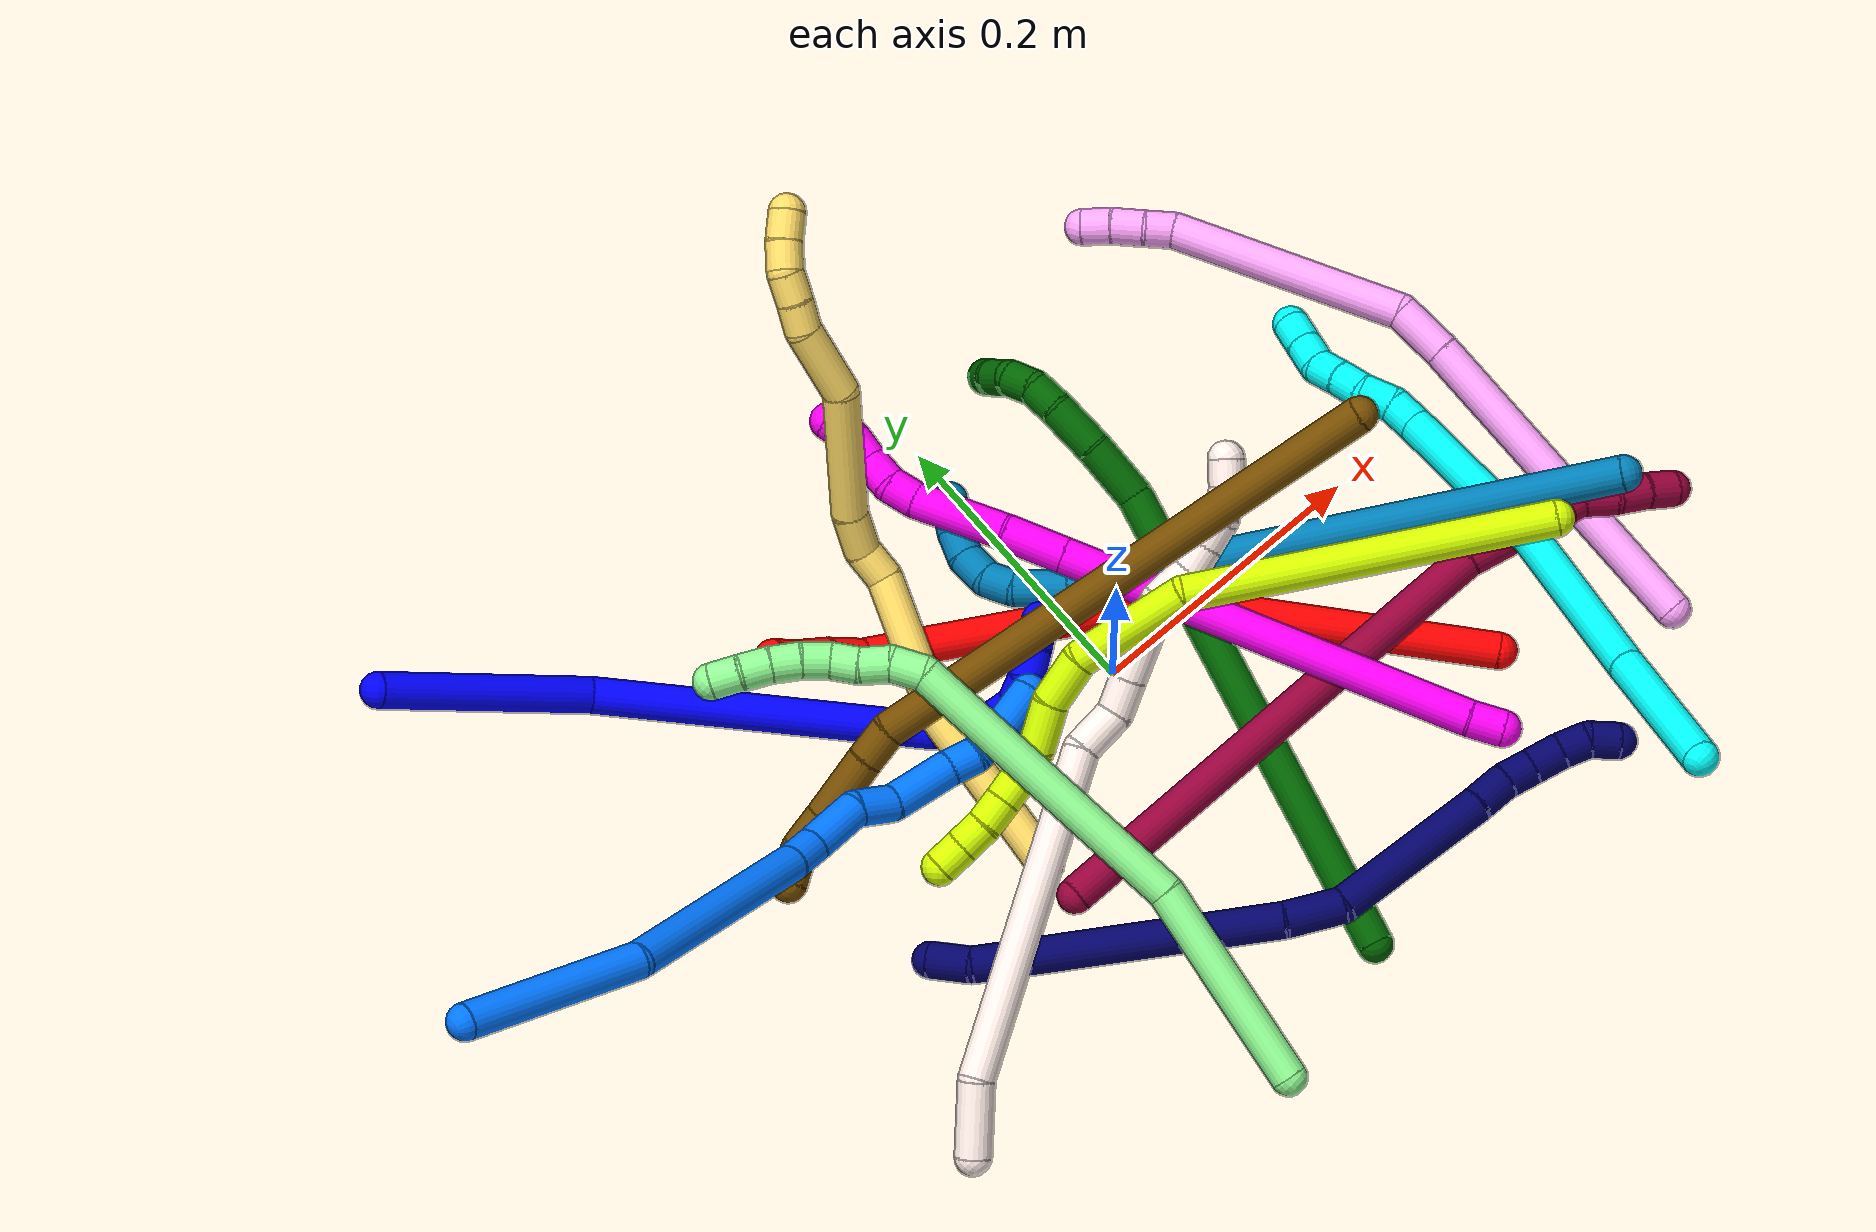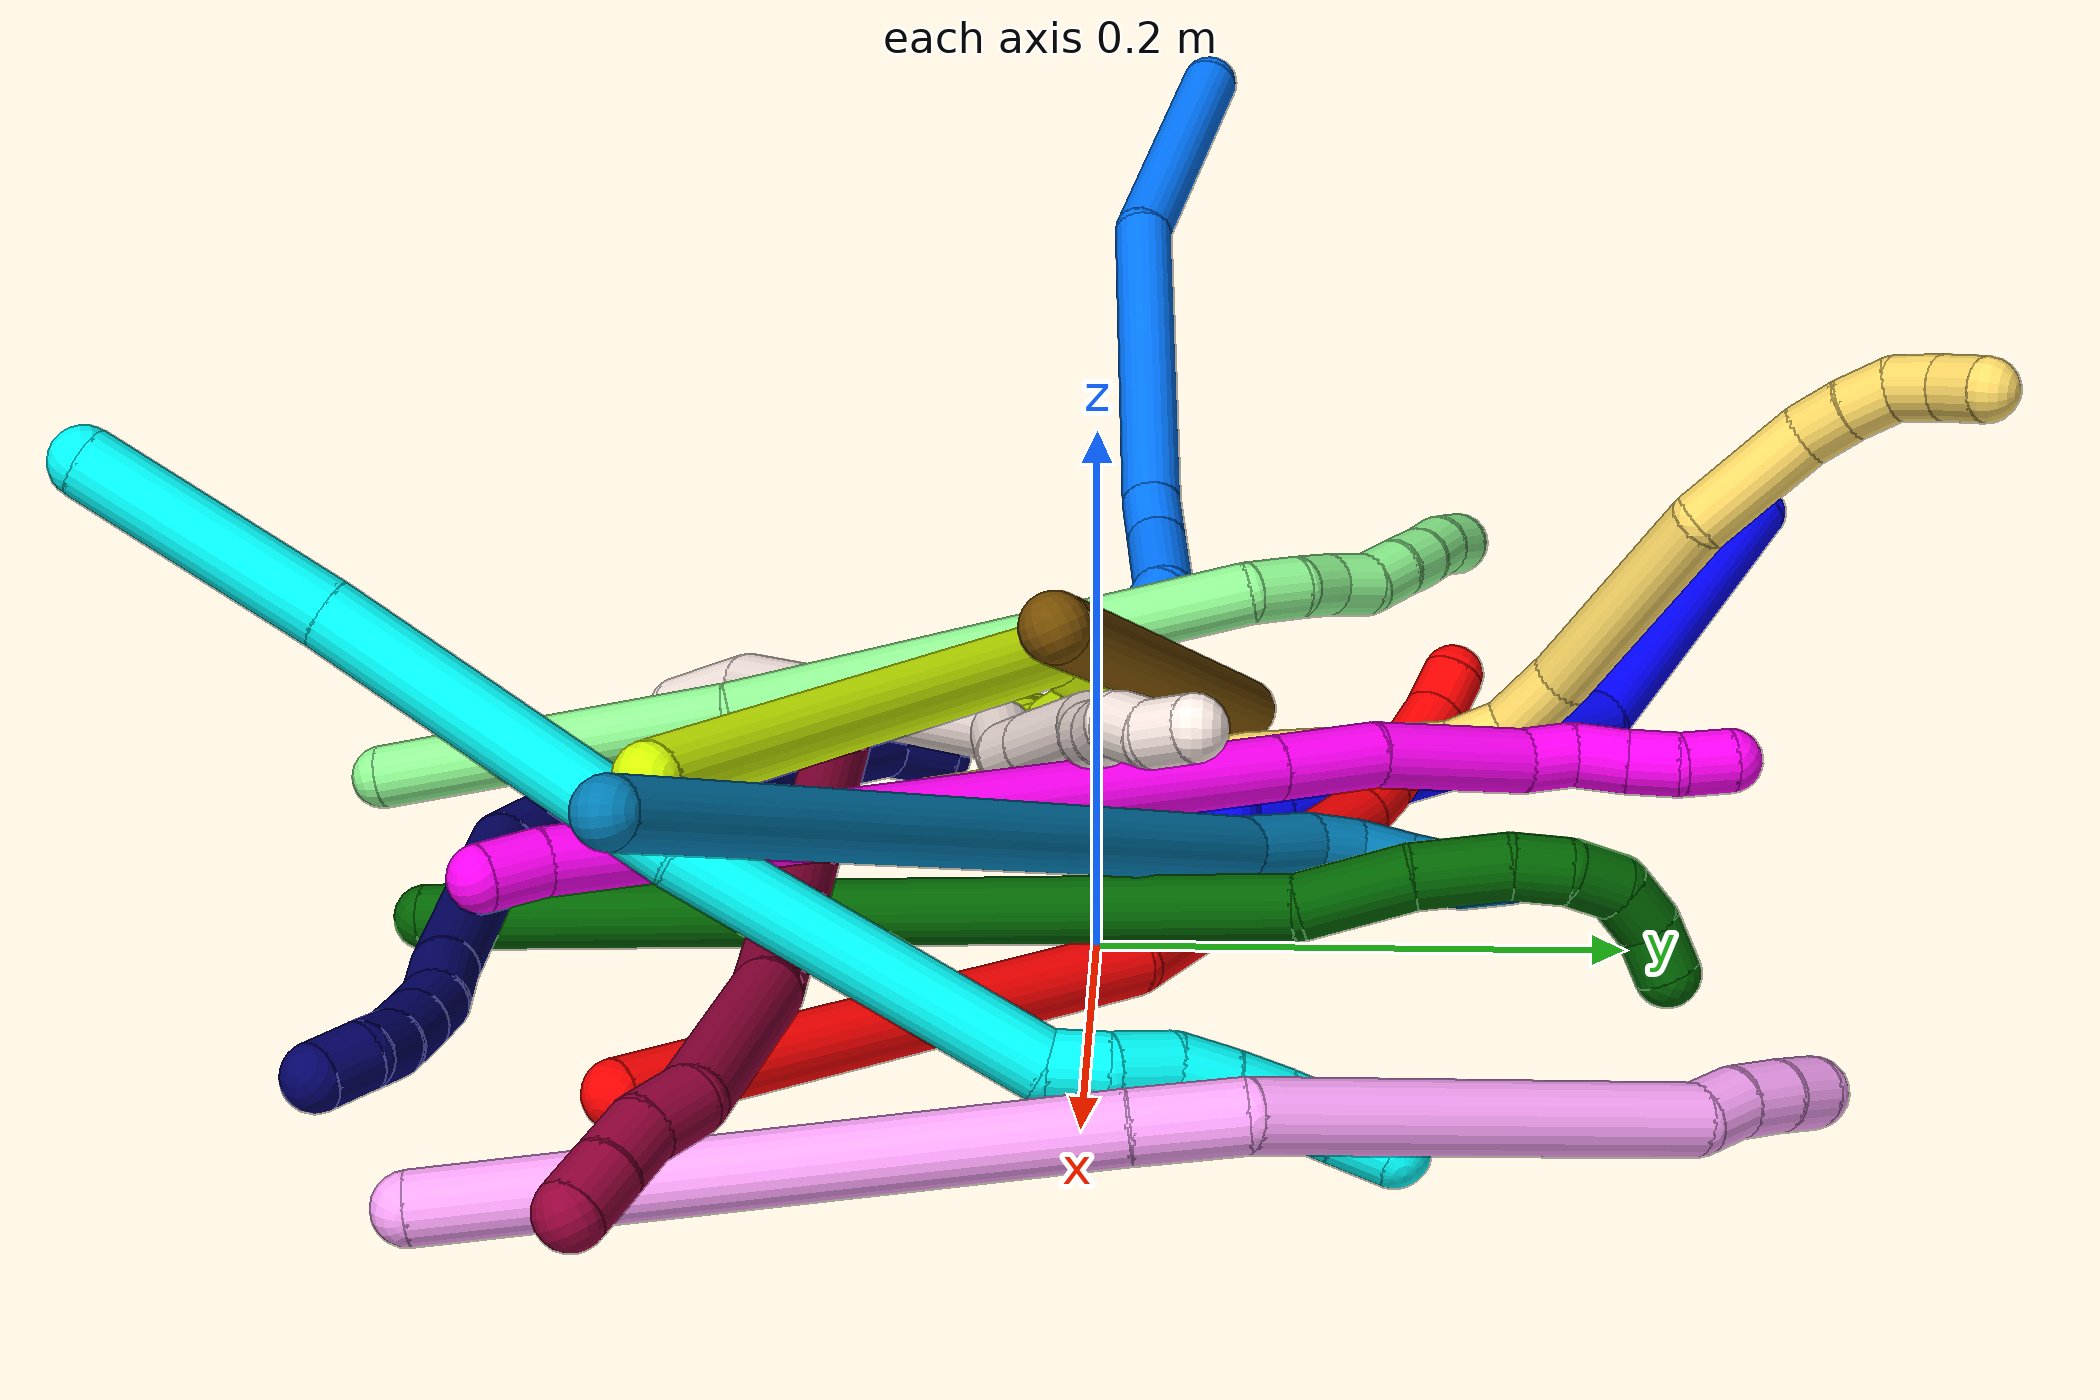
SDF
<sdf version="1.7">
 <world name="default">
  <plugin name="TubeGeneratorPlugin" filename="libtube_generator_plugin.so"/>
  <model name="photoneo_s_sensor">
   <static>1</static>
   <pose>0 0 2 1.57079 1.57079 3.14159</pose>
   <link name="link">
    <inertial><mass>0.1</mass></inertial>
    <sensor name="sensor" type="depth">
     <update_rate>30</update_rate>
     <camera>
      <horizontal_fov>1.22</horizontal_fov>
      <image><width>1920</width><height>1200</height><format>B8G8R8</format></image>
      <clip><near>0.1</near><far>4</far></clip>
      <depth_camera><output>points</output></depth_camera>
     </camera>
     <plugin name="camera_plugin" filename="libgazebo_ros_depth_camera.so">
      <baseline>0.2</baseline>
      <alwaysOn>1</alwaysOn>
      <updateRate>0.0</updateRate>
      <cameraName>camera_ir</cameraName>
      <imageTopicName>/camera/color/image_raw</imageTopicName>
      <cameraInfoTopicName>/camera/color/camera_info</cameraInfoTopicName>
      <depthImageTopicName>/camera/depth/image_raw</depthImageTopicName>
      <depthImageCameraInfoTopicName>/camera/depth/camera_info</depthImageCameraInfoTopicName>
      <pointCloudTopicName>/camera/depth/points</pointCloudTopicName>
      <frameName>fr_optical</frameName>
      <pointCloudCutoff>0.1</pointCloudCutoff>
      <pointCloudCutoffMax>2.0</pointCloudCutoffMax>
      <distortionK1>0</distortionK1>
      <distortionK2>0</distortionK2>
      <distortionK3>0</distortionK3>
      <distortionT1>0</distortionT1>
      <distortionT2>0</distortionT2>
      <CxPrime>0</CxPrime>
      <Cx>0</Cx>
      <Cy>0</Cy>
      <focalLength>0</focalLength>
      <hackBaseline>0</hackBaseline>
     </plugin>
    </sensor>
   </link>
  </model>
  <gravity>0 0 -9.8</gravity>
  <magnetic_field>6e-06 2.3e-05 -4.2e-05</magnetic_field>
  <atmosphere type="adiabatic"/>
  <physics name="default_physics" default="0" type="ode">
   <max_step_size>0.003</max_step_size>
   <real_time_factor>1</real_time_factor>
   <real_time_update_rate>1000</real_time_update_rate>
   <max_contacts>10000</max_contacts>
   <ode>
    <solver>
     <type>quick</type>
     <iters>100</iters>
     <sor>1.3</sor>
     <use_dynamic_moi_rescaling>0</use_dynamic_moi_rescaling>
    </solver>
    <constraints>
     <contact_max_correcting_vel>0</contact_max_correcting_vel>
     <contact_surface_layer>0.001</contact_surface_layer>
     <cfm>0</cfm>
     <erp>0.2</erp>
    </constraints>
   </ode>
  </physics>
  <scene><ambient>0.4 0.4 0.4 1</ambient><background>0.7 0.7 0.7 1</background><shadows>0</shadows></scene>
  <audio><device>default</device></audio>
  <spherical_coordinates>
   <surface_model>EARTH_WGS84</surface_model>
   <latitude_deg>0</latitude_deg>
   <longitude_deg>0</longitude_deg>
   <elevation>0</elevation>
   <heading_deg>0</heading_deg>
  </spherical_coordinates>
  <model name="bin">
   <static>1</static>
   <link name="bottom">
    <collision name="collision-bottom">
     <pose>0 0 -0.01 0 -0 0</pose>
     <geometry><box><size>0.8 0.6 0.02</size></box></geometry>
     <surface>
      <friction><ode><mu>100</mu><mu2>100</mu2></ode></friction>
      <contact><collide_bitmask>65535</collide_bitmask></contact>
     </surface>
    </collision>
   </link>
   <link name="west_wall">
    <collision name="collision-west_wall">
     <pose>-0.41 0 0.1 0 -0 0</pose>
     <geometry><box><size>0.02 0.6 0.2</size></box></geometry>
     <surface>
      <friction><ode><mu>100</mu><mu2>100</mu2></ode></friction>
      <contact><collide_bitmask>65535</collide_bitmask></contact>
     </surface>
    </collision>
   </link>
   <link name="east_wall">
    <collision name="collision-east_wall">
     <pose>0.41 0 0.1 0 -0 0</pose>
     <geometry><box><size>0.02 0.6 0.2</size></box></geometry>
     <surface>
      <friction><ode><mu>100</mu><mu2>100</mu2></ode></friction>
      <contact><collide_bitmask>65535</collide_bitmask></contact>
     </surface>
    </collision>
   </link>
   <link name="south_wall">
    <collision name="collision-south_wall">
     <pose>0 -0.31 0.1 0 -0 0</pose>
     <geometry><box><size>0.8 0.02 0.2</size></box></geometry>
     <surface>
      <friction><ode><mu>100</mu><mu2>100</mu2></ode></friction>
      <contact><collide_bitmask>65535</collide_bitmask></contact>
     </surface>
    </collision>
   </link>
   <link name="north_wall">
    <collision name="collision-north_wall">
     <pose>0 0.31 0.1 0 -0 0</pose>
     <geometry><box><size>0.8 0.02 0.2</size></box></geometry>
     <surface>
      <friction><ode><mu>100</mu><mu2>100</mu2></ode></friction>
      <contact><collide_bitmask>65535</collide_bitmask></contact>
     </surface>
    </collision>
   </link>
  </model>
  <model name="1">
   <static>0</static>
   <link name="1">
    <collision name="collision-cylinder-e_1_1_4">
     <pose>0.036945 0.030817 -0.058041 -2.65349 0.512157 -1.62095</pose>
     <geometry><cylinder><radius>0.0125</radius><length>0.150776</length></cylinder></geometry>
     <surface>
      <friction><ode><mu>1.16</mu><mu2>1.16</mu2><slip1>0</slip1><slip2>0</slip2></ode></friction>
      <contact><ode><kp>1e+06</kp><kd>1</kd><max_vel>0</max_vel><min_depth>0.001</min_depth></ode></contact>
     </surface>
    </collision>
    <visual name="visual-cylinder-e_1_1_4">
     <pose>0.036945 0.030817 -0.058041 -2.65349 0.512157 -1.62095</pose>
     <geometry><cylinder><radius>0.0125</radius><length>0.150776</length></cylinder></geometry>
     <material><ambient>0 0 1 1</ambient></material>
    </visual>
    <collision name="collision-cylinder-e_2_4_5">
     <pose>0.087077 0.078405 -0.212437 -2.96927 0.134032 -1.32116</pose>
     <geometry><cylinder><radius>0.0125</radius><length>0.197377</length></cylinder></geometry>
     <surface>
      <friction><ode><mu>1.16</mu><mu2>1.16</mu2><slip1>0</slip1><slip2>0</slip2></ode></friction>
      <contact><ode><kp>1e+06</kp><kd>1</kd><max_vel>0</max_vel><min_depth>0.001</min_depth></ode></contact>
     </surface>
    </collision>
    <visual name="visual-cylinder-e_2_4_5">
     <pose>0.087077 0.078405 -0.212437 -2.96927 0.134032 -1.32116</pose>
     <geometry><cylinder><radius>0.0125</radius><length>0.197377</length></cylinder></geometry>
     <material><ambient>0 0 1 1</ambient></material>
    </visual>
    <collision name="collision-cylinder-e_3_5_6">
     <pose>0.102583 0.098065 -0.324571 -2.96046 0.143498 -1.33896</pose>
     <geometry><cylinder><radius>0.0125</radius><length>0.032416</length></cylinder></geometry>
     <surface>
      <friction><ode><mu>1.16</mu><mu2>1.16</mu2><slip1>0</slip1><slip2>0</slip2></ode></friction>
      <contact><ode><kp>1e+06</kp><kd>1</kd><max_vel>0</max_vel><min_depth>0.001</min_depth></ode></contact>
     </surface>
    </collision>
    <visual name="visual-cylinder-e_3_5_6">
     <pose>0.102583 0.098065 -0.324571 -2.96046 0.143498 -1.33896</pose>
     <geometry><cylinder><radius>0.0125</radius><length>0.032416</length></cylinder></geometry>
     <material><ambient>0 0 1 1</ambient></material>
    </visual>
    <collision name="collision-cylinder-e_4_6_7">
     <pose>0.108466 0.097749 -0.359197 2.97314 0.18439 1.66155</pose>
     <geometry><cylinder><radius>0.0125</radius><length>0.038895</length></cylinder></geometry>
     <surface>
      <friction><ode><mu>1.16</mu><mu2>1.16</mu2><slip1>0</slip1><slip2>0</slip2></ode></friction>
      <contact><ode><kp>1e+06</kp><kd>1</kd><max_vel>0</max_vel><min_depth>0.001</min_depth></ode></contact>
     </surface>
    </collision>
    <visual name="visual-cylinder-e_4_6_7">
     <pose>0.108466 0.097749 -0.359197 2.97314 0.18439 1.66155</pose>
     <geometry><cylinder><radius>0.0125</radius><length>0.038895</length></cylinder></geometry>
     <material><ambient>0 0 1 1</ambient></material>
    </visual>
    <collision name="collision-cylinder-e_5_7_8">
     <pose>0.115355 0.089193 -0.38603 2.55117 0.332854 1.00936</pose>
     <geometry><cylinder><radius>0.0125</radius><length>0.020341</length></cylinder></geometry>
     <surface>
      <friction><ode><mu>1.16</mu><mu2>1.16</mu2><slip1>0</slip1><slip2>0</slip2></ode></friction>
      <contact><ode><kp>1e+06</kp><kd>1</kd><max_vel>0</max_vel><min_depth>0.001</min_depth></ode></contact>
     </surface>
    </collision>
    <visual name="visual-cylinder-e_5_7_8">
     <pose>0.115355 0.089193 -0.38603 2.55117 0.332854 1.00936</pose>
     <geometry><cylinder><radius>0.0125</radius><length>0.020341</length></cylinder></geometry>
     <material><ambient>0 0 1 1</ambient></material>
    </visual>
    <collision name="collision-cylinder-e_6_8_9">
     <pose>0.122455 0.075413 -0.397883 2.00104 0.386718 0.592622</pose>
     <geometry><cylinder><radius>0.0125</radius><length>0.020026</length></cylinder></geometry>
     <surface>
      <friction><ode><mu>1.16</mu><mu2>1.16</mu2><slip1>0</slip1><slip2>0</slip2></ode></friction>
      <contact><ode><kp>1e+06</kp><kd>1</kd><max_vel>0</max_vel><min_depth>0.001</min_depth></ode></contact>
     </surface>
    </collision>
    <visual name="visual-cylinder-e_6_8_9">
     <pose>0.122455 0.075413 -0.397883 2.00104 0.386718 0.592622</pose>
     <geometry><cylinder><radius>0.0125</radius><length>0.020026</length></cylinder></geometry>
     <material><ambient>0 0 1 1</ambient></material>
    </visual>
    <collision name="collision-cylinder-e_7_9_10">
     <pose>0.133979 0.060762 -0.403256 1.80819 0.880172 1.0785</pose>
     <geometry><cylinder><radius>0.0125</radius><length>0.020101</length></cylinder></geometry>
     <surface>
      <friction><ode><mu>1.16</mu><mu2>1.16</mu2><slip1>0</slip1><slip2>0</slip2></ode></friction>
      <contact><ode><kp>1e+06</kp><kd>1</kd><max_vel>0</max_vel><min_depth>0.001</min_depth></ode></contact>
     </surface>
    </collision>
    <visual name="visual-cylinder-e_7_9_10">
     <pose>0.133979 0.060762 -0.403256 1.80819 0.880172 1.0785</pose>
     <geometry><cylinder><radius>0.0125</radius><length>0.020101</length></cylinder></geometry>
     <material><ambient>0 0 1 1</ambient></material>
    </visual>
    <collision name="collision-cylinder-e_8_10_2">
     <pose>0.149937 0.048856 -0.405739 1.74105 0.958523 1.10513</pose>
     <geometry><cylinder><radius>0.0125</radius><length>0.020067</length></cylinder></geometry>
     <surface>
      <friction><ode><mu>1.16</mu><mu2>1.16</mu2><slip1>0</slip1><slip2>0</slip2></ode></friction>
      <contact><ode><kp>1e+06</kp><kd>1</kd><max_vel>0</max_vel><min_depth>0.001</min_depth></ode></contact>
     </surface>
    </collision>
    <visual name="visual-cylinder-e_8_10_2">
     <pose>0.149937 0.048856 -0.405739 1.74105 0.958523 1.10513</pose>
     <geometry><cylinder><radius>0.0125</radius><length>0.020067</length></cylinder></geometry>
     <material><ambient>0 0 1 1</ambient></material>
    </visual>
    <collision name="collision-sphere-2">
     <pose>0.158148 0.043173 -0.406716 0 -0 0</pose>
     <geometry><sphere><radius>0.0125</radius></sphere></geometry>
     <surface>
      <friction><ode><mu>1.16</mu><mu2>1.16</mu2><slip1>0</slip1><slip2>0</slip2></ode></friction>
      <contact><ode><kp>1e+06</kp><kd>1</kd><max_vel>0</max_vel><min_depth>0.001</min_depth></ode></contact>
     </surface>
    </collision>
    <visual name="visual-sphere-2">
     <pose>0.158148 0.043173 -0.406716 0 -0 0</pose>
     <geometry><sphere><radius>0.0125</radius></sphere></geometry>
     <material><ambient>0 0 1 1</ambient></material>
    </visual>
    <collision name="collision-sphere-10">
     <pose>0.141726 0.054539 -0.404762 0 -0 0</pose>
     <geometry><sphere><radius>0.0125</radius></sphere></geometry>
     <surface>
      <friction><ode><mu>1.16</mu><mu2>1.16</mu2><slip1>0</slip1><slip2>0</slip2></ode></friction>
      <contact><ode><kp>1e+06</kp><kd>1</kd><max_vel>0</max_vel><min_depth>0.001</min_depth></ode></contact>
     </surface>
    </collision>
    <visual name="visual-sphere-10">
     <pose>0.141726 0.054539 -0.404762 0 -0 0</pose>
     <geometry><sphere><radius>0.0125</radius></sphere></geometry>
     <material><ambient>0 0 1 1</ambient></material>
    </visual>
    <collision name="collision-sphere-9">
     <pose>0.126231 0.066985 -0.40175 0 -0 0</pose>
     <geometry><sphere><radius>0.0125</radius></sphere></geometry>
     <surface>
      <friction><ode><mu>1.16</mu><mu2>1.16</mu2><slip1>0</slip1><slip2>0</slip2></ode></friction>
      <contact><ode><kp>1e+06</kp><kd>1</kd><max_vel>0</max_vel><min_depth>0.001</min_depth></ode></contact>
     </surface>
    </collision>
    <visual name="visual-sphere-9">
     <pose>0.126231 0.066985 -0.40175 0 -0 0</pose>
     <geometry><sphere><radius>0.0125</radius></sphere></geometry>
     <material><ambient>0 0 1 1</ambient></material>
    </visual>
    <collision name="collision-sphere-4">
     <pose>0.073889 0.061634 -0.116082 0 -0 0</pose>
     <geometry><sphere><radius>0.0125</radius></sphere></geometry>
     <surface>
      <friction><ode><mu>1.16</mu><mu2>1.16</mu2><slip1>0</slip1><slip2>0</slip2></ode></friction>
      <contact><ode><kp>1e+06</kp><kd>1</kd><max_vel>0</max_vel><min_depth>0.001</min_depth></ode></contact>
     </surface>
    </collision>
    <visual name="visual-sphere-4">
     <pose>0.073889 0.061634 -0.116082 0 -0 0</pose>
     <geometry><sphere><radius>0.0125</radius></sphere></geometry>
     <material><ambient>0 0 1 1</ambient></material>
    </visual>
    <collision name="collision-sphere-1">
     <geometry><sphere><radius>0.0125</radius></sphere></geometry>
     <surface>
      <friction><ode><mu>1.16</mu><mu2>1.16</mu2><slip1>0</slip1><slip2>0</slip2></ode></friction>
      <contact><ode><kp>1e+06</kp><kd>1</kd><max_vel>0</max_vel><min_depth>0.001</min_depth></ode></contact>
     </surface>
    </collision>
    <visual name="visual-sphere-1">
     <geometry><sphere><radius>0.0125</radius></sphere></geometry>
     <material><ambient>0 0 1 1</ambient></material>
    </visual>
    <collision name="collision-sphere-8">
     <pose>0.118678 0.083842 -0.394015 0 -0 0</pose>
     <geometry><sphere><radius>0.0125</radius></sphere></geometry>
     <surface>
      <friction><ode><mu>1.16</mu><mu2>1.16</mu2><slip1>0</slip1><slip2>0</slip2></ode></friction>
      <contact><ode><kp>1e+06</kp><kd>1</kd><max_vel>0</max_vel><min_depth>0.001</min_depth></ode></contact>
     </surface>
    </collision>
    <visual name="visual-sphere-8">
     <pose>0.118678 0.083842 -0.394015 0 -0 0</pose>
     <geometry><sphere><radius>0.0125</radius></sphere></geometry>
     <material><ambient>0 0 1 1</ambient></material>
    </visual>
    <collision name="collision-sphere-5">
     <pose>0.100265 0.095175 -0.308792 0 -0 0</pose>
     <geometry><sphere><radius>0.0125</radius></sphere></geometry>
     <surface>
      <friction><ode><mu>1.16</mu><mu2>1.16</mu2><slip1>0</slip1><slip2>0</slip2></ode></friction>
      <contact><ode><kp>1e+06</kp><kd>1</kd><max_vel>0</max_vel><min_depth>0.001</min_depth></ode></contact>
     </surface>
    </collision>
    <visual name="visual-sphere-5">
     <pose>0.100265 0.095175 -0.308792 0 -0 0</pose>
     <geometry><sphere><radius>0.0125</radius></sphere></geometry>
     <material><ambient>0 0 1 1</ambient></material>
    </visual>
    <collision name="collision-sphere-6">
     <pose>0.104901 0.100955 -0.34035 0 -0 0</pose>
     <geometry><sphere><radius>0.0125</radius></sphere></geometry>
     <surface>
      <friction><ode><mu>1.16</mu><mu2>1.16</mu2><slip1>0</slip1><slip2>0</slip2></ode></friction>
      <contact><ode><kp>1e+06</kp><kd>1</kd><max_vel>0</max_vel><min_depth>0.001</min_depth></ode></contact>
     </surface>
    </collision>
    <visual name="visual-sphere-6">
     <pose>0.104901 0.100955 -0.34035 0 -0 0</pose>
     <geometry><sphere><radius>0.0125</radius></sphere></geometry>
     <material><ambient>0 0 1 1</ambient></material>
    </visual>
    <collision name="collision-sphere-7">
     <pose>0.112032 0.094544 -0.378044 0 -0 0</pose>
     <geometry><sphere><radius>0.0125</radius></sphere></geometry>
     <surface>
      <friction><ode><mu>1.16</mu><mu2>1.16</mu2><slip1>0</slip1><slip2>0</slip2></ode></friction>
      <contact><ode><kp>1e+06</kp><kd>1</kd><max_vel>0</max_vel><min_depth>0.001</min_depth></ode></contact>
     </surface>
    </collision>
    <visual name="visual-sphere-7">
     <pose>0.112032 0.094544 -0.378044 0 -0 0</pose>
     <geometry><sphere><radius>0.0125</radius></sphere></geometry>
     <material><ambient>0 0 1 1</ambient></material>
    </visual>
    <inertial>
     <pose>0.081604 0.065258 -0.214484 0 -0 0</pose>
     <mass>0.5</mass>
     <inertia>
      <ixx>-0.000709</ixx>
      <ixy>0</ixy>
      <ixz>0</ixz>
      <iyy>-0.00093</iyy>
      <iyz>0</iyz>
      <izz>-0.000492</izz>
     </inertia>
    </inertial>
   </link>
   <pose>-0.387913 0.28822 0.08133 -1.80012 0.514199 0.6126</pose>
  </model>
  <model name="2">
   <static>0</static>
   <link name="2">
    <collision name="collision-cylinder-e_1_1_4">
     <pose>-0.035352 0.055876 0.092912 -0.541437 -0.315201 0.088153</pose>
     <geometry><cylinder><radius>0.0125</radius><length>0.228075</length></cylinder></geometry>
     <surface>
      <friction><ode><mu>1.16</mu><mu2>1.16</mu2><slip1>0</slip1><slip2>0</slip2></ode></friction>
      <contact><ode><kp>1e+06</kp><kd>1</kd><max_vel>0</max_vel><min_depth>0.001</min_depth></ode></contact>
     </surface>
    </collision>
    <visual name="visual-cylinder-e_1_1_4">
     <pose>-0.035352 0.055876 0.092912 -0.541437 -0.315201 0.088153</pose>
     <geometry><cylinder><radius>0.0125</radius><length>0.228075</length></cylinder></geometry>
     <material><ambient>1 0 0 1</ambient></material>
    </visual>
    <collision name="collision-cylinder-e_2_4_5">
     <pose>-0.102377 0.12525 0.269541 -0.15986 -0.357457 0.028939</pose>
     <geometry><cylinder><radius>0.0125</radius><length>0.18104</length></cylinder></geometry>
     <surface>
      <friction><ode><mu>1.16</mu><mu2>1.16</mu2><slip1>0</slip1><slip2>0</slip2></ode></friction>
      <contact><ode><kp>1e+06</kp><kd>1</kd><max_vel>0</max_vel><min_depth>0.001</min_depth></ode></contact>
     </surface>
    </collision>
    <visual name="visual-cylinder-e_2_4_5">
     <pose>-0.102377 0.12525 0.269541 -0.15986 -0.357457 0.028939</pose>
     <geometry><cylinder><radius>0.0125</radius><length>0.18104</length></cylinder></geometry>
     <material><ambient>1 0 0 1</ambient></material>
    </visual>
    <collision name="collision-cylinder-e_3_5_6">
     <pose>-0.136437 0.139541 0.363942 -0.074064 -0.219268 0.008156</pose>
     <geometry><cylinder><radius>0.0125</radius><length>0.021952</length></cylinder></geometry>
     <surface>
      <friction><ode><mu>1.16</mu><mu2>1.16</mu2><slip1>0</slip1><slip2>0</slip2></ode></friction>
      <contact><ode><kp>1e+06</kp><kd>1</kd><max_vel>0</max_vel><min_depth>0.001</min_depth></ode></contact>
     </surface>
    </collision>
    <visual name="visual-cylinder-e_3_5_6">
     <pose>-0.136437 0.139541 0.363942 -0.074064 -0.219268 0.008156</pose>
     <geometry><cylinder><radius>0.0125</radius><length>0.021952</length></cylinder></geometry>
     <material><ambient>1 0 0 1</ambient></material>
    </visual>
    <collision name="collision-cylinder-e_4_6_7">
     <pose>-0.137622 0.142164 0.387508 -0.141119 0.09213 -0.006516</pose>
     <geometry><cylinder><radius>0.0125</radius><length>0.026134</length></cylinder></geometry>
     <surface>
      <friction><ode><mu>1.16</mu><mu2>1.16</mu2><slip1>0</slip1><slip2>0</slip2></ode></friction>
      <contact><ode><kp>1e+06</kp><kd>1</kd><max_vel>0</max_vel><min_depth>0.001</min_depth></ode></contact>
     </surface>
    </collision>
    <visual name="visual-cylinder-e_4_6_7">
     <pose>-0.137622 0.142164 0.387508 -0.141119 0.09213 -0.006516</pose>
     <geometry><cylinder><radius>0.0125</radius><length>0.026134</length></cylinder></geometry>
     <material><ambient>1 0 0 1</ambient></material>
    </visual>
    <collision name="collision-cylinder-e_5_7_8">
     <pose>-0.13646 0.144799 0.41167 -0.07125 -0.00356 0.000127</pose>
     <geometry><cylinder><radius>0.0125</radius><length>0.022616</length></cylinder></geometry>
     <surface>
      <friction><ode><mu>1.16</mu><mu2>1.16</mu2><slip1>0</slip1><slip2>0</slip2></ode></friction>
      <contact><ode><kp>1e+06</kp><kd>1</kd><max_vel>0</max_vel><min_depth>0.001</min_depth></ode></contact>
     </surface>
    </collision>
    <visual name="visual-cylinder-e_5_7_8">
     <pose>-0.13646 0.144799 0.41167 -0.07125 -0.00356 0.000127</pose>
     <geometry><cylinder><radius>0.0125</radius><length>0.022616</length></cylinder></geometry>
     <material><ambient>1 0 0 1</ambient></material>
    </visual>
    <collision name="collision-cylinder-e_6_8_2">
     <pose>-0.134067 0.146078 0.432731 -0.048444 0.243562 -0.00593</pose>
     <geometry><cylinder><radius>0.0125</radius><length>0.020182</length></cylinder></geometry>
     <surface>
      <friction><ode><mu>1.16</mu><mu2>1.16</mu2><slip1>0</slip1><slip2>0</slip2></ode></friction>
      <contact><ode><kp>1e+06</kp><kd>1</kd><max_vel>0</max_vel><min_depth>0.001</min_depth></ode></contact>
     </surface>
    </collision>
    <visual name="visual-cylinder-e_6_8_2">
     <pose>-0.134067 0.146078 0.432731 -0.048444 0.243562 -0.00593</pose>
     <geometry><cylinder><radius>0.0125</radius><length>0.020182</length></cylinder></geometry>
     <material><ambient>1 0 0 1</ambient></material>
    </visual>
    <collision name="collision-sphere-2">
     <pose>-0.131633 0.146552 0.442513 0 -0 0</pose>
     <geometry><sphere><radius>0.0125</radius></sphere></geometry>
     <surface>
      <friction><ode><mu>1.16</mu><mu2>1.16</mu2><slip1>0</slip1><slip2>0</slip2></ode></friction>
      <contact><ode><kp>1e+06</kp><kd>1</kd><max_vel>0</max_vel><min_depth>0.001</min_depth></ode></contact>
     </surface>
    </collision>
    <visual name="visual-sphere-2">
     <pose>-0.131633 0.146552 0.442513 0 -0 0</pose>
     <geometry><sphere><radius>0.0125</radius></sphere></geometry>
     <material><ambient>1 0 0 1</ambient></material>
    </visual>
    <collision name="collision-sphere-4">
     <pose>-0.070705 0.111752 0.185824 0 -0 0</pose>
     <geometry><sphere><radius>0.0125</radius></sphere></geometry>
     <surface>
      <friction><ode><mu>1.16</mu><mu2>1.16</mu2><slip1>0</slip1><slip2>0</slip2></ode></friction>
      <contact><ode><kp>1e+06</kp><kd>1</kd><max_vel>0</max_vel><min_depth>0.001</min_depth></ode></contact>
     </surface>
    </collision>
    <visual name="visual-sphere-4">
     <pose>-0.070705 0.111752 0.185824 0 -0 0</pose>
     <geometry><sphere><radius>0.0125</radius></sphere></geometry>
     <material><ambient>1 0 0 1</ambient></material>
    </visual>
    <collision name="collision-sphere-1">
     <geometry><sphere><radius>0.0125</radius></sphere></geometry>
     <surface>
      <friction><ode><mu>1.16</mu><mu2>1.16</mu2><slip1>0</slip1><slip2>0</slip2></ode></friction>
      <contact><ode><kp>1e+06</kp><kd>1</kd><max_vel>0</max_vel><min_depth>0.001</min_depth></ode></contact>
     </surface>
    </collision>
    <visual name="visual-sphere-1">
     <geometry><sphere><radius>0.0125</radius></sphere></geometry>
     <material><ambient>1 0 0 1</ambient></material>
    </visual>
    <collision name="collision-sphere-8">
     <pose>-0.136501 0.145604 0.422949 0 -0 0</pose>
     <geometry><sphere><radius>0.0125</radius></sphere></geometry>
     <surface>
      <friction><ode><mu>1.16</mu><mu2>1.16</mu2><slip1>0</slip1><slip2>0</slip2></ode></friction>
      <contact><ode><kp>1e+06</kp><kd>1</kd><max_vel>0</max_vel><min_depth>0.001</min_depth></ode></contact>
     </surface>
    </collision>
    <visual name="visual-sphere-8">
     <pose>-0.136501 0.145604 0.422949 0 -0 0</pose>
     <geometry><sphere><radius>0.0125</radius></sphere></geometry>
     <material><ambient>1 0 0 1</ambient></material>
    </visual>
    <collision name="collision-sphere-5">
     <pose>-0.134049 0.138748 0.353258 0 -0 0</pose>
     <geometry><sphere><radius>0.0125</radius></sphere></geometry>
     <surface>
      <friction><ode><mu>1.16</mu><mu2>1.16</mu2><slip1>0</slip1><slip2>0</slip2></ode></friction>
      <contact><ode><kp>1e+06</kp><kd>1</kd><max_vel>0</max_vel><min_depth>0.001</min_depth></ode></contact>
     </surface>
    </collision>
    <visual name="visual-sphere-5">
     <pose>-0.134049 0.138748 0.353258 0 -0 0</pose>
     <geometry><sphere><radius>0.0125</radius></sphere></geometry>
     <material><ambient>1 0 0 1</ambient></material>
    </visual>
    <collision name="collision-sphere-6">
     <pose>-0.138824 0.140333 0.374626 0 -0 0</pose>
     <geometry><sphere><radius>0.0125</radius></sphere></geometry>
     <surface>
      <friction><ode><mu>1.16</mu><mu2>1.16</mu2><slip1>0</slip1><slip2>0</slip2></ode></friction>
      <contact><ode><kp>1e+06</kp><kd>1</kd><max_vel>0</max_vel><min_depth>0.001</min_depth></ode></contact>
     </surface>
    </collision>
    <visual name="visual-sphere-6">
     <pose>-0.138824 0.140333 0.374626 0 -0 0</pose>
     <geometry><sphere><radius>0.0125</radius></sphere></geometry>
     <material><ambient>1 0 0 1</ambient></material>
    </visual>
    <collision name="collision-sphere-7">
     <pose>-0.13642 0.143994 0.40039 0 -0 0</pose>
     <geometry><sphere><radius>0.0125</radius></sphere></geometry>
     <surface>
      <friction><ode><mu>1.16</mu><mu2>1.16</mu2><slip1>0</slip1><slip2>0</slip2></ode></friction>
      <contact><ode><kp>1e+06</kp><kd>1</kd><max_vel>0</max_vel><min_depth>0.001</min_depth></ode></contact>
     </surface>
    </collision>
    <visual name="visual-sphere-7">
     <pose>-0.13642 0.143994 0.40039 0 -0 0</pose>
     <geometry><sphere><radius>0.0125</radius></sphere></geometry>
     <material><ambient>1 0 0 1</ambient></material>
    </visual>
    <inertial>
     <pose>-0.077962 0.096841 0.212298 0 -0 0</pose>
     <mass>0.5</mass>
     <inertia>
      <ixx>0.001509</ixx>
      <ixy>0</ixy>
      <ixz>0</ixz>
      <iyy>0.001477</iyy>
      <iyz>0</iyz>
      <izz>-4.5e-05</izz>
     </inertia>
    </inertial>
   </link>
   <pose>0.203122 -0.157958 0.012211 -0.340158 -1.10175 -0.036153</pose>
  </model>
  <model name="3">
   <static>0</static>
   <link name="3">
    <collision name="collision-cylinder-e_1_1_4">
     <pose>0.027482 0.028519 0.027199 -0.809089 0.608937 -0.267483</pose>
     <geometry><cylinder><radius>0.0125</radius><length>0.096091</length></cylinder></geometry>
     <surface>
      <friction><ode><mu>1.16</mu><mu2>1.16</mu2><slip1>0</slip1><slip2>0</slip2></ode></friction>
      <contact><ode><kp>1e+06</kp><kd>1</kd><max_vel>0</max_vel><min_depth>0.001</min_depth></ode></contact>
     </surface>
    </collision>
    <visual name="visual-cylinder-e_1_1_4">
     <pose>0.027482 0.028519 0.027199 -0.809089 0.608937 -0.267483</pose>
     <geometry><cylinder><radius>0.0125</radius><length>0.096091</length></cylinder></geometry>
     <material><ambient>0.003922 1 0.996078 1</ambient></material>
    </visual>
    <collision name="collision-cylinder-e_2_4_5">
     <pose>0.095418 0.096668 0.096102 -0.7599 0.612857 -0.251375</pose>
     <geometry><cylinder><radius>0.0125</radius><length>0.140659</length></cylinder></geometry>
     <surface>
      <friction><ode><mu>1.16</mu><mu2>1.16</mu2><slip1>0</slip1><slip2>0</slip2></ode></friction>
      <contact><ode><kp>1e+06</kp><kd>1</kd><max_vel>0</max_vel><min_depth>0.001</min_depth></ode></contact>
     </surface>
    </collision>
    <visual name="visual-cylinder-e_2_4_5">
     <pose>0.095418 0.096668 0.096102 -0.7599 0.612857 -0.251375</pose>
     <geometry><cylinder><radius>0.0125</radius><length>0.140659</length></cylinder></geometry>
     <material><ambient>0.003922 1 0.996078 1</ambient></material>
    </visual>
    <collision name="collision-cylinder-e_3_5_6">
     <pose>0.178878 0.179309 0.171825 -0.901609 0.665047 -0.331266</pose>
     <geometry><cylinder><radius>0.0125</radius><length>0.139383</length></cylinder></geometry>
     <surface>
      <friction><ode><mu>1.16</mu><mu2>1.16</mu2><slip1>0</slip1><slip2>0</slip2></ode></friction>
      <contact><ode><kp>1e+06</kp><kd>1</kd><max_vel>0</max_vel><min_depth>0.001</min_depth></ode></contact>
     </surface>
    </collision>
    <visual name="visual-cylinder-e_3_5_6">
     <pose>0.178878 0.179309 0.171825 -0.901609 0.665047 -0.331266</pose>
     <geometry><cylinder><radius>0.0125</radius><length>0.139383</length></cylinder></geometry>
     <material><ambient>0.003922 1 0.996078 1</ambient></material>
    </visual>
    <collision name="collision-cylinder-e_4_6_7">
     <pose>0.225669 0.231873 0.208207 -1.32835 0.367218 -0.288717</pose>
     <geometry><cylinder><radius>0.0125</radius><length>0.021086</length></cylinder></geometry>
     <surface>
      <friction><ode><mu>1.16</mu><mu2>1.16</mu2><slip1>0</slip1><slip2>0</slip2></ode></friction>
      <contact><ode><kp>1e+06</kp><kd>1</kd><max_vel>0</max_vel><min_depth>0.001</min_depth></ode></contact>
     </surface>
    </collision>
    <visual name="visual-cylinder-e_4_6_7">
     <pose>0.225669 0.231873 0.208207 -1.32835 0.367218 -0.288717</pose>
     <geometry><cylinder><radius>0.0125</radius><length>0.021086</length></cylinder></geometry>
     <material><ambient>0.003922 1 0.996078 1</ambient></material>
    </visual>
    <collision name="collision-cylinder-e_5_7_8">
     <pose>0.235305 0.251058 0.209811 -1.64936 0.544499 -0.586627</pose>
     <geometry><cylinder><radius>0.0125</radius><length>0.022591</length></cylinder></geometry>
     <surface>
      <friction><ode><mu>1.16</mu><mu2>1.16</mu2><slip1>0</slip1><slip2>0</slip2></ode></friction>
      <contact><ode><kp>1e+06</kp><kd>1</kd><max_vel>0</max_vel><min_depth>0.001</min_depth></ode></contact>
     </surface>
    </collision>
    <visual name="visual-cylinder-e_5_7_8">
     <pose>0.235305 0.251058 0.209811 -1.64936 0.544499 -0.586627</pose>
     <geometry><cylinder><radius>0.0125</radius><length>0.022591</length></cylinder></geometry>
     <material><ambient>0.003922 1 0.996078 1</ambient></material>
    </visual>
    <collision name="collision-cylinder-e_6_8_9">
     <pose>0.24747 0.268228 0.211314 -1.2794 0.676135 -0.511717</pose>
     <geometry><cylinder><radius>0.0125</radius><length>0.02018</length></cylinder></geometry>
     <surface>
      <friction><ode><mu>1.16</mu><mu2>1.16</mu2><slip1>0</slip1><slip2>0</slip2></ode></friction>
      <contact><ode><kp>1e+06</kp><kd>1</kd><max_vel>0</max_vel><min_depth>0.001</min_depth></ode></contact>
     </surface>
    </collision>
    <visual name="visual-cylinder-e_6_8_9">
     <pose>0.24747 0.268228 0.211314 -1.2794 0.676135 -0.511717</pose>
     <geometry><cylinder><radius>0.0125</radius><length>0.02018</length></cylinder></geometry>
     <material><ambient>0.003922 1 0.996078 1</ambient></material>
    </visual>
    <collision name="collision-cylinder-e_7_9_10">
     <pose>0.260464 0.282873 0.215802 -1.26699 0.731113 -0.548112</pose>
     <geometry><cylinder><radius>0.0125</radius><length>0.020008</length></cylinder></geometry>
     <surface>
      <friction><ode><mu>1.16</mu><mu2>1.16</mu2><slip1>0</slip1><slip2>0</slip2></ode></friction>
      <contact><ode><kp>1e+06</kp><kd>1</kd><max_vel>0</max_vel><min_depth>0.001</min_depth></ode></contact>
     </surface>
    </collision>
    <visual name="visual-cylinder-e_7_9_10">
     <pose>0.260464 0.282873 0.215802 -1.26699 0.731113 -0.548112</pose>
     <geometry><cylinder><radius>0.0125</radius><length>0.020008</length></cylinder></geometry>
     <material><ambient>0.003922 1 0.996078 1</ambient></material>
    </visual>
    <collision name="collision-cylinder-e_8_10_11">
     <pose>0.271354 0.29714 0.223599 -0.90988 0.434501 -0.215116</pose>
     <geometry><cylinder><radius>0.0125</radius><length>0.020002</length></cylinder></geometry>
     <surface>
      <friction><ode><mu>1.16</mu><mu2>1.16</mu2><slip1>0</slip1><slip2>0</slip2></ode></friction>
      <contact><ode><kp>1e+06</kp><kd>1</kd><max_vel>0</max_vel><min_depth>0.001</min_depth></ode></contact>
     </surface>
    </collision>
    <visual name="visual-cylinder-e_8_10_11">
     <pose>0.271354 0.29714 0.223599 -0.90988 0.434501 -0.215116</pose>
     <geometry><cylinder><radius>0.0125</radius><length>0.020002</length></cylinder></geometry>
     <material><ambient>0.003922 1 0.996078 1</ambient></material>
    </visual>
    <collision name="collision-cylinder-e_9_11_2">
     <pose>0.27967 0.311525 0.234733 -0.914269 0.423082 -0.210488</pose>
     <geometry><cylinder><radius>0.0125</radius><length>0.020001</length></cylinder></geometry>
     <surface>
      <friction><ode><mu>1.16</mu><mu2>1.16</mu2><slip1>0</slip1><slip2>0</slip2></ode></friction>
      <contact><ode><kp>1e+06</kp><kd>1</kd><max_vel>0</max_vel><min_depth>0.001</min_depth></ode></contact>
     </surface>
    </collision>
    <visual name="visual-cylinder-e_9_11_2">
     <pose>0.27967 0.311525 0.234733 -0.914269 0.423082 -0.210488</pose>
     <geometry><cylinder><radius>0.0125</radius><length>0.020001</length></cylinder></geometry>
     <material><ambient>0.003922 1 0.996078 1</ambient></material>
    </visual>
    <collision name="collision-sphere-2">
     <pose>0.283776 0.318748 0.240299 0 -0 0</pose>
     <geometry><sphere><radius>0.0125</radius></sphere></geometry>
     <surface>
      <friction><ode><mu>1.16</mu><mu2>1.16</mu2><slip1>0</slip1><slip2>0</slip2></ode></friction>
      <contact><ode><kp>1e+06</kp><kd>1</kd><max_vel>0</max_vel><min_depth>0.001</min_depth></ode></contact>
     </surface>
    </collision>
    <visual name="visual-sphere-2">
     <pose>0.283776 0.318748 0.240299 0 -0 0</pose>
     <geometry><sphere><radius>0.0125</radius></sphere></geometry>
     <material><ambient>0.003922 1 0.996078 1</ambient></material>
    </visual>
    <collision name="collision-sphere-11">
     <pose>0.275564 0.304302 0.229167 0 -0 0</pose>
     <geometry><sphere><radius>0.0125</radius></sphere></geometry>
     <surface>
      <friction><ode><mu>1.16</mu><mu2>1.16</mu2><slip1>0</slip1><slip2>0</slip2></ode></friction>
      <contact><ode><kp>1e+06</kp><kd>1</kd><max_vel>0</max_vel><min_depth>0.001</min_depth></ode></contact>
     </surface>
    </collision>
    <visual name="visual-sphere-11">
     <pose>0.275564 0.304302 0.229167 0 -0 0</pose>
     <geometry><sphere><radius>0.0125</radius></sphere></geometry>
     <material><ambient>0.003922 1 0.996078 1</ambient></material>
    </visual>
    <collision name="collision-sphere-10">
     <pose>0.267144 0.289979 0.21803 0 -0 0</pose>
     <geometry><sphere><radius>0.0125</radius></sphere></geometry>
     <surface>
      <friction><ode><mu>1.16</mu><mu2>1.16</mu2><slip1>0</slip1><slip2>0</slip2></ode></friction>
      <contact><ode><kp>1e+06</kp><kd>1</kd><max_vel>0</max_vel><min_depth>0.001</min_depth></ode></contact>
     </surface>
    </collision>
    <visual name="visual-sphere-10">
     <pose>0.267144 0.289979 0.21803 0 -0 0</pose>
     <geometry><sphere><radius>0.0125</radius></sphere></geometry>
     <material><ambient>0.003922 1 0.996078 1</ambient></material>
    </visual>
    <collision name="collision-sphere-9">
     <pose>0.253785 0.275767 0.213575 0 -0 0</pose>
     <geometry><sphere><radius>0.0125</radius></sphere></geometry>
     <surface>
      <friction><ode><mu>1.16</mu><mu2>1.16</mu2><slip1>0</slip1><slip2>0</slip2></ode></friction>
      <contact><ode><kp>1e+06</kp><kd>1</kd><max_vel>0</max_vel><min_depth>0.001</min_depth></ode></contact>
     </surface>
    </collision>
    <visual name="visual-sphere-9">
     <pose>0.253785 0.275767 0.213575 0 -0 0</pose>
     <geometry><sphere><radius>0.0125</radius></sphere></geometry>
     <material><ambient>0.003922 1 0.996078 1</ambient></material>
    </visual>
    <collision name="collision-sphere-4">
     <pose>0.054964 0.057038 0.054398 0 -0 0</pose>
     <geometry><sphere><radius>0.0125</radius></sphere></geometry>
     <surface>
      <friction><ode><mu>1.16</mu><mu2>1.16</mu2><slip1>0</slip1><slip2>0</slip2></ode></friction>
      <contact><ode><kp>1e+06</kp><kd>1</kd><max_vel>0</max_vel><min_depth>0.001</min_depth></ode></contact>
     </surface>
    </collision>
    <visual name="visual-sphere-4">
     <pose>0.054964 0.057038 0.054398 0 -0 0</pose>
     <geometry><sphere><radius>0.0125</radius></sphere></geometry>
     <material><ambient>0.003922 1 0.996078 1</ambient></material>
    </visual>
    <collision name="collision-sphere-1">
     <geometry><sphere><radius>0.0125</radius></sphere></geometry>
     <surface>
      <friction><ode><mu>1.16</mu><mu2>1.16</mu2><slip1>0</slip1><slip2>0</slip2></ode></friction>
      <contact><ode><kp>1e+06</kp><kd>1</kd><max_vel>0</max_vel><min_depth>0.001</min_depth></ode></contact>
     </surface>
    </collision>
    <visual name="visual-sphere-1">
     <geometry><sphere><radius>0.0125</radius></sphere></geometry>
     <material><ambient>0.003922 1 0.996078 1</ambient></material>
    </visual>
    <collision name="collision-sphere-8">
     <pose>0.241156 0.26069 0.209053 0 -0 0</pose>
     <geometry><sphere><radius>0.0125</radius></sphere></geometry>
     <surface>
      <friction><ode><mu>1.16</mu><mu2>1.16</mu2><slip1>0</slip1><slip2>0</slip2></ode></friction>
      <contact><ode><kp>1e+06</kp><kd>1</kd><max_vel>0</max_vel><min_depth>0.001</min_depth></ode></contact>
     </surface>
    </collision>
    <visual name="visual-sphere-8">
     <pose>0.241156 0.26069 0.209053 0 -0 0</pose>
     <geometry><sphere><radius>0.0125</radius></sphere></geometry>
     <material><ambient>0.003922 1 0.996078 1</ambient></material>
    </visual>
    <collision name="collision-sphere-5">
     <pose>0.135872 0.136297 0.137806 0 -0 0</pose>
     <geometry><sphere><radius>0.0125</radius></sphere></geometry>
     <surface>
      <friction><ode><mu>1.16</mu><mu2>1.16</mu2><slip1>0</slip1><slip2>0</slip2></ode></friction>
      <contact><ode><kp>1e+06</kp><kd>1</kd><max_vel>0</max_vel><min_depth>0.001</min_depth></ode></contact>
     </surface>
    </collision>
    <visual name="visual-sphere-5">
     <pose>0.135872 0.136297 0.137806 0 -0 0</pose>
     <geometry><sphere><radius>0.0125</radius></sphere></geometry>
     <material><ambient>0.003922 1 0.996078 1</ambient></material>
    </visual>
    <collision name="collision-sphere-6">
     <pose>0.221884 0.222321 0.205844 0 -0 0</pose>
     <geometry><sphere><radius>0.0125</radius></sphere></geometry>
     <surface>
      <friction><ode><mu>1.16</mu><mu2>1.16</mu2><slip1>0</slip1><slip2>0</slip2></ode></friction>
      <contact><ode><kp>1e+06</kp><kd>1</kd><max_vel>0</max_vel><min_depth>0.001</min_depth></ode></contact>
     </surface>
    </collision>
    <visual name="visual-sphere-6">
     <pose>0.221884 0.222321 0.205844 0 -0 0</pose>
     <geometry><sphere><radius>0.0125</radius></sphere></geometry>
     <material><ambient>0.003922 1 0.996078 1</ambient></material>
    </visual>
    <collision name="collision-sphere-7">
     <pose>0.229455 0.241426 0.210569 0 -0 0</pose>
     <geometry><sphere><radius>0.0125</radius></sphere></geometry>
     <surface>
      <friction><ode><mu>1.16</mu><mu2>1.16</mu2><slip1>0</slip1><slip2>0</slip2></ode></friction>
      <contact><ode><kp>1e+06</kp><kd>1</kd><max_vel>0</max_vel><min_depth>0.001</min_depth></ode></contact>
     </surface>
    </collision>
    <visual name="visual-sphere-7">
     <pose>0.229455 0.241426 0.210569 0 -0 0</pose>
     <geometry><sphere><radius>0.0125</radius></sphere></geometry>
     <material><ambient>0.003922 1 0.996078 1</ambient></material>
    </visual>
    <inertial>
     <pose>0.144591 0.150275 0.13392 0 -0 0</pose>
     <mass>0.5</mass>
     <inertia>
      <ixx>0.000324</ixx>
      <ixy>0</ixy>
      <ixz>0</ixz>
      <iyy>0.000324</iyy>
      <iyz>0</iyz>
      <izz>-0.000639</izz>
     </inertia>
    </inertial>
   </link>
   <pose>0.200835 -0.330493 0.230778 2.38797 1.01845 2.59458</pose>
  </model>
  <model name="4">
   <static>0</static>
   <link name="4">
    <collision name="collision-cylinder-e_1_1_4">
     <pose>0.020311 0.104197 -0.046645 -1.9917 0.176075 -0.270771</pose>
     <geometry><cylinder><radius>0.0125</radius><length>0.231908</length></cylinder></geometry>
     <surface>
      <friction><ode><mu>1.16</mu><mu2>1.16</mu2><slip1>0</slip1><slip2>0</slip2></ode></friction>
      <contact><ode><kp>1e+06</kp><kd>1</kd><max_vel>0</max_vel><min_depth>0.001</min_depth></ode></contact>
     </surface>
    </collision>
    <visual name="visual-cylinder-e_1_1_4">
     <pose>0.020311 0.104197 -0.046645 -1.9917 0.176075 -0.270771</pose>
     <geometry><cylinder><radius>0.0125</radius><length>0.231908</length></cylinder></geometry>
     <material><ambient>1 0.65098 0.996078 1</ambient></material>
    </visual>
    <collision name="collision-cylinder-e_2_4_5">
     <pose>0.043218 0.226032 -0.099822 -1.92549 0.137112 -0.196667</pose>
     <geometry><cylinder><radius>0.0125</radius><length>0.037973</length></cylinder></geometry>
     <surface>
      <friction><ode><mu>1.16</mu><mu2>1.16</mu2><slip1>0</slip1><slip2>0</slip2></ode></friction>
      <contact><ode><kp>1e+06</kp><kd>1</kd><max_vel>0</max_vel><min_depth>0.001</min_depth></ode></contact>
     </surface>
    </collision>
    <visual name="visual-cylinder-e_2_4_5">
     <pose>0.043218 0.226032 -0.099822 -1.92549 0.137112 -0.196667</pose>
     <geometry><cylinder><radius>0.0125</radius><length>0.037973</length></cylinder></geometry>
     <material><ambient>1 0.65098 0.996078 1</ambient></material>
    </visual>
    <collision name="collision-cylinder-e_3_5_6">
     <pose>0.037438 0.326923 -0.10557 -1.56138 -0.100253 0.099315</pose>
     <geometry><cylinder><radius>0.0125</radius><length>0.167356</length></cylinder></geometry>
     <surface>
      <friction><ode><mu>1.16</mu><mu2>1.16</mu2><slip1>0</slip1><slip2>0</slip2></ode></friction>
      <contact><ode><kp>1e+06</kp><kd>1</kd><max_vel>0</max_vel><min_depth>0.001</min_depth></ode></contact>
     </surface>
    </collision>
    <visual name="visual-cylinder-e_3_5_6">
     <pose>0.037438 0.326923 -0.10557 -1.56138 -0.100253 0.099315</pose>
     <geometry><cylinder><radius>0.0125</radius><length>0.167356</length></cylinder></geometry>
     <material><ambient>1 0.65098 0.996078 1</ambient></material>
    </visual>
    <collision name="collision-cylinder-e_4_6_7">
     <pose>0.030039 0.419555 -0.101129 -1.19893 0.096662 -0.066081</pose>
     <geometry><cylinder><radius>0.0125</radius><length>0.020225</length></cylinder></geometry>
     <surface>
      <friction><ode><mu>1.16</mu><mu2>1.16</mu2><slip1>0</slip1><slip2>0</slip2></ode></friction>
      <contact><ode><kp>1e+06</kp><kd>1</kd><max_vel>0</max_vel><min_depth>0.001</min_depth></ode></contact>
     </surface>
    </collision>
    <visual name="visual-cylinder-e_4_6_7">
     <pose>0.030039 0.419555 -0.101129 -1.19893 0.096662 -0.066081</pose>
     <geometry><cylinder><radius>0.0125</radius><length>0.020225</length></cylinder></geometry>
     <material><ambient>1 0.65098 0.996078 1</ambient></material>
    </visual>
    <collision name="collision-cylinder-e_5_7_8">
     <pose>0.030185 0.439464 -0.094229 -1.27219 -0.075178 0.05553</pose>
     <geometry><cylinder><radius>0.0125</radius><length>0.022103</length></cylinder></geometry>
     <surface>
      <friction><ode><mu>1.16</mu><mu2>1.16</mu2><slip1>0</slip1><slip2>0</slip2></ode></friction>
      <contact><ode><kp>1e+06</kp><kd>1</kd><max_vel>0</max_vel><min_depth>0.001</min_depth></ode></contact>
     </surface>
    </collision>
    <visual name="visual-cylinder-e_5_7_8">
     <pose>0.030185 0.439464 -0.094229 -1.27219 -0.075178 0.05553</pose>
     <geometry><cylinder><radius>0.0125</radius><length>0.022103</length></cylinder></geometry>
     <material><ambient>1 0.65098 0.996078 1</ambient></material>
    </visual>
    <collision name="collision-cylinder-e_6_8_2">
     <pose>0.027856 0.459346 -0.087146 -1.18091 -0.147209 0.098759</pose>
     <geometry><cylinder><radius>0.0125</radius><length>0.020436</length></cylinder></geometry>
     <surface>
      <friction><ode><mu>1.16</mu><mu2>1.16</mu2><slip1>0</slip1><slip2>0</slip2></ode></friction>
      <contact><ode><kp>1e+06</kp><kd>1</kd><max_vel>0</max_vel><min_depth>0.001</min_depth></ode></contact>
     </surface>
    </collision>
    <visual name="visual-cylinder-e_6_8_2">
     <pose>0.027856 0.459346 -0.087146 -1.18091 -0.147209 0.098759</pose>
     <geometry><cylinder><radius>0.0125</radius><length>0.020436</length></cylinder></geometry>
     <material><ambient>1 0.65098 0.996078 1</ambient></material>
    </visual>
    <collision name="collision-sphere-2">
     <pose>0.026357 0.468695 -0.083304 0 -0 0</pose>
     <geometry><sphere><radius>0.0125</radius></sphere></geometry>
     <surface>
      <friction><ode><mu>1.16</mu><mu2>1.16</mu2><slip1>0</slip1><slip2>0</slip2></ode></friction>
      <contact><ode><kp>1e+06</kp><kd>1</kd><max_vel>0</max_vel><min_depth>0.001</min_depth></ode></contact>
     </surface>
    </collision>
    <visual name="visual-sphere-2">
     <pose>0.026357 0.468695 -0.083304 0 -0 0</pose>
     <geometry><sphere><radius>0.0125</radius></sphere></geometry>
     <material><ambient>1 0.65098 0.996078 1</ambient></material>
    </visual>
    <collision name="collision-sphere-4">
     <pose>0.040623 0.208394 -0.09329 0 -0 0</pose>
     <geometry><sphere><radius>0.0125</radius></sphere></geometry>
     <surface>
      <friction><ode><mu>1.16</mu><mu2>1.16</mu2><slip1>0</slip1><slip2>0</slip2></ode></friction>
      <contact><ode><kp>1e+06</kp><kd>1</kd><max_vel>0</max_vel><min_depth>0.001</min_depth></ode></contact>
     </surface>
    </collision>
    <visual name="visual-sphere-4">
     <pose>0.040623 0.208394 -0.09329 0 -0 0</pose>
     <geometry><sphere><radius>0.0125</radius></sphere></geometry>
     <material><ambient>1 0.65098 0.996078 1</ambient></material>
    </visual>
    <collision name="collision-sphere-1">
     <geometry><sphere><radius>0.0125</radius></sphere></geometry>
     <surface>
      <friction><ode><mu>1.16</mu><mu2>1.16</mu2><slip1>0</slip1><slip2>0</slip2></ode></friction>
      <contact><ode><kp>1e+06</kp><kd>1</kd><max_vel>0</max_vel><min_depth>0.001</min_depth></ode></contact>
     </surface>
    </collision>
    <visual name="visual-sphere-1">
     <geometry><sphere><radius>0.0125</radius></sphere></geometry>
     <material><ambient>1 0.65098 0.996078 1</ambient></material>
    </visual>
    <collision name="collision-sphere-8">
     <pose>0.029355 0.449997 -0.090987 0 -0 0</pose>
     <geometry><sphere><radius>0.0125</radius></sphere></geometry>
     <surface>
      <friction><ode><mu>1.16</mu><mu2>1.16</mu2><slip1>0</slip1><slip2>0</slip2></ode></friction>
      <contact><ode><kp>1e+06</kp><kd>1</kd><max_vel>0</max_vel><min_depth>0.001</min_depth></ode></contact>
     </surface>
    </collision>
    <visual name="visual-sphere-8">
     <pose>0.029355 0.449997 -0.090987 0 -0 0</pose>
     <geometry><sphere><radius>0.0125</radius></sphere></geometry>
     <material><ambient>1 0.65098 0.996078 1</ambient></material>
    </visual>
    <collision name="collision-sphere-5">
     <pose>0.045813 0.243669 -0.106354 0 -0 0</pose>
     <geometry><sphere><radius>0.0125</radius></sphere></geometry>
     <surface>
      <friction><ode><mu>1.16</mu><mu2>1.16</mu2><slip1>0</slip1><slip2>0</slip2></ode></friction>
      <contact><ode><kp>1e+06</kp><kd>1</kd><max_vel>0</max_vel><min_depth>0.001</min_depth></ode></contact>
     </surface>
    </collision>
    <visual name="visual-sphere-5">
     <pose>0.045813 0.243669 -0.106354 0 -0 0</pose>
     <geometry><sphere><radius>0.0125</radius></sphere></geometry>
     <material><ambient>1 0.65098 0.996078 1</ambient></material>
    </visual>
    <collision name="collision-sphere-6">
     <pose>0.029063 0.410177 -0.104786 0 -0 0</pose>
     <geometry><sphere><radius>0.0125</radius></sphere></geometry>
     <surface>
      <friction><ode><mu>1.16</mu><mu2>1.16</mu2><slip1>0</slip1><slip2>0</slip2></ode></friction>
      <contact><ode><kp>1e+06</kp><kd>1</kd><max_vel>0</max_vel><min_depth>0.001</min_depth></ode></contact>
     </surface>
    </collision>
    <visual name="visual-sphere-6">
     <pose>0.029063 0.410177 -0.104786 0 -0 0</pose>
     <geometry><sphere><radius>0.0125</radius></sphere></geometry>
     <material><ambient>1 0.65098 0.996078 1</ambient></material>
    </visual>
    <collision name="collision-sphere-7">
     <pose>0.031015 0.428932 -0.097471 0 -0 0</pose>
     <geometry><sphere><radius>0.0125</radius></sphere></geometry>
     <surface>
      <friction><ode><mu>1.16</mu><mu2>1.16</mu2><slip1>0</slip1><slip2>0</slip2></ode></friction>
      <contact><ode><kp>1e+06</kp><kd>1</kd><max_vel>0</max_vel><min_depth>0.001</min_depth></ode></contact>
     </surface>
    </collision>
    <visual name="visual-sphere-7">
     <pose>0.031015 0.428932 -0.097471 0 -0 0</pose>
     <geometry><sphere><radius>0.0125</radius></sphere></geometry>
     <material><ambient>1 0.65098 0.996078 1</ambient></material>
    </visual>
    <inertial>
     <pose>0.028922 0.230091 -0.076369 0 -0 0</pose>
     <mass>0.5</mass>
     <inertia>
      <ixx>0.001163</ixx>
      <ixy>0</ixy>
      <ixz>0</ixz>
      <iyy>-0.000562</iyy>
      <iyz>0</iyz>
      <izz>-0.001498</izz>
     </inertia>
    </inertial>
   </link>
   <pose>0.309898 -0.211653 0.011496 -1.45811 -1.51538 1.8931</pose>
  </model>
  <model name="5">
   <static>0</static>
   <link name="5">
    <collision name="collision-cylinder-e_1_1_4">
     <pose>0.009435 0.023942 0.055717 -0.405855 0.15434 -0.031817</pose>
     <geometry><cylinder><radius>0.0125</radius><length>0.122745</length></cylinder></geometry>
     <surface>
      <friction><ode><mu>1.16</mu><mu2>1.16</mu2><slip1>0</slip1><slip2>0</slip2></ode></friction>
      <contact><ode><kp>1e+06</kp><kd>1</kd><max_vel>0</max_vel><min_depth>0.001</min_depth></ode></contact>
     </surface>
    </collision>
    <visual name="visual-cylinder-e_1_1_4">
     <pose>0.009435 0.023942 0.055717 -0.405855 0.15434 -0.031817</pose>
     <geometry><cylinder><radius>0.0125</radius><length>0.122745</length></cylinder></geometry>
     <material><ambient>1 0.858824 0.4 1</ambient></material>
    </visual>
    <collision name="collision-cylinder-e_2_4_5">
     <pose>0.017381 0.057391 0.159003 -0.197257 -0.030679 0.003036</pose>
     <geometry><cylinder><radius>0.0125</radius><length>0.097066</length></cylinder></geometry>
     <surface>
      <friction><ode><mu>1.16</mu><mu2>1.16</mu2><slip1>0</slip1><slip2>0</slip2></ode></friction>
      <contact><ode><kp>1e+06</kp><kd>1</kd><max_vel>0</max_vel><min_depth>0.001</min_depth></ode></contact>
     </surface>
    </collision>
    <visual name="visual-cylinder-e_2_4_5">
     <pose>0.017381 0.057391 0.159003 -0.197257 -0.030679 0.003036</pose>
     <geometry><cylinder><radius>0.0125</radius><length>0.097066</length></cylinder></geometry>
     <material><ambient>1 0.858824 0.4 1</ambient></material>
    </visual>
    <collision name="collision-cylinder-e_3_5_6">
     <pose>0.016541 0.073765 0.21614 -0.622535 0.05501 -0.017702</pose>
     <geometry><cylinder><radius>0.0125</radius><length>0.023589</length></cylinder></geometry>
     <surface>
      <friction><ode><mu>1.16</mu><mu2>1.16</mu2><slip1>0</slip1><slip2>0</slip2></ode></friction>
      <contact><ode><kp>1e+06</kp><kd>1</kd><max_vel>0</max_vel><min_depth>0.001</min_depth></ode></contact>
     </surface>
    </collision>
    <visual name="visual-cylinder-e_3_5_6">
     <pose>0.016541 0.073765 0.21614 -0.622535 0.05501 -0.017702</pose>
     <geometry><cylinder><radius>0.0125</radius><length>0.023589</length></cylinder></geometry>
     <material><ambient>1 0.858824 0.4 1</ambient></material>
    </visual>
    <collision name="collision-cylinder-e_4_6_7">
     <pose>0.010823 0.089959 0.235953 -0.738487 -0.430673 0.16889</pose>
     <geometry><cylinder><radius>0.0125</radius><length>0.030496</length></cylinder></geometry>
     <surface>
      <friction><ode><mu>1.16</mu><mu2>1.16</mu2><slip1>0</slip1><slip2>0</slip2></ode></friction>
      <contact><ode><kp>1e+06</kp><kd>1</kd><max_vel>0</max_vel><min_depth>0.001</min_depth></ode></contact>
     </surface>
    </collision>
    <visual name="visual-cylinder-e_4_6_7">
     <pose>0.010823 0.089959 0.235953 -0.738487 -0.430673 0.16889</pose>
     <geometry><cylinder><radius>0.0125</radius><length>0.030496</length></cylinder></geometry>
     <material><ambient>1 0.858824 0.4 1</ambient></material>
    </visual>
    <collision name="collision-cylinder-e_5_7_8">
     <pose>-0.023677 0.122738 0.275561 -0.67396 -0.642662 0.232186</pose>
     <geometry><cylinder><radius>0.0125</radius><length>0.093886</length></cylinder></geometry>
     <surface>
      <friction><ode><mu>1.16</mu><mu2>1.16</mu2><slip1>0</slip1><slip2>0</slip2></ode></friction>
      <contact><ode><kp>1e+06</kp><kd>1</kd><max_vel>0</max_vel><min_depth>0.001</min_depth></ode></contact>
     </surface>
    </collision>
    <visual name="visual-cylinder-e_5_7_8">
     <pose>-0.023677 0.122738 0.275561 -0.67396 -0.642662 0.232186</pose>
     <geometry><cylinder><radius>0.0125</radius><length>0.093886</length></cylinder></geometry>
     <material><ambient>1 0.858824 0.4 1</ambient></material>
    </visual>
    <collision name="collision-cylinder-e_6_8_9">
     <pose>-0.057669 0.164398 0.322493 -0.803211 -0.227523 0.096969</pose>
     <geometry><cylinder><radius>0.0125</radius><length>0.051944</length></cylinder></geometry>
     <surface>
      <friction><ode><mu>1.16</mu><mu2>1.16</mu2><slip1>0</slip1><slip2>0</slip2></ode></friction>
      <contact><ode><kp>1e+06</kp><kd>1</kd><max_vel>0</max_vel><min_depth>0.001</min_depth></ode></contact>
     </surface>
    </collision>
    <visual name="visual-cylinder-e_6_8_9">
     <pose>-0.057669 0.164398 0.322493 -0.803211 -0.227523 0.096969</pose>
     <geometry><cylinder><radius>0.0125</radius><length>0.051944</length></cylinder></geometry>
     <material><ambient>1 0.858824 0.4 1</ambient></material>
    </visual>
    <collision name="collision-cylinder-e_7_9_10">
     <pose>-0.067017 0.187272 0.348328 -0.514019 -0.35228 0.093488</pose>
     <geometry><cylinder><radius>0.0125</radius><length>0.020226</length></cylinder></geometry>
     <surface>
      <friction><ode><mu>1.16</mu><mu2>1.16</mu2><slip1>0</slip1><slip2>0</slip2></ode></friction>
      <contact><ode><kp>1e+06</kp><kd>1</kd><max_vel>0</max_vel><min_depth>0.001</min_depth></ode></contact>
     </surface>
    </collision>
    <visual name="visual-cylinder-e_7_9_10">
     <pose>-0.067017 0.187272 0.348328 -0.514019 -0.35228 0.093488</pose>
     <geometry><cylinder><radius>0.0125</radius><length>0.020226</length></cylinder></geometry>
     <material><ambient>1 0.858824 0.4 1</ambient></material>
    </visual>
    <collision name="collision-cylinder-e_8_10_11">
     <pose>-0.073149 0.196185 0.365265 -0.455339 -0.267184 0.062254</pose>
     <geometry><cylinder><radius>0.0125</radius><length>0.020021</length></cylinder></geometry>
     <surface>
      <friction><ode><mu>1.16</mu><mu2>1.16</mu2><slip1>0</slip1><slip2>0</slip2></ode></friction>
      <contact><ode><kp>1e+06</kp><kd>1</kd><max_vel>0</max_vel><min_depth>0.001</min_depth></ode></contact>
     </surface>
    </collision>
    <visual name="visual-cylinder-e_8_10_11">
     <pose>-0.073149 0.196185 0.365265 -0.455339 -0.267184 0.062254</pose>
     <geometry><cylinder><radius>0.0125</radius><length>0.020021</length></cylinder></geometry>
     <material><ambient>1 0.858824 0.4 1</ambient></material>
    </visual>
    <collision name="collision-cylinder-e_9_11_12">
     <pose>-0.078274 0.200201 0.383634 0.023782 -0.250499 -0.002994</pose>
     <geometry><cylinder><radius>0.0125</radius><length>0.020024</length></cylinder></geometry>
     <surface>
      <friction><ode><mu>1.16</mu><mu2>1.16</mu2><slip1>0</slip1><slip2>0</slip2></ode></friction>
      <contact><ode><kp>1e+06</kp><kd>1</kd><max_vel>0</max_vel><min_depth>0.001</min_depth></ode></contact>
     </surface>
    </collision>
    <visual name="visual-cylinder-e_9_11_12">
     <pose>-0.078274 0.200201 0.383634 0.023782 -0.250499 -0.002994</pose>
     <geometry><cylinder><radius>0.0125</radius><length>0.020024</length></cylinder></geometry>
     <material><ambient>1 0.858824 0.4 1</ambient></material>
    </visual>
    <collision name="collision-cylinder-e_10_12_2">
     <pose>-0.084152 0.198646 0.402644 0.141252 -0.34647 -0.024758</pose>
     <geometry><cylinder><radius>0.0125</radius><length>0.020003</length></cylinder></geometry>
     <surface>
      <friction><ode><mu>1.16</mu><mu2>1.16</mu2><slip1>0</slip1><slip2>0</slip2></ode></friction>
      <contact><ode><kp>1e+06</kp><kd>1</kd><max_vel>0</max_vel><min_depth>0.001</min_depth></ode></contact>
     </surface>
    </collision>
    <visual name="visual-cylinder-e_10_12_2">
     <pose>-0.084152 0.198646 0.402644 0.141252 -0.34647 -0.024758</pose>
     <geometry><cylinder><radius>0.0125</radius><length>0.020003</length></cylinder></geometry>
     <material><ambient>1 0.858824 0.4 1</ambient></material>
    </visual>
    <collision name="collision-sphere-2">
     <pose>-0.087549 0.197321 0.411958 0 -0 0</pose>
     <geometry><sphere><radius>0.0125</radius></sphere></geometry>
     <surface>
      <friction><ode><mu>1.16</mu><mu2>1.16</mu2><slip1>0</slip1><slip2>0</slip2></ode></friction>
      <contact><ode><kp>1e+06</kp><kd>1</kd><max_vel>0</max_vel><min_depth>0.001</min_depth></ode></contact>
     </surface>
    </collision>
    <visual name="visual-sphere-2">
     <pose>-0.087549 0.197321 0.411958 0 -0 0</pose>
     <geometry><sphere><radius>0.0125</radius></sphere></geometry>
     <material><ambient>1 0.858824 0.4 1</ambient></material>
    </visual>
    <collision name="collision-sphere-12">
     <pose>-0.080756 0.19997 0.393331 0 -0 0</pose>
     <geometry><sphere><radius>0.0125</radius></sphere></geometry>
     <surface>
      <friction><ode><mu>1.16</mu><mu2>1.16</mu2><slip1>0</slip1><slip2>0</slip2></ode></friction>
      <contact><ode><kp>1e+06</kp><kd>1</kd><max_vel>0</max_vel><min_depth>0.001</min_depth></ode></contact>
     </surface>
    </collision>
    <visual name="visual-sphere-12">
     <pose>-0.080756 0.19997 0.393331 0 -0 0</pose>
     <geometry><sphere><radius>0.0125</radius></sphere></geometry>
     <material><ambient>1 0.858824 0.4 1</ambient></material>
    </visual>
    <collision name="collision-sphere-11">
     <pose>-0.075792 0.200431 0.373937 0 -0 0</pose>
     <geometry><sphere><radius>0.0125</radius></sphere></geometry>
     <surface>
      <friction><ode><mu>1.16</mu><mu2>1.16</mu2><slip1>0</slip1><slip2>0</slip2></ode></friction>
      <contact><ode><kp>1e+06</kp><kd>1</kd><max_vel>0</max_vel><min_depth>0.001</min_depth></ode></contact>
     </surface>
    </collision>
    <visual name="visual-sphere-11">
     <pose>-0.075792 0.200431 0.373937 0 -0 0</pose>
     <geometry><sphere><radius>0.0125</radius></sphere></geometry>
     <material><ambient>1 0.858824 0.4 1</ambient></material>
    </visual>
    <collision name="collision-sphere-10">
     <pose>-0.070506 0.191939 0.356593 0 -0 0</pose>
     <geometry><sphere><radius>0.0125</radius></sphere></geometry>
     <surface>
      <friction><ode><mu>1.16</mu><mu2>1.16</mu2><slip1>0</slip1><slip2>0</slip2></ode></friction>
      <contact><ode><kp>1e+06</kp><kd>1</kd><max_vel>0</max_vel><min_depth>0.001</min_depth></ode></contact>
     </surface>
    </collision>
    <visual name="visual-sphere-10">
     <pose>-0.070506 0.191939 0.356593 0 -0 0</pose>
     <geometry><sphere><radius>0.0125</radius></sphere></geometry>
     <material><ambient>1 0.858824 0.4 1</ambient></material>
    </visual>
    <collision name="collision-sphere-9">
     <pose>-0.063528 0.182605 0.340063 0 -0 0</pose>
     <geometry><sphere><radius>0.0125</radius></sphere></geometry>
     <surface>
      <friction><ode><mu>1.16</mu><mu2>1.16</mu2><slip1>0</slip1><slip2>0</slip2></ode></friction>
      <contact><ode><kp>1e+06</kp><kd>1</kd><max_vel>0</max_vel><min_depth>0.001</min_depth></ode></contact>
     </surface>
    </collision>
    <visual name="visual-sphere-9">
     <pose>-0.063528 0.182605 0.340063 0 -0 0</pose>
     <geometry><sphere><radius>0.0125</radius></sphere></geometry>
     <material><ambient>1 0.858824 0.4 1</ambient></material>
    </visual>
    <collision name="collision-sphere-4">
     <pose>0.018869 0.047884 0.111434 0 -0 0</pose>
     <geometry><sphere><radius>0.0125</radius></sphere></geometry>
     <surface>
      <friction><ode><mu>1.16</mu><mu2>1.16</mu2><slip1>0</slip1><slip2>0</slip2></ode></friction>
      <contact><ode><kp>1e+06</kp><kd>1</kd><max_vel>0</max_vel><min_depth>0.001</min_depth></ode></contact>
     </surface>
    </collision>
    <visual name="visual-sphere-4">
     <pose>0.018869 0.047884 0.111434 0 -0 0</pose>
     <geometry><sphere><radius>0.0125</radius></sphere></geometry>
     <material><ambient>1 0.858824 0.4 1</ambient></material>
    </visual>
    <collision name="collision-sphere-1">
     <geometry><sphere><radius>0.0125</radius></sphere></geometry>
     <surface>
      <friction><ode><mu>1.16</mu><mu2>1.16</mu2><slip1>0</slip1><slip2>0</slip2></ode></friction>
      <contact><ode><kp>1e+06</kp><kd>1</kd><max_vel>0</max_vel><min_depth>0.001</min_depth></ode></contact>
     </surface>
    </collision>
    <visual name="visual-sphere-1">
     <geometry><sphere><radius>0.0125</radius></sphere></geometry>
     <material><ambient>1 0.858824 0.4 1</ambient></material>
    </visual>
    <collision name="collision-sphere-8">
     <pose>-0.051811 0.14619 0.304923 0 -0 0</pose>
     <geometry><sphere><radius>0.0125</radius></sphere></geometry>
     <surface>
      <friction><ode><mu>1.16</mu><mu2>1.16</mu2><slip1>0</slip1><slip2>0</slip2></ode></friction>
      <contact><ode><kp>1e+06</kp><kd>1</kd><max_vel>0</max_vel><min_depth>0.001</min_depth></ode></contact>
     </surface>
    </collision>
    <visual name="visual-sphere-8">
     <pose>-0.051811 0.14619 0.304923 0 -0 0</pose>
     <geometry><sphere><radius>0.0125</radius></sphere></geometry>
     <material><ambient>1 0.858824 0.4 1</ambient></material>
    </visual>
    <collision name="collision-sphere-5">
     <pose>0.015892 0.066898 0.206572 0 -0 0</pose>
     <geometry><sphere><radius>0.0125</radius></sphere></geometry>
     <surface>
      <friction><ode><mu>1.16</mu><mu2>1.16</mu2><slip1>0</slip1><slip2>0</slip2></ode></friction>
      <contact><ode><kp>1e+06</kp><kd>1</kd><max_vel>0</max_vel><min_depth>0.001</min_depth></ode></contact>
     </surface>
    </collision>
    <visual name="visual-sphere-5">
     <pose>0.015892 0.066898 0.206572 0 -0 0</pose>
     <geometry><sphere><radius>0.0125</radius></sphere></geometry>
     <material><ambient>1 0.858824 0.4 1</ambient></material>
    </visual>
    <collision name="collision-sphere-6">
     <pose>0.017189 0.080632 0.225707 0 -0 0</pose>
     <geometry><sphere><radius>0.0125</radius></sphere></geometry>
     <surface>
      <friction><ode><mu>1.16</mu><mu2>1.16</mu2><slip1>0</slip1><slip2>0</slip2></ode></friction>
      <contact><ode><kp>1e+06</kp><kd>1</kd><max_vel>0</max_vel><min_depth>0.001</min_depth></ode></contact>
     </surface>
    </collision>
    <visual name="visual-sphere-6">
     <pose>0.017189 0.080632 0.225707 0 -0 0</pose>
     <geometry><sphere><radius>0.0125</radius></sphere></geometry>
     <material><ambient>1 0.858824 0.4 1</ambient></material>
    </visual>
    <collision name="collision-sphere-7">
     <pose>0.004458 0.099287 0.246199 0 -0 0</pose>
     <geometry><sphere><radius>0.0125</radius></sphere></geometry>
     <surface>
      <friction><ode><mu>1.16</mu><mu2>1.16</mu2><slip1>0</slip1><slip2>0</slip2></ode></friction>
      <contact><ode><kp>1e+06</kp><kd>1</kd><max_vel>0</max_vel><min_depth>0.001</min_depth></ode></contact>
     </surface>
    </collision>
    <visual name="visual-sphere-7">
     <pose>0.004458 0.099287 0.246199 0 -0 0</pose>
     <geometry><sphere><radius>0.0125</radius></sphere></geometry>
     <material><ambient>1 0.858824 0.4 1</ambient></material>
    </visual>
    <inertial>
     <pose>-0.015448 0.097508 0.214568 0 -0 0</pose>
     <mass>0.5</mass>
     <inertia>
      <ixx>0.000321</ixx>
      <ixy>0</ixy>
      <ixz>0</ixz>
      <iyy>0.000332</iyy>
      <iyz>0</iyz>
      <izz>-6.8e-05</izz>
     </inertia>
    </inertial>
   </link>
   <pose>-0.122483 -0.073287 0.017215 1.586 0.723885 2.69711</pose>
  </model>
  <model name="6">
   <static>0</static>
   <link name="6">
    <collision name="collision-cylinder-e_1_1_4">
     <pose>0.009057 0.149284 0.080232 -1.07764 0.053387 -0.031921</pose>
     <geometry><cylinder><radius>0.0125</radius><length>0.339441</length></cylinder></geometry>
     <surface>
      <friction><ode><mu>1.16</mu><mu2>1.16</mu2><slip1>0</slip1><slip2>0</slip2></ode></friction>
      <contact><ode><kp>1e+06</kp><kd>1</kd><max_vel>0</max_vel><min_depth>0.001</min_depth></ode></contact>
     </surface>
    </collision>
    <visual name="visual-cylinder-e_1_1_4">
     <pose>0.009057 0.149284 0.080232 -1.07764 0.053387 -0.031921</pose>
     <geometry><cylinder><radius>0.0125</radius><length>0.339441</length></cylinder></geometry>
     <material><ambient>0 0.392157 0.003922 1</ambient></material>
    </visual>
    <collision name="collision-cylinder-e_2_4_5">
     <pose>0.013978 0.31484 0.17352 -0.894599 -0.195711 0.094119</pose>
     <geometry><cylinder><radius>0.0125</radius><length>0.042534</length></cylinder></geometry>
     <surface>
      <friction><ode><mu>1.16</mu><mu2>1.16</mu2><slip1>0</slip1><slip2>0</slip2></ode></friction>
      <contact><ode><kp>1e+06</kp><kd>1</kd><max_vel>0</max_vel><min_depth>0.001</min_depth></ode></contact>
     </surface>
    </collision>
    <visual name="visual-cylinder-e_2_4_5">
     <pose>0.013978 0.31484 0.17352 -0.894599 -0.195711 0.094119</pose>
     <geometry><cylinder><radius>0.0125</radius><length>0.042534</length></cylinder></geometry>
     <material><ambient>0 0.392157 0.003922 1</ambient></material>
    </visual>
    <collision name="collision-cylinder-e_3_5_6">
     <pose>0.005919 0.3464 0.195013 -1.06656 -0.220948 0.130779</pose>
     <geometry><cylinder><radius>0.0125</radius><length>0.035796</length></cylinder></geometry>
     <surface>
      <friction><ode><mu>1.16</mu><mu2>1.16</mu2><slip1>0</slip1><slip2>0</slip2></ode></friction>
      <contact><ode><kp>1e+06</kp><kd>1</kd><max_vel>0</max_vel><min_depth>0.001</min_depth></ode></contact>
     </surface>
    </collision>
    <visual name="visual-cylinder-e_3_5_6">
     <pose>0.005919 0.3464 0.195013 -1.06656 -0.220948 0.130779</pose>
     <geometry><cylinder><radius>0.0125</radius><length>0.035796</length></cylinder></geometry>
     <material><ambient>0 0.392157 0.003922 1</ambient></material>
    </visual>
    <collision name="collision-cylinder-e_4_6_7">
     <pose>-0.000422 0.371706 0.206385 -1.2857 -0.227747 0.170903</pose>
     <geometry><cylinder><radius>0.0125</radius><length>0.021429</length></cylinder></geometry>
     <surface>
      <friction><ode><mu>1.16</mu><mu2>1.16</mu2><slip1>0</slip1><slip2>0</slip2></ode></friction>
      <contact><ode><kp>1e+06</kp><kd>1</kd><max_vel>0</max_vel><min_depth>0.001</min_depth></ode></contact>
     </surface>
    </collision>
    <visual name="visual-cylinder-e_4_6_7">
     <pose>-0.000422 0.371706 0.206385 -1.2857 -0.227747 0.170903</pose>
     <geometry><cylinder><radius>0.0125</radius><length>0.021429</length></cylinder></geometry>
     <material><ambient>0 0.392157 0.003922 1</ambient></material>
    </visual>
    <collision name="collision-cylinder-e_5_7_8">
     <pose>-0.00736 0.390897 0.208923 -1.61411 -0.457295 0.476801</pose>
     <geometry><cylinder><radius>0.0125</radius><length>0.02047</length></cylinder></geometry>
     <surface>
      <friction><ode><mu>1.16</mu><mu2>1.16</mu2><slip1>0</slip1><slip2>0</slip2></ode></friction>
      <contact><ode><kp>1e+06</kp><kd>1</kd><max_vel>0</max_vel><min_depth>0.001</min_depth></ode></contact>
     </surface>
    </collision>
    <visual name="visual-cylinder-e_5_7_8">
     <pose>-0.00736 0.390897 0.208923 -1.61411 -0.457295 0.476801</pose>
     <geometry><cylinder><radius>0.0125</radius><length>0.02047</length></cylinder></geometry>
     <material><ambient>0 0.392157 0.003922 1</ambient></material>
    </visual>
    <collision name="collision-cylinder-e_6_8_9">
     <pose>-0.015239 0.40809 0.203305 -2.14791 -0.337742 0.609311</pose>
     <geometry><cylinder><radius>0.0125</radius><length>0.020282</length></cylinder></geometry>
     <surface>
      <friction><ode><mu>1.16</mu><mu2>1.16</mu2><slip1>0</slip1><slip2>0</slip2></ode></friction>
      <contact><ode><kp>1e+06</kp><kd>1</kd><max_vel>0</max_vel><min_depth>0.001</min_depth></ode></contact>
     </surface>
    </collision>
    <visual name="visual-cylinder-e_6_8_9">
     <pose>-0.015239 0.40809 0.203305 -2.14791 -0.337742 0.609311</pose>
     <geometry><cylinder><radius>0.0125</radius><length>0.020282</length></cylinder></geometry>
     <material><ambient>0 0.392157 0.003922 1</ambient></material>
    </visual>
    <collision name="collision-cylinder-e_7_9_2">
     <pose>-0.018696 0.423335 0.191138 -2.33641 -0.009599 0.022539</pose>
     <geometry><cylinder><radius>0.0125</radius><length>0.020049</length></cylinder></geometry>
     <surface>
      <friction><ode><mu>1.16</mu><mu2>1.16</mu2><slip1>0</slip1><slip2>0</slip2></ode></friction>
      <contact><ode><kp>1e+06</kp><kd>1</kd><max_vel>0</max_vel><min_depth>0.001</min_depth></ode></contact>
     </surface>
    </collision>
    <visual name="visual-cylinder-e_7_9_2">
     <pose>-0.018696 0.423335 0.191138 -2.33641 -0.009599 0.022539</pose>
     <geometry><cylinder><radius>0.0125</radius><length>0.020049</length></cylinder></geometry>
     <material><ambient>0 0.392157 0.003922 1</ambient></material>
    </visual>
    <collision name="collision-sphere-2">
     <pose>-0.018792 0.430562 0.184192 0 -0 0</pose>
     <geometry><sphere><radius>0.0125</radius></sphere></geometry>
     <surface>
      <friction><ode><mu>1.16</mu><mu2>1.16</mu2><slip1>0</slip1><slip2>0</slip2></ode></friction>
      <contact><ode><kp>1e+06</kp><kd>1</kd><max_vel>0</max_vel><min_depth>0.001</min_depth></ode></contact>
     </surface>
    </collision>
    <visual name="visual-sphere-2">
     <pose>-0.018792 0.430562 0.184192 0 -0 0</pose>
     <geometry><sphere><radius>0.0125</radius></sphere></geometry>
     <material><ambient>0 0.392157 0.003922 1</ambient></material>
    </visual>
    <collision name="collision-sphere-9">
     <pose>-0.0186 0.416108 0.198085 0 -0 0</pose>
     <geometry><sphere><radius>0.0125</radius></sphere></geometry>
     <surface>
      <friction><ode><mu>1.16</mu><mu2>1.16</mu2><slip1>0</slip1><slip2>0</slip2></ode></friction>
      <contact><ode><kp>1e+06</kp><kd>1</kd><max_vel>0</max_vel><min_depth>0.001</min_depth></ode></contact>
     </surface>
    </collision>
    <visual name="visual-sphere-9">
     <pose>-0.0186 0.416108 0.198085 0 -0 0</pose>
     <geometry><sphere><radius>0.0125</radius></sphere></geometry>
     <material><ambient>0 0.392157 0.003922 1</ambient></material>
    </visual>
    <collision name="collision-sphere-4">
     <pose>0.018113 0.298569 0.160464 0 -0 0</pose>
     <geometry><sphere><radius>0.0125</radius></sphere></geometry>
     <surface>
      <friction><ode><mu>1.16</mu><mu2>1.16</mu2><slip1>0</slip1><slip2>0</slip2></ode></friction>
      <contact><ode><kp>1e+06</kp><kd>1</kd><max_vel>0</max_vel><min_depth>0.001</min_depth></ode></contact>
     </surface>
    </collision>
    <visual name="visual-sphere-4">
     <pose>0.018113 0.298569 0.160464 0 -0 0</pose>
     <geometry><sphere><radius>0.0125</radius></sphere></geometry>
     <material><ambient>0 0.392157 0.003922 1</ambient></material>
    </visual>
    <collision name="collision-sphere-1">
     <geometry><sphere><radius>0.0125</radius></sphere></geometry>
     <surface>
      <friction><ode><mu>1.16</mu><mu2>1.16</mu2><slip1>0</slip1><slip2>0</slip2></ode></friction>
      <contact><ode><kp>1e+06</kp><kd>1</kd><max_vel>0</max_vel><min_depth>0.001</min_depth></ode></contact>
     </surface>
    </collision>
    <visual name="visual-sphere-1">
     <geometry><sphere><radius>0.0125</radius></sphere></geometry>
     <material><ambient>0 0.392157 0.003922 1</ambient></material>
    </visual>
    <collision name="collision-sphere-8">
     <pose>-0.011879 0.400071 0.208525 0 -0 0</pose>
     <geometry><sphere><radius>0.0125</radius></sphere></geometry>
     <surface>
      <friction><ode><mu>1.16</mu><mu2>1.16</mu2><slip1>0</slip1><slip2>0</slip2></ode></friction>
      <contact><ode><kp>1e+06</kp><kd>1</kd><max_vel>0</max_vel><min_depth>0.001</min_depth></ode></contact>
     </surface>
    </collision>
    <visual name="visual-sphere-8">
     <pose>-0.011879 0.400071 0.208525 0 -0 0</pose>
     <geometry><sphere><radius>0.0125</radius></sphere></geometry>
     <material><ambient>0 0.392157 0.003922 1</ambient></material>
    </visual>
    <collision name="collision-sphere-5">
     <pose>0.009842 0.331111 0.186576 0 -0 0</pose>
     <geometry><sphere><radius>0.0125</radius></sphere></geometry>
     <surface>
      <friction><ode><mu>1.16</mu><mu2>1.16</mu2><slip1>0</slip1><slip2>0</slip2></ode></friction>
      <contact><ode><kp>1e+06</kp><kd>1</kd><max_vel>0</max_vel><min_depth>0.001</min_depth></ode></contact>
     </surface>
    </collision>
    <visual name="visual-sphere-5">
     <pose>0.009842 0.331111 0.186576 0 -0 0</pose>
     <geometry><sphere><radius>0.0125</radius></sphere></geometry>
     <material><ambient>0 0.392157 0.003922 1</ambient></material>
    </visual>
    <collision name="collision-sphere-6">
     <pose>0.001997 0.361689 0.203449 0 -0 0</pose>
     <geometry><sphere><radius>0.0125</radius></sphere></geometry>
     <surface>
      <friction><ode><mu>1.16</mu><mu2>1.16</mu2><slip1>0</slip1><slip2>0</slip2></ode></friction>
      <contact><ode><kp>1e+06</kp><kd>1</kd><max_vel>0</max_vel><min_depth>0.001</min_depth></ode></contact>
     </surface>
    </collision>
    <visual name="visual-sphere-6">
     <pose>0.001997 0.361689 0.203449 0 -0 0</pose>
     <geometry><sphere><radius>0.0125</radius></sphere></geometry>
     <material><ambient>0 0.392157 0.003922 1</ambient></material>
    </visual>
    <collision name="collision-sphere-7">
     <pose>-0.002841 0.381722 0.209321 0 -0 0</pose>
     <geometry><sphere><radius>0.0125</radius></sphere></geometry>
     <surface>
      <friction><ode><mu>1.16</mu><mu2>1.16</mu2><slip1>0</slip1><slip2>0</slip2></ode></friction>
      <contact><ode><kp>1e+06</kp><kd>1</kd><max_vel>0</max_vel><min_depth>0.001</min_depth></ode></contact>
     </surface>
    </collision>
    <visual name="visual-sphere-7">
     <pose>-0.002841 0.381722 0.209321 0 -0 0</pose>
     <geometry><sphere><radius>0.0125</radius></sphere></geometry>
     <material><ambient>0 0.392157 0.003922 1</ambient></material>
    </visual>
    <inertial>
     <pose>0.006074 0.21839 0.1165 0 -0 0</pose>
     <mass>0.5</mass>
     <inertia>
      <ixx>0.003182</ixx>
      <ixy>0</ixy>
      <ixz>0</ixz>
      <iyy>0.001493</iyy>
      <iyz>0</iyz>
      <izz>-0.00305</izz>
     </inertia>
    </inertial>
   </link>
   <pose>0.007522 -0.254651 0.011498 -0.400247 0.021855 -0.169879</pose>
  </model>
  <model name="7">
   <static>0</static>
   <link name="7">
    <collision name="collision-cylinder-e_1_1_4">
     <pose>-0.000717 -0.00649 0.013102 0.459912 -0.048983 -0.011469</pose>
     <geometry><cylinder><radius>0.0125</radius><length>0.029277</length></cylinder></geometry>
     <surface>
      <friction><ode><mu>1.16</mu><mu2>1.16</mu2><slip1>0</slip1><slip2>0</slip2></ode></friction>
      <contact><ode><kp>1e+06</kp><kd>1</kd><max_vel>0</max_vel><min_depth>0.001</min_depth></ode></contact>
     </surface>
    </collision>
    <visual name="visual-cylinder-e_1_1_4">
     <pose>-0.000717 -0.00649 0.013102 0.459912 -0.048983 -0.011469</pose>
     <geometry><cylinder><radius>0.0125</radius><length>0.029277</length></cylinder></geometry>
     <material><ambient>0.003922 0 0.403922 1</ambient></material>
    </visual>
    <collision name="collision-cylinder-e_2_4_5">
     <pose>0.030682 -0.053747 0.115854 0.426787 0.315225 0.068851</pose>
     <geometry><cylinder><radius>0.0125</radius><length>0.207177</length></cylinder></geometry>
     <surface>
      <friction><ode><mu>1.16</mu><mu2>1.16</mu2><slip1>0</slip1><slip2>0</slip2></ode></friction>
      <contact><ode><kp>1e+06</kp><kd>1</kd><max_vel>0</max_vel><min_depth>0.001</min_depth></ode></contact>
     </surface>
    </collision>
    <visual name="visual-cylinder-e_2_4_5">
     <pose>0.030682 -0.053747 0.115854 0.426787 0.315225 0.068851</pose>
     <geometry><cylinder><radius>0.0125</radius><length>0.207177</length></cylinder></geometry>
     <material><ambient>0.003922 0 0.403922 1</ambient></material>
    </visual>
    <collision name="collision-cylinder-e_3_5_6">
     <pose>0.072305 -0.101841 0.22131 0.43405 0.499577 0.112387</pose>
     <geometry><cylinder><radius>0.0125</radius><length>0.039693</length></cylinder></geometry>
     <surface>
      <friction><ode><mu>1.16</mu><mu2>1.16</mu2><slip1>0</slip1><slip2>0</slip2></ode></friction>
      <contact><ode><kp>1e+06</kp><kd>1</kd><max_vel>0</max_vel><min_depth>0.001</min_depth></ode></contact>
     </surface>
    </collision>
    <visual name="visual-cylinder-e_3_5_6">
     <pose>0.072305 -0.101841 0.22131 0.43405 0.499577 0.112387</pose>
     <geometry><cylinder><radius>0.0125</radius><length>0.039693</length></cylinder></geometry>
     <material><ambient>0.003922 0 0.403922 1</ambient></material>
    </visual>
    <collision name="collision-cylinder-e_4_6_7">
     <pose>0.125023 -0.11483 0.274446 0.150546 0.852636 0.068477</pose>
     <geometry><cylinder><radius>0.0125</radius><length>0.114766</length></cylinder></geometry>
     <surface>
      <friction><ode><mu>1.16</mu><mu2>1.16</mu2><slip1>0</slip1><slip2>0</slip2></ode></friction>
      <contact><ode><kp>1e+06</kp><kd>1</kd><max_vel>0</max_vel><min_depth>0.001</min_depth></ode></contact>
     </surface>
    </collision>
    <visual name="visual-cylinder-e_4_6_7">
     <pose>0.125023 -0.11483 0.274446 0.150546 0.852636 0.068477</pose>
     <geometry><cylinder><radius>0.0125</radius><length>0.114766</length></cylinder></geometry>
     <material><ambient>0.003922 0 0.403922 1</ambient></material>
    </visual>
    <collision name="collision-cylinder-e_5_7_8">
     <pose>0.178633 -0.12156 0.319386 0.139332 0.934472 0.070377</pose>
     <geometry><cylinder><radius>0.0125</radius><length>0.025861</length></cylinder></geometry>
     <surface>
      <friction><ode><mu>1.16</mu><mu2>1.16</mu2><slip1>0</slip1><slip2>0</slip2></ode></friction>
      <contact><ode><kp>1e+06</kp><kd>1</kd><max_vel>0</max_vel><min_depth>0.001</min_depth></ode></contact>
     </surface>
    </collision>
    <visual name="visual-cylinder-e_5_7_8">
     <pose>0.178633 -0.12156 0.319386 0.139332 0.934472 0.070377</pose>
     <geometry><cylinder><radius>0.0125</radius><length>0.025861</length></cylinder></geometry>
     <material><ambient>0.003922 0 0.403922 1</ambient></material>
    </visual>
    <collision name="collision-cylinder-e_6_8_9">
     <pose>0.195559 -0.124598 0.33441 0.259847 0.704899 0.096041</pose>
     <geometry><cylinder><radius>0.0125</radius><length>0.020144</length></cylinder></geometry>
     <surface>
      <friction><ode><mu>1.16</mu><mu2>1.16</mu2><slip1>0</slip1><slip2>0</slip2></ode></friction>
      <contact><ode><kp>1e+06</kp><kd>1</kd><max_vel>0</max_vel><min_depth>0.001</min_depth></ode></contact>
     </surface>
    </collision>
    <visual name="visual-cylinder-e_6_8_9">
     <pose>0.195559 -0.124598 0.33441 0.259847 0.704899 0.096041</pose>
     <geometry><cylinder><radius>0.0125</radius><length>0.020144</length></cylinder></geometry>
     <material><ambient>0.003922 0 0.403922 1</ambient></material>
    </visual>
    <collision name="collision-cylinder-e_7_9_10">
     <pose>0.209186 -0.128524 0.350505 0.221459 0.673534 0.077813</pose>
     <geometry><cylinder><radius>0.0125</radius><length>0.022769</length></cylinder></geometry>
     <surface>
      <friction><ode><mu>1.16</mu><mu2>1.16</mu2><slip1>0</slip1><slip2>0</slip2></ode></friction>
      <contact><ode><kp>1e+06</kp><kd>1</kd><max_vel>0</max_vel><min_depth>0.001</min_depth></ode></contact>
     </surface>
    </collision>
    <visual name="visual-cylinder-e_7_9_10">
     <pose>0.209186 -0.128524 0.350505 0.221459 0.673534 0.077813</pose>
     <geometry><cylinder><radius>0.0125</radius><length>0.022769</length></cylinder></geometry>
     <material><ambient>0.003922 0 0.403922 1</ambient></material>
    </visual>
    <collision name="collision-cylinder-e_8_10_11">
     <pose>0.22114 -0.132574 0.367785 0.239068 0.501541 0.061514</pose>
     <geometry><cylinder><radius>0.0125</radius><length>0.020187</length></cylinder></geometry>
     <surface>
      <friction><ode><mu>1.16</mu><mu2>1.16</mu2><slip1>0</slip1><slip2>0</slip2></ode></friction>
      <contact><ode><kp>1e+06</kp><kd>1</kd><max_vel>0</max_vel><min_depth>0.001</min_depth></ode></contact>
     </surface>
    </collision>
    <visual name="visual-cylinder-e_8_10_11">
     <pose>0.22114 -0.132574 0.367785 0.239068 0.501541 0.061514</pose>
     <geometry><cylinder><radius>0.0125</radius><length>0.020187</length></cylinder></geometry>
     <material><ambient>0.003922 0 0.403922 1</ambient></material>
    </visual>
    <collision name="collision-cylinder-e_9_11_2">
     <pose>0.229237 -0.140779 0.383693 0.696172 0.328284 0.120058</pose>
     <geometry><cylinder><radius>0.0125</radius><length>0.020126</length></cylinder></geometry>
     <surface>
      <friction><ode><mu>1.16</mu><mu2>1.16</mu2><slip1>0</slip1><slip2>0</slip2></ode></friction>
      <contact><ode><kp>1e+06</kp><kd>1</kd><max_vel>0</max_vel><min_depth>0.001</min_depth></ode></contact>
     </surface>
    </collision>
    <visual name="visual-cylinder-e_9_11_2">
     <pose>0.229237 -0.140779 0.383693 0.696172 0.328284 0.120058</pose>
     <geometry><cylinder><radius>0.0125</radius><length>0.020126</length></cylinder></geometry>
     <material><ambient>0.003922 0 0.403922 1</ambient></material>
    </visual>
    <collision name="collision-sphere-2">
     <pose>0.232482 -0.146888 0.391002 0 -0 0</pose>
     <geometry><sphere><radius>0.0125</radius></sphere></geometry>
     <surface>
      <friction><ode><mu>1.16</mu><mu2>1.16</mu2><slip1>0</slip1><slip2>0</slip2></ode></friction>
      <contact><ode><kp>1e+06</kp><kd>1</kd><max_vel>0</max_vel><min_depth>0.001</min_depth></ode></contact>
     </surface>
    </collision>
    <visual name="visual-sphere-2">
     <pose>0.232482 -0.146888 0.391002 0 -0 0</pose>
     <geometry><sphere><radius>0.0125</radius></sphere></geometry>
     <material><ambient>0.003922 0 0.403922 1</ambient></material>
    </visual>
    <collision name="collision-sphere-11">
     <pose>0.225993 -0.13467 0.376383 0 -0 0</pose>
     <geometry><sphere><radius>0.0125</radius></sphere></geometry>
     <surface>
      <friction><ode><mu>1.16</mu><mu2>1.16</mu2><slip1>0</slip1><slip2>0</slip2></ode></friction>
      <contact><ode><kp>1e+06</kp><kd>1</kd><max_vel>0</max_vel><min_depth>0.001</min_depth></ode></contact>
     </surface>
    </collision>
    <visual name="visual-sphere-11">
     <pose>0.225993 -0.13467 0.376383 0 -0 0</pose>
     <geometry><sphere><radius>0.0125</radius></sphere></geometry>
     <material><ambient>0.003922 0 0.403922 1</ambient></material>
    </visual>
    <collision name="collision-sphere-10">
     <pose>0.216287 -0.130479 0.359186 0 -0 0</pose>
     <geometry><sphere><radius>0.0125</radius></sphere></geometry>
     <surface>
      <friction><ode><mu>1.16</mu><mu2>1.16</mu2><slip1>0</slip1><slip2>0</slip2></ode></friction>
      <contact><ode><kp>1e+06</kp><kd>1</kd><max_vel>0</max_vel><min_depth>0.001</min_depth></ode></contact>
     </surface>
    </collision>
    <visual name="visual-sphere-10">
     <pose>0.216287 -0.130479 0.359186 0 -0 0</pose>
     <geometry><sphere><radius>0.0125</radius></sphere></geometry>
     <material><ambient>0.003922 0 0.403922 1</ambient></material>
    </visual>
    <collision name="collision-sphere-9">
     <pose>0.202085 -0.126569 0.341824 0 -0 0</pose>
     <geometry><sphere><radius>0.0125</radius></sphere></geometry>
     <surface>
      <friction><ode><mu>1.16</mu><mu2>1.16</mu2><slip1>0</slip1><slip2>0</slip2></ode></friction>
      <contact><ode><kp>1e+06</kp><kd>1</kd><max_vel>0</max_vel><min_depth>0.001</min_depth></ode></contact>
     </surface>
    </collision>
    <visual name="visual-sphere-9">
     <pose>0.202085 -0.126569 0.341824 0 -0 0</pose>
     <geometry><sphere><radius>0.0125</radius></sphere></geometry>
     <material><ambient>0.003922 0 0.403922 1</ambient></material>
    </visual>
    <collision name="collision-sphere-4">
     <pose>-0.001434 -0.01298 0.026204 0 -0 0</pose>
     <geometry><sphere><radius>0.0125</radius></sphere></geometry>
     <surface>
      <friction><ode><mu>1.16</mu><mu2>1.16</mu2><slip1>0</slip1><slip2>0</slip2></ode></friction>
      <contact><ode><kp>1e+06</kp><kd>1</kd><max_vel>0</max_vel><min_depth>0.001</min_depth></ode></contact>
     </surface>
    </collision>
    <visual name="visual-sphere-4">
     <pose>-0.001434 -0.01298 0.026204 0 -0 0</pose>
     <geometry><sphere><radius>0.0125</radius></sphere></geometry>
     <material><ambient>0.003922 0 0.403922 1</ambient></material>
    </visual>
    <collision name="collision-sphere-1">
     <geometry><sphere><radius>0.0125</radius></sphere></geometry>
     <surface>
      <friction><ode><mu>1.16</mu><mu2>1.16</mu2><slip1>0</slip1><slip2>0</slip2></ode></friction>
      <contact><ode><kp>1e+06</kp><kd>1</kd><max_vel>0</max_vel><min_depth>0.001</min_depth></ode></contact>
     </surface>
    </collision>
    <visual name="visual-sphere-1">
     <geometry><sphere><radius>0.0125</radius></sphere></geometry>
     <material><ambient>0.003922 0 0.403922 1</ambient></material>
    </visual>
    <collision name="collision-sphere-8">
     <pose>0.189032 -0.122627 0.326996 0 -0 0</pose>
     <geometry><sphere><radius>0.0125</radius></sphere></geometry>
     <surface>
      <friction><ode><mu>1.16</mu><mu2>1.16</mu2><slip1>0</slip1><slip2>0</slip2></ode></friction>
      <contact><ode><kp>1e+06</kp><kd>1</kd><max_vel>0</max_vel><min_depth>0.001</min_depth></ode></contact>
     </surface>
    </collision>
    <visual name="visual-sphere-8">
     <pose>0.189032 -0.122627 0.326996 0 -0 0</pose>
     <geometry><sphere><radius>0.0125</radius></sphere></geometry>
     <material><ambient>0.003922 0 0.403922 1</ambient></material>
    </visual>
    <collision name="collision-sphere-5">
     <pose>0.062798 -0.094515 0.205505 0 -0 0</pose>
     <geometry><sphere><radius>0.0125</radius></sphere></geometry>
     <surface>
      <friction><ode><mu>1.16</mu><mu2>1.16</mu2><slip1>0</slip1><slip2>0</slip2></ode></friction>
      <contact><ode><kp>1e+06</kp><kd>1</kd><max_vel>0</max_vel><min_depth>0.001</min_depth></ode></contact>
     </surface>
    </collision>
    <visual name="visual-sphere-5">
     <pose>0.062798 -0.094515 0.205505 0 -0 0</pose>
     <geometry><sphere><radius>0.0125</radius></sphere></geometry>
     <material><ambient>0.003922 0 0.403922 1</ambient></material>
    </visual>
    <collision name="collision-sphere-6">
     <pose>0.081813 -0.109167 0.237115 0 -0 0</pose>
     <geometry><sphere><radius>0.0125</radius></sphere></geometry>
     <surface>
      <friction><ode><mu>1.16</mu><mu2>1.16</mu2><slip1>0</slip1><slip2>0</slip2></ode></friction>
      <contact><ode><kp>1e+06</kp><kd>1</kd><max_vel>0</max_vel><min_depth>0.001</min_depth></ode></contact>
     </surface>
    </collision>
    <visual name="visual-sphere-6">
     <pose>0.081813 -0.109167 0.237115 0 -0 0</pose>
     <geometry><sphere><radius>0.0125</radius></sphere></geometry>
     <material><ambient>0.003922 0 0.403922 1</ambient></material>
    </visual>
    <collision name="collision-sphere-7">
     <pose>0.168233 -0.120493 0.311777 0 -0 0</pose>
     <geometry><sphere><radius>0.0125</radius></sphere></geometry>
     <surface>
      <friction><ode><mu>1.16</mu><mu2>1.16</mu2><slip1>0</slip1><slip2>0</slip2></ode></friction>
      <contact><ode><kp>1e+06</kp><kd>1</kd><max_vel>0</max_vel><min_depth>0.001</min_depth></ode></contact>
     </surface>
    </collision>
    <visual name="visual-sphere-7">
     <pose>0.168233 -0.120493 0.311777 0 -0 0</pose>
     <geometry><sphere><radius>0.0125</radius></sphere></geometry>
     <material><ambient>0.003922 0 0.403922 1</ambient></material>
    </visual>
    <inertial>
     <pose>0.091907 -0.085271 0.205581 0 -0 0</pose>
     <mass>0.5</mass>
     <inertia><ixx>0.000886</ixx><ixy>0</ixy><ixz>0</ixz><iyy>0.000879</iyy><iyz>0</iyz><izz>5e-06</izz></inertia>
    </inertial>
   </link>
   <pose>-0.221257 -0.072042 0.011473 0.792604 0.59125 0.526023</pose>
  </model>
  <model name="8">
   <static>0</static>
   <link name="8">
    <collision name="collision-cylinder-e_1_1_4">
     <pose>0.120125 -0.123468 -0.007028 1.62766 0.770866 0.811317</pose>
     <geometry><cylinder><radius>0.0125</radius><length>0.344811</length></cylinder></geometry>
     <surface>
      <friction><ode><mu>1.16</mu><mu2>1.16</mu2><slip1>0</slip1><slip2>0</slip2></ode></friction>
      <contact><ode><kp>1e+06</kp><kd>1</kd><max_vel>0</max_vel><min_depth>0.001</min_depth></ode></contact>
     </surface>
    </collision>
    <visual name="visual-cylinder-e_1_1_4">
     <pose>0.120125 -0.123468 -0.007028 1.62766 0.770866 0.811317</pose>
     <geometry><cylinder><radius>0.0125</radius><length>0.344811</length></cylinder></geometry>
     <material><ambient>0.584314 0 0.227451 1</ambient></material>
    </visual>
    <collision name="collision-cylinder-e_2_4_5">
     <pose>0.263486 -0.284449 -0.016391 1.63293 0.553721 0.587288</pose>
     <geometry><cylinder><radius>0.0125</radius><length>0.088378</length></cylinder></geometry>
     <surface>
      <friction><ode><mu>1.16</mu><mu2>1.16</mu2><slip1>0</slip1><slip2>0</slip2></ode></friction>
      <contact><ode><kp>1e+06</kp><kd>1</kd><max_vel>0</max_vel><min_depth>0.001</min_depth></ode></contact>
     </surface>
    </collision>
    <visual name="visual-cylinder-e_2_4_5">
     <pose>0.263486 -0.284449 -0.016391 1.63293 0.553721 0.587288</pose>
     <geometry><cylinder><radius>0.0125</radius><length>0.088378</length></cylinder></geometry>
     <material><ambient>0.584314 0 0.227451 1</ambient></material>
    </visual>
    <collision name="collision-cylinder-e_3_5_6">
     <pose>0.288442 -0.333798 -0.01781 1.49369 0.143801 0.133152</pose>
     <geometry><cylinder><radius>0.0125</radius><length>0.023989</length></cylinder></geometry>
     <surface>
      <friction><ode><mu>1.16</mu><mu2>1.16</mu2><slip1>0</slip1><slip2>0</slip2></ode></friction>
      <contact><ode><kp>1e+06</kp><kd>1</kd><max_vel>0</max_vel><min_depth>0.001</min_depth></ode></contact>
     </surface>
    </collision>
    <visual name="visual-cylinder-e_3_5_6">
     <pose>0.288442 -0.333798 -0.01781 1.49369 0.143801 0.133152</pose>
     <geometry><cylinder><radius>0.0125</radius><length>0.023989</length></cylinder></geometry>
     <material><ambient>0.584314 0 0.227451 1</ambient></material>
    </visual>
    <collision name="collision-cylinder-e_4_6_7">
     <pose>0.292805 -0.356166 -0.018491 1.72113 0.243259 0.282393</pose>
     <geometry><cylinder><radius>0.0125</radius><length>0.021952</length></cylinder></geometry>
     <surface>
      <friction><ode><mu>1.16</mu><mu2>1.16</mu2><slip1>0</slip1><slip2>0</slip2></ode></friction>
      <contact><ode><kp>1e+06</kp><kd>1</kd><max_vel>0</max_vel><min_depth>0.001</min_depth></ode></contact>
     </surface>
    </collision>
    <visual name="visual-cylinder-e_4_6_7">
     <pose>0.292805 -0.356166 -0.018491 1.72113 0.243259 0.282393</pose>
     <geometry><cylinder><radius>0.0125</radius><length>0.021952</length></cylinder></geometry>
     <material><ambient>0.584314 0 0.227451 1</ambient></material>
    </visual>
    <collision name="collision-cylinder-e_5_7_2">
     <pose>0.296988 -0.376839 -0.022011 1.75836 0.148076 0.178673</pose>
     <geometry><cylinder><radius>0.0125</radius><length>0.02087</length></cylinder></geometry>
     <surface>
      <friction><ode><mu>1.16</mu><mu2>1.16</mu2><slip1>0</slip1><slip2>0</slip2></ode></friction>
      <contact><ode><kp>1e+06</kp><kd>1</kd><max_vel>0</max_vel><min_depth>0.001</min_depth></ode></contact>
     </surface>
    </collision>
    <visual name="visual-cylinder-e_5_7_2">
     <pose>0.296988 -0.376839 -0.022011 1.75836 0.148076 0.178673</pose>
     <geometry><cylinder><radius>0.0125</radius><length>0.02087</length></cylinder></geometry>
     <material><ambient>0.584314 0 0.227451 1</ambient></material>
    </visual>
    <collision name="collision-sphere-2">
     <pose>0.298528 -0.386979 -0.023935 0 -0 0</pose>
     <geometry><sphere><radius>0.0125</radius></sphere></geometry>
     <surface>
      <friction><ode><mu>1.16</mu><mu2>1.16</mu2><slip1>0</slip1><slip2>0</slip2></ode></friction>
      <contact><ode><kp>1e+06</kp><kd>1</kd><max_vel>0</max_vel><min_depth>0.001</min_depth></ode></contact>
     </surface>
    </collision>
    <visual name="visual-sphere-2">
     <pose>0.298528 -0.386979 -0.023935 0 -0 0</pose>
     <geometry><sphere><radius>0.0125</radius></sphere></geometry>
     <material><ambient>0.584314 0 0.227451 1</ambient></material>
    </visual>
    <collision name="collision-sphere-7">
     <pose>0.295449 -0.366699 -0.020086 0 -0 0</pose>
     <geometry><sphere><radius>0.0125</radius></sphere></geometry>
     <surface>
      <friction><ode><mu>1.16</mu><mu2>1.16</mu2><slip1>0</slip1><slip2>0</slip2></ode></friction>
      <contact><ode><kp>1e+06</kp><kd>1</kd><max_vel>0</max_vel><min_depth>0.001</min_depth></ode></contact>
     </surface>
    </collision>
    <visual name="visual-sphere-7">
     <pose>0.295449 -0.366699 -0.020086 0 -0 0</pose>
     <geometry><sphere><radius>0.0125</radius></sphere></geometry>
     <material><ambient>0.584314 0 0.227451 1</ambient></material>
    </visual>
    <collision name="collision-sphere-6">
     <pose>0.290161 -0.345633 -0.016896 0 -0 0</pose>
     <geometry><sphere><radius>0.0125</radius></sphere></geometry>
     <surface>
      <friction><ode><mu>1.16</mu><mu2>1.16</mu2><slip1>0</slip1><slip2>0</slip2></ode></friction>
      <contact><ode><kp>1e+06</kp><kd>1</kd><max_vel>0</max_vel><min_depth>0.001</min_depth></ode></contact>
     </surface>
    </collision>
    <visual name="visual-sphere-6">
     <pose>0.290161 -0.345633 -0.016896 0 -0 0</pose>
     <geometry><sphere><radius>0.0125</radius></sphere></geometry>
     <material><ambient>0.584314 0 0.227451 1</ambient></material>
    </visual>
    <collision name="collision-sphere-5">
     <pose>0.286723 -0.321962 -0.018725 0 -0 0</pose>
     <geometry><sphere><radius>0.0125</radius></sphere></geometry>
     <surface>
      <friction><ode><mu>1.16</mu><mu2>1.16</mu2><slip1>0</slip1><slip2>0</slip2></ode></friction>
      <contact><ode><kp>1e+06</kp><kd>1</kd><max_vel>0</max_vel><min_depth>0.001</min_depth></ode></contact>
     </surface>
    </collision>
    <visual name="visual-sphere-5">
     <pose>0.286723 -0.321962 -0.018725 0 -0 0</pose>
     <geometry><sphere><radius>0.0125</radius></sphere></geometry>
     <material><ambient>0.584314 0 0.227451 1</ambient></material>
    </visual>
    <collision name="collision-sphere-1">
     <geometry><sphere><radius>0.0125</radius></sphere></geometry>
     <surface>
      <friction><ode><mu>1.16</mu><mu2>1.16</mu2><slip1>0</slip1><slip2>0</slip2></ode></friction>
      <contact><ode><kp>1e+06</kp><kd>1</kd><max_vel>0</max_vel><min_depth>0.001</min_depth></ode></contact>
     </surface>
    </collision>
    <visual name="visual-sphere-1">
     <geometry><sphere><radius>0.0125</radius></sphere></geometry>
     <material><ambient>0.584314 0 0.227451 1</ambient></material>
    </visual>
    <collision name="collision-sphere-4">
     <pose>0.240249 -0.246936 -0.014057 0 -0 0</pose>
     <geometry><sphere><radius>0.0125</radius></sphere></geometry>
     <surface>
      <friction><ode><mu>1.16</mu><mu2>1.16</mu2><slip1>0</slip1><slip2>0</slip2></ode></friction>
      <contact><ode><kp>1e+06</kp><kd>1</kd><max_vel>0</max_vel><min_depth>0.001</min_depth></ode></contact>
     </surface>
    </collision>
    <visual name="visual-sphere-4">
     <pose>0.240249 -0.246936 -0.014057 0 -0 0</pose>
     <geometry><sphere><radius>0.0125</radius></sphere></geometry>
     <material><ambient>0.584314 0 0.227451 1</ambient></material>
    </visual>
    <inertial>
     <pose>0.168504 -0.182806 -0.010329 0 -0 0</pose>
     <mass>0.5</mass>
     <inertia><ixx>0.00358</ixx><ixy>0</ixy><ixz>0</ixz><iyy>0.003394</iyy><iyz>0</iyz><izz>8.9e-05</izz></inertia>
    </inertial>
   </link>
   <pose>-0.125876 -0.107246 0.045061 0.274424 -0.359972 0.753226</pose>
  </model>
  <model name="9">
   <static>0</static>
   <link name="9">
    <collision name="collision-cylinder-e_1_1_4">
     <pose>-0.16604 0.08528 0.028031 -1.25322 -1.07517 0.814852</pose>
     <geometry><cylinder><radius>0.0125</radius><length>0.377506</length></cylinder></geometry>
     <surface>
      <friction><ode><mu>1.16</mu><mu2>1.16</mu2><slip1>0</slip1><slip2>0</slip2></ode></friction>
      <contact><ode><kp>1e+06</kp><kd>1</kd><max_vel>0</max_vel><min_depth>0.001</min_depth></ode></contact>
     </surface>
    </collision>
    <visual name="visual-cylinder-e_1_1_4">
     <pose>-0.16604 0.08528 0.028031 -1.25322 -1.07517 0.814852</pose>
     <geometry><cylinder><radius>0.0125</radius><length>0.377506</length></cylinder></geometry>
     <material><ambient>0 0.490196 0.709804 1</ambient></material>
    </visual>
    <collision name="collision-cylinder-e_2_4_5">
     <pose>-0.348293 0.177441 0.062442 -0.823299 -1.04613 0.493261</pose>
     <geometry><cylinder><radius>0.0125</radius><length>0.037466</length></cylinder></geometry>
     <surface>
      <friction><ode><mu>1.16</mu><mu2>1.16</mu2><slip1>0</slip1><slip2>0</slip2></ode></friction>
      <contact><ode><kp>1e+06</kp><kd>1</kd><max_vel>0</max_vel><min_depth>0.001</min_depth></ode></contact>
     </surface>
    </collision>
    <visual name="visual-cylinder-e_2_4_5">
     <pose>-0.348293 0.177441 0.062442 -0.823299 -1.04613 0.493261</pose>
     <geometry><cylinder><radius>0.0125</radius><length>0.037466</length></cylinder></geometry>
     <material><ambient>0 0.490196 0.709804 1</ambient></material>
    </visual>
    <collision name="collision-cylinder-e_3_5_6">
     <pose>-0.371329 0.189008 0.075273 -0.628001 -0.707754 0.238798</pose>
     <geometry><cylinder><radius>0.0125</radius><length>0.020989</length></cylinder></geometry>
     <surface>
      <friction><ode><mu>1.16</mu><mu2>1.16</mu2><slip1>0</slip1><slip2>0</slip2></ode></friction>
      <contact><ode><kp>1e+06</kp><kd>1</kd><max_vel>0</max_vel><min_depth>0.001</min_depth></ode></contact>
     </surface>
    </collision>
    <visual name="visual-cylinder-e_3_5_6">
     <pose>-0.371329 0.189008 0.075273 -0.628001 -0.707754 0.238798</pose>
     <geometry><cylinder><radius>0.0125</radius><length>0.020989</length></cylinder></geometry>
     <material><ambient>0 0.490196 0.709804 1</ambient></material>
    </visual>
    <collision name="collision-cylinder-e_4_6_7">
     <pose>-0.381345 0.198454 0.091089 -0.470435 -0.295114 0.071213</pose>
     <geometry><cylinder><radius>0.0125</radius><length>0.021957</length></cylinder></geometry>
     <surface>
      <friction><ode><mu>1.16</mu><mu2>1.16</mu2><slip1>0</slip1><slip2>0</slip2></ode></friction>
      <contact><ode><kp>1e+06</kp><kd>1</kd><max_vel>0</max_vel><min_depth>0.001</min_depth></ode></contact>
     </surface>
    </collision>
    <visual name="visual-cylinder-e_4_6_7">
     <pose>-0.381345 0.198454 0.091089 -0.470435 -0.295114 0.071213</pose>
     <geometry><cylinder><radius>0.0125</radius><length>0.021957</length></cylinder></geometry>
     <material><ambient>0 0.490196 0.709804 1</ambient></material>
    </visual>
    <collision name="collision-cylinder-e_5_7_8">
     <pose>-0.384425 0.205745 0.110434 -0.248223 0.011013 -0.001374</pose>
     <geometry><cylinder><radius>0.0125</radius><length>0.020597</length></cylinder></geometry>
     <surface>
      <friction><ode><mu>1.16</mu><mu2>1.16</mu2><slip1>0</slip1><slip2>0</slip2></ode></friction>
      <contact><ode><kp>1e+06</kp><kd>1</kd><max_vel>0</max_vel><min_depth>0.001</min_depth></ode></contact>
     </surface>
    </collision>
    <visual name="visual-cylinder-e_5_7_8">
     <pose>-0.384425 0.205745 0.110434 -0.248223 0.011013 -0.001374</pose>
     <geometry><cylinder><radius>0.0125</radius><length>0.020597</length></cylinder></geometry>
     <material><ambient>0 0.490196 0.709804 1</ambient></material>
    </visual>
    <collision name="collision-cylinder-e_6_8_2">
     <pose>-0.383145 0.206746 0.130985 0.143694 0.108732 0.007833</pose>
     <geometry><cylinder><radius>0.0125</radius><length>0.021486</length></cylinder></geometry>
     <surface>
      <friction><ode><mu>1.16</mu><mu2>1.16</mu2><slip1>0</slip1><slip2>0</slip2></ode></friction>
      <contact><ode><kp>1e+06</kp><kd>1</kd><max_vel>0</max_vel><min_depth>0.001</min_depth></ode></contact>
     </surface>
    </collision>
    <visual name="visual-cylinder-e_6_8_2">
     <pose>-0.383145 0.206746 0.130985 0.143694 0.108732 0.007833</pose>
     <geometry><cylinder><radius>0.0125</radius><length>0.021486</length></cylinder></geometry>
     <material><ambient>0 0.490196 0.709804 1</ambient></material>
    </visual>
    <collision name="collision-sphere-2">
     <pose>-0.38198 0.205217 0.141555 0 -0 0</pose>
     <geometry><sphere><radius>0.0125</radius></sphere></geometry>
     <surface>
      <friction><ode><mu>1.16</mu><mu2>1.16</mu2><slip1>0</slip1><slip2>0</slip2></ode></friction>
      <contact><ode><kp>1e+06</kp><kd>1</kd><max_vel>0</max_vel><min_depth>0.001</min_depth></ode></contact>
     </surface>
    </collision>
    <visual name="visual-sphere-2">
     <pose>-0.38198 0.205217 0.141555 0 -0 0</pose>
     <geometry><sphere><radius>0.0125</radius></sphere></geometry>
     <material><ambient>0 0.490196 0.709804 1</ambient></material>
    </visual>
    <collision name="collision-sphere-4">
     <pose>-0.33208 0.170559 0.056063 0 -0 0</pose>
     <geometry><sphere><radius>0.0125</radius></sphere></geometry>
     <surface>
      <friction><ode><mu>1.16</mu><mu2>1.16</mu2><slip1>0</slip1><slip2>0</slip2></ode></friction>
      <contact><ode><kp>1e+06</kp><kd>1</kd><max_vel>0</max_vel><min_depth>0.001</min_depth></ode></contact>
     </surface>
    </collision>
    <visual name="visual-sphere-4">
     <pose>-0.33208 0.170559 0.056063 0 -0 0</pose>
     <geometry><sphere><radius>0.0125</radius></sphere></geometry>
     <material><ambient>0 0.490196 0.709804 1</ambient></material>
    </visual>
    <collision name="collision-sphere-1">
     <geometry><sphere><radius>0.0125</radius></sphere></geometry>
     <surface>
      <friction><ode><mu>1.16</mu><mu2>1.16</mu2><slip1>0</slip1><slip2>0</slip2></ode></friction>
      <contact><ode><kp>1e+06</kp><kd>1</kd><max_vel>0</max_vel><min_depth>0.001</min_depth></ode></contact>
     </surface>
    </collision>
    <visual name="visual-sphere-1">
     <geometry><sphere><radius>0.0125</radius></sphere></geometry>
     <material><ambient>0 0.490196 0.709804 1</ambient></material>
    </visual>
    <collision name="collision-sphere-8">
     <pose>-0.384311 0.208275 0.120416 0 -0 0</pose>
     <geometry><sphere><radius>0.0125</radius></sphere></geometry>
     <surface>
      <friction><ode><mu>1.16</mu><mu2>1.16</mu2><slip1>0</slip1><slip2>0</slip2></ode></friction>
      <contact><ode><kp>1e+06</kp><kd>1</kd><max_vel>0</max_vel><min_depth>0.001</min_depth></ode></contact>
     </surface>
    </collision>
    <visual name="visual-sphere-8">
     <pose>-0.384311 0.208275 0.120416 0 -0 0</pose>
     <geometry><sphere><radius>0.0125</radius></sphere></geometry>
     <material><ambient>0 0.490196 0.709804 1</ambient></material>
    </visual>
    <collision name="collision-sphere-5">
     <pose>-0.364506 0.184323 0.068821 0 -0 0</pose>
     <geometry><sphere><radius>0.0125</radius></sphere></geometry>
     <surface>
      <friction><ode><mu>1.16</mu><mu2>1.16</mu2><slip1>0</slip1><slip2>0</slip2></ode></friction>
      <contact><ode><kp>1e+06</kp><kd>1</kd><max_vel>0</max_vel><min_depth>0.001</min_depth></ode></contact>
     </surface>
    </collision>
    <visual name="visual-sphere-5">
     <pose>-0.364506 0.184323 0.068821 0 -0 0</pose>
     <geometry><sphere><radius>0.0125</radius></sphere></geometry>
     <material><ambient>0 0.490196 0.709804 1</ambient></material>
    </visual>
    <collision name="collision-sphere-6">
     <pose>-0.378152 0.193693 0.081726 0 -0 0</pose>
     <geometry><sphere><radius>0.0125</radius></sphere></geometry>
     <surface>
      <friction><ode><mu>1.16</mu><mu2>1.16</mu2><slip1>0</slip1><slip2>0</slip2></ode></friction>
      <contact><ode><kp>1e+06</kp><kd>1</kd><max_vel>0</max_vel><min_depth>0.001</min_depth></ode></contact>
     </surface>
    </collision>
    <visual name="visual-sphere-6">
     <pose>-0.378152 0.193693 0.081726 0 -0 0</pose>
     <geometry><sphere><radius>0.0125</radius></sphere></geometry>
     <material><ambient>0 0.490196 0.709804 1</ambient></material>
    </visual>
    <collision name="collision-sphere-7">
     <pose>-0.384538 0.203215 0.100452 0 -0 0</pose>
     <geometry><sphere><radius>0.0125</radius></sphere></geometry>
     <surface>
      <friction><ode><mu>1.16</mu><mu2>1.16</mu2><slip1>0</slip1><slip2>0</slip2></ode></friction>
      <contact><ode><kp>1e+06</kp><kd>1</kd><max_vel>0</max_vel><min_depth>0.001</min_depth></ode></contact>
     </surface>
    </collision>
    <visual name="visual-sphere-7">
     <pose>-0.384538 0.203215 0.100452 0 -0 0</pose>
     <geometry><sphere><radius>0.0125</radius></sphere></geometry>
     <material><ambient>0 0.490196 0.709804 1</ambient></material>
    </visual>
    <inertial>
     <pose>-0.216094 0.111692 0.04318 0 -0 0</pose>
     <mass>0.5</mass>
     <inertia>
      <ixx>0.003004</ixx>
      <ixy>0</ixy>
      <ixz>0</ixz>
      <iyy>0.005284</iyy>
      <iyz>0</iyz>
      <izz>0.001938</izz>
     </inertia>
    </inertial>
   </link>
   <pose>0.312956 -0.144155 0.144789 -1.43037 0.168401 -0.357501</pose>
  </model>
  <model name="10">
   <static>0</static>
   <link name="10">
    <collision name="collision-cylinder-e_1_1_4">
     <pose>-0.004727 0.009285 -0.005214 -2.08247 -0.41776 0.694901</pose>
     <geometry><cylinder><radius>0.0125</radius><length>0.023302</length></cylinder></geometry>
     <surface>
      <friction><ode><mu>1.16</mu><mu2>1.16</mu2><slip1>0</slip1><slip2>0</slip2></ode></friction>
      <contact><ode><kp>1e+06</kp><kd>1</kd><max_vel>0</max_vel><min_depth>0.001</min_depth></ode></contact>
     </surface>
    </collision>
    <visual name="visual-cylinder-e_1_1_4">
     <pose>-0.004727 0.009285 -0.005214 -2.08247 -0.41776 0.694901</pose>
     <geometry><cylinder><radius>0.0125</radius><length>0.023302</length></cylinder></geometry>
     <material><ambient>1 0 0.964706 1</ambient></material>
    </visual>
    <collision name="collision-cylinder-e_2_4_5">
     <pose>-0.047863 0.137286 -0.08199 -2.11327 -0.270305 0.4725</pose>
     <geometry><cylinder><radius>0.0125</radius><length>0.287679</length></cylinder></geometry>
     <surface>
      <friction><ode><mu>1.16</mu><mu2>1.16</mu2><slip1>0</slip1><slip2>0</slip2></ode></friction>
      <contact><ode><kp>1e+06</kp><kd>1</kd><max_vel>0</max_vel><min_depth>0.001</min_depth></ode></contact>
     </surface>
    </collision>
    <visual name="visual-cylinder-e_2_4_5">
     <pose>-0.047863 0.137286 -0.08199 -2.11327 -0.270305 0.4725</pose>
     <geometry><cylinder><radius>0.0125</radius><length>0.287679</length></cylinder></geometry>
     <material><ambient>1 0 0.964706 1</ambient></material>
    </visual>
    <collision name="collision-cylinder-e_3_5_6">
     <pose>-0.09204 0.273375 -0.163912 -2.10853 -0.277788 0.482669</pose>
     <geometry><cylinder><radius>0.0125</radius><length>0.042067</length></cylinder></geometry>
     <surface>
      <friction><ode><mu>1.16</mu><mu2>1.16</mu2><slip1>0</slip1><slip2>0</slip2></ode></friction>
      <contact><ode><kp>1e+06</kp><kd>1</kd><max_vel>0</max_vel><min_depth>0.001</min_depth></ode></contact>
     </surface>
    </collision>
    <visual name="visual-cylinder-e_3_5_6">
     <pose>-0.09204 0.273375 -0.163912 -2.10853 -0.277788 0.482669</pose>
     <geometry><cylinder><radius>0.0125</radius><length>0.042067</length></cylinder></geometry>
     <material><ambient>1 0 0.964706 1</ambient></material>
    </visual>
    <collision name="collision-cylinder-e_4_6_7">
     <pose>-0.104078 0.315444 -0.194261 -2.25124 -0.194839 0.404074</pose>
     <geometry><cylinder><radius>0.0125</radius><length>0.06477</length></cylinder></geometry>
     <surface>
      <friction><ode><mu>1.16</mu><mu2>1.16</mu2><slip1>0</slip1><slip2>0</slip2></ode></friction>
      <contact><ode><kp>1e+06</kp><kd>1</kd><max_vel>0</max_vel><min_depth>0.001</min_depth></ode></contact>
     </surface>
    </collision>
    <visual name="visual-cylinder-e_4_6_7">
     <pose>-0.104078 0.315444 -0.194261 -2.25124 -0.194839 0.404074</pose>
     <geometry><cylinder><radius>0.0125</radius><length>0.06477</length></cylinder></geometry>
     <material><ambient>1 0 0.964706 1</ambient></material>
    </visual>
    <collision name="collision-cylinder-e_5_7_8">
     <pose>-0.111927 0.349341 -0.218464 -2.00029 -0.154801 0.240483</pose>
     <geometry><cylinder><radius>0.0125</radius><length>0.020485</length></cylinder></geometry>
     <surface>
      <friction><ode><mu>1.16</mu><mu2>1.16</mu2><slip1>0</slip1><slip2>0</slip2></ode></friction>
      <contact><ode><kp>1e+06</kp><kd>1</kd><max_vel>0</max_vel><min_depth>0.001</min_depth></ode></contact>
     </surface>
    </collision>
    <visual name="visual-cylinder-e_5_7_8">
     <pose>-0.111927 0.349341 -0.218464 -2.00029 -0.154801 0.240483</pose>
     <geometry><cylinder><radius>0.0125</radius><length>0.020485</length></cylinder></geometry>
     <material><ambient>1 0 0.964706 1</ambient></material>
    </visual>
    <collision name="collision-cylinder-e_6_8_9">
     <pose>-0.111197 0.367904 -0.226835 -1.98858 0.221682 -0.33907</pose>
     <geometry><cylinder><radius>0.0125</radius><length>0.021001</length></cylinder></geometry>
     <surface>
      <friction><ode><mu>1.16</mu><mu2>1.16</mu2><slip1>0</slip1><slip2>0</slip2></ode></friction>
      <contact><ode><kp>1e+06</kp><kd>1</kd><max_vel>0</max_vel><min_depth>0.001</min_depth></ode></contact>
     </surface>
    </collision>
    <visual name="visual-cylinder-e_6_8_9">
     <pose>-0.111197 0.367904 -0.226835 -1.98858 0.221682 -0.33907</pose>
     <geometry><cylinder><radius>0.0125</radius><length>0.021001</length></cylinder></geometry>
     <material><ambient>1 0 0.964706 1</ambient></material>
    </visual>
    <collision name="collision-cylinder-e_7_9_10">
     <pose>-0.106497 0.386648 -0.234027 -1.88382 0.237893 -0.325682</pose>
     <geometry><cylinder><radius>0.0125</radius><length>0.020293</length></cylinder></geometry>
     <surface>
      <friction><ode><mu>1.16</mu><mu2>1.16</mu2><slip1>0</slip1><slip2>0</slip2></ode></friction>
      <contact><ode><kp>1e+06</kp><kd>1</kd><max_vel>0</max_vel><min_depth>0.001</min_depth></ode></contact>
     </surface>
    </collision>
    <visual name="visual-cylinder-e_7_9_10">
     <pose>-0.106497 0.386648 -0.234027 -1.88382 0.237893 -0.325682</pose>
     <geometry><cylinder><radius>0.0125</radius><length>0.020293</length></cylinder></geometry>
     <material><ambient>1 0 0.964706 1</ambient></material>
    </visual>
    <collision name="collision-cylinder-e_8_10_2">
     <pose>-0.104879 0.405346 -0.241147 -1.9839 -0.075786 0.115892</pose>
     <geometry><cylinder><radius>0.0125</radius><length>0.020403</length></cylinder></geometry>
     <surface>
      <friction><ode><mu>1.16</mu><mu2>1.16</mu2><slip1>0</slip1><slip2>0</slip2></ode></friction>
      <contact><ode><kp>1e+06</kp><kd>1</kd><max_vel>0</max_vel><min_depth>0.001</min_depth></ode></contact>
     </surface>
    </collision>
    <visual name="visual-cylinder-e_8_10_2">
     <pose>-0.104879 0.405346 -0.241147 -1.9839 -0.075786 0.115892</pose>
     <geometry><cylinder><radius>0.0125</radius><length>0.020403</length></cylinder></geometry>
     <material><ambient>1 0 0.964706 1</ambient></material>
    </visual>
    <collision name="collision-sphere-2">
     <pose>-0.105651 0.414663 -0.245231 0 -0 0</pose>
     <geometry><sphere><radius>0.0125</radius></sphere></geometry>
     <surface>
      <friction><ode><mu>1.16</mu><mu2>1.16</mu2><slip1>0</slip1><slip2>0</slip2></ode></friction>
      <contact><ode><kp>1e+06</kp><kd>1</kd><max_vel>0</max_vel><min_depth>0.001</min_depth></ode></contact>
     </surface>
    </collision>
    <visual name="visual-sphere-2">
     <pose>-0.105651 0.414663 -0.245231 0 -0 0</pose>
     <geometry><sphere><radius>0.0125</radius></sphere></geometry>
     <material><ambient>1 0 0.964706 1</ambient></material>
    </visual>
    <collision name="collision-sphere-10">
     <pose>-0.104106 0.39603 -0.237064 0 -0 0</pose>
     <geometry><sphere><radius>0.0125</radius></sphere></geometry>
     <surface>
      <friction><ode><mu>1.16</mu><mu2>1.16</mu2><slip1>0</slip1><slip2>0</slip2></ode></friction>
      <contact><ode><kp>1e+06</kp><kd>1</kd><max_vel>0</max_vel><min_depth>0.001</min_depth></ode></contact>
     </surface>
    </collision>
    <visual name="visual-sphere-10">
     <pose>-0.104106 0.39603 -0.237064 0 -0 0</pose>
     <geometry><sphere><radius>0.0125</radius></sphere></geometry>
     <material><ambient>1 0 0.964706 1</ambient></material>
    </visual>
    <collision name="collision-sphere-9">
     <pose>-0.108888 0.377267 -0.230991 0 -0 0</pose>
     <geometry><sphere><radius>0.0125</radius></sphere></geometry>
     <surface>
      <friction><ode><mu>1.16</mu><mu2>1.16</mu2><slip1>0</slip1><slip2>0</slip2></ode></friction>
      <contact><ode><kp>1e+06</kp><kd>1</kd><max_vel>0</max_vel><min_depth>0.001</min_depth></ode></contact>
     </surface>
    </collision>
    <visual name="visual-sphere-9">
     <pose>-0.108888 0.377267 -0.230991 0 -0 0</pose>
     <geometry><sphere><radius>0.0125</radius></sphere></geometry>
     <material><ambient>1 0 0.964706 1</ambient></material>
    </visual>
    <collision name="collision-sphere-4">
     <pose>-0.009454 0.01857 -0.010428 0 -0 0</pose>
     <geometry><sphere><radius>0.0125</radius></sphere></geometry>
     <surface>
      <friction><ode><mu>1.16</mu><mu2>1.16</mu2><slip1>0</slip1><slip2>0</slip2></ode></friction>
      <contact><ode><kp>1e+06</kp><kd>1</kd><max_vel>0</max_vel><min_depth>0.001</min_depth></ode></contact>
     </surface>
    </collision>
    <visual name="visual-sphere-4">
     <pose>-0.009454 0.01857 -0.010428 0 -0 0</pose>
     <geometry><sphere><radius>0.0125</radius></sphere></geometry>
     <material><ambient>1 0 0.964706 1</ambient></material>
    </visual>
    <collision name="collision-sphere-1">
     <geometry><sphere><radius>0.0125</radius></sphere></geometry>
     <surface>
      <friction><ode><mu>1.16</mu><mu2>1.16</mu2><slip1>0</slip1><slip2>0</slip2></ode></friction>
      <contact><ode><kp>1e+06</kp><kd>1</kd><max_vel>0</max_vel><min_depth>0.001</min_depth></ode></contact>
     </surface>
    </collision>
    <visual name="visual-sphere-1">
     <geometry><sphere><radius>0.0125</radius></sphere></geometry>
     <material><ambient>1 0 0.964706 1</ambient></material>
    </visual>
    <collision name="collision-sphere-8">
     <pose>-0.113506 0.358542 -0.222678 0 -0 0</pose>
     <geometry><sphere><radius>0.0125</radius></sphere></geometry>
     <surface>
      <friction><ode><mu>1.16</mu><mu2>1.16</mu2><slip1>0</slip1><slip2>0</slip2></ode></friction>
      <contact><ode><kp>1e+06</kp><kd>1</kd><max_vel>0</max_vel><min_depth>0.001</min_depth></ode></contact>
     </surface>
    </collision>
    <visual name="visual-sphere-8">
     <pose>-0.113506 0.358542 -0.222678 0 -0 0</pose>
     <geometry><sphere><radius>0.0125</radius></sphere></geometry>
     <material><ambient>1 0 0.964706 1</ambient></material>
    </visual>
    <collision name="collision-sphere-5">
     <pose>-0.086272 0.256002 -0.153551 0 -0 0</pose>
     <geometry><sphere><radius>0.0125</radius></sphere></geometry>
     <surface>
      <friction><ode><mu>1.16</mu><mu2>1.16</mu2><slip1>0</slip1><slip2>0</slip2></ode></friction>
      <contact><ode><kp>1e+06</kp><kd>1</kd><max_vel>0</max_vel><min_depth>0.001</min_depth></ode></contact>
     </surface>
    </collision>
    <visual name="visual-sphere-5">
     <pose>-0.086272 0.256002 -0.153551 0 -0 0</pose>
     <geometry><sphere><radius>0.0125</radius></sphere></geometry>
     <material><ambient>1 0 0.964706 1</ambient></material>
    </visual>
    <collision name="collision-sphere-6">
     <pose>-0.097808 0.290747 -0.174272 0 -0 0</pose>
     <geometry><sphere><radius>0.0125</radius></sphere></geometry>
     <surface>
      <friction><ode><mu>1.16</mu><mu2>1.16</mu2><slip1>0</slip1><slip2>0</slip2></ode></friction>
      <contact><ode><kp>1e+06</kp><kd>1</kd><max_vel>0</max_vel><min_depth>0.001</min_depth></ode></contact>
     </surface>
    </collision>
    <visual name="visual-sphere-6">
     <pose>-0.097808 0.290747 -0.174272 0 -0 0</pose>
     <geometry><sphere><radius>0.0125</radius></sphere></geometry>
     <material><ambient>1 0 0.964706 1</ambient></material>
    </visual>
    <collision name="collision-sphere-7">
     <pose>-0.110348 0.34014 -0.21425 0 -0 0</pose>
     <geometry><sphere><radius>0.0125</radius></sphere></geometry>
     <surface>
      <friction><ode><mu>1.16</mu><mu2>1.16</mu2><slip1>0</slip1><slip2>0</slip2></ode></friction>
      <contact><ode><kp>1e+06</kp><kd>1</kd><max_vel>0</max_vel><min_depth>0.001</min_depth></ode></contact>
     </surface>
    </collision>
    <visual name="visual-sphere-7">
     <pose>-0.110348 0.34014 -0.21425 0 -0 0</pose>
     <geometry><sphere><radius>0.0125</radius></sphere></geometry>
     <material><ambient>1 0 0.964706 1</ambient></material>
    </visual>
    <inertial>
     <pose>-0.066843 0.205283 -0.124188 0 -0 0</pose>
     <mass>0.5</mass>
     <inertia>
      <ixx>0.002629</ixx>
      <ixy>0</ixy>
      <ixz>0</ixz>
      <iyy>0.000194</iyy>
      <iyz>0</iyz>
      <izz>-0.001158</izz>
     </inertia>
    </inertial>
   </link>
   <pose>0.155123 -0.209711 0.073431 0.400731 0.463392 0.158505</pose>
  </model>
  <model name="11">
   <static>0</static>
   <link name="11">
    <collision name="collision-cylinder-e_1_1_4">
     <pose>0.016856 0.005436 0.018547 -0.285105 0.71721 -0.107487</pose>
     <geometry><cylinder><radius>0.0125</radius><length>0.051289</length></cylinder></geometry>
     <surface>
      <friction><ode><mu>1.16</mu><mu2>1.16</mu2><slip1>0</slip1><slip2>0</slip2></ode></friction>
      <contact><ode><kp>1e+06</kp><kd>1</kd><max_vel>0</max_vel><min_depth>0.001</min_depth></ode></contact>
     </surface>
    </collision>
    <visual name="visual-cylinder-e_1_1_4">
     <pose>0.016856 0.005436 0.018547 -0.285105 0.71721 -0.107487</pose>
     <geometry><cylinder><radius>0.0125</radius><length>0.051289</length></cylinder></geometry>
     <material><ambient>1 0.933333 0.909804 1</ambient></material>
    </visual>
    <collision name="collision-cylinder-e_2_4_5">
     <pose>0.103722 0.071168 0.103229 -0.739252 0.66384 -0.265504</pose>
     <geometry><cylinder><radius>0.0125</radius><length>0.227253</length></cylinder></geometry>
     <surface>
      <friction><ode><mu>1.16</mu><mu2>1.16</mu2><slip1>0</slip1><slip2>0</slip2></ode></friction>
      <contact><ode><kp>1e+06</kp><kd>1</kd><max_vel>0</max_vel><min_depth>0.001</min_depth></ode></contact>
     </surface>
    </collision>
    <visual name="visual-cylinder-e_2_4_5">
     <pose>0.103722 0.071168 0.103229 -0.739252 0.66384 -0.265504</pose>
     <geometry><cylinder><radius>0.0125</radius><length>0.227253</length></cylinder></geometry>
     <material><ambient>1 0.933333 0.909804 1</ambient></material>
    </visual>
    <collision name="collision-cylinder-e_3_5_6">
     <pose>0.18391 0.143706 0.172462 -1.32288 0.67836 -0.536053</pose>
     <geometry><cylinder><radius>0.0125</radius><length>0.032435</length></cylinder></geometry>
     <surface>
      <friction><ode><mu>1.16</mu><mu2>1.16</mu2><slip1>0</slip1><slip2>0</slip2></ode></friction>
      <contact><ode><kp>1e+06</kp><kd>1</kd><max_vel>0</max_vel><min_depth>0.001</min_depth></ode></contact>
     </surface>
    </collision>
    <visual name="visual-cylinder-e_3_5_6">
     <pose>0.18391 0.143706 0.172462 -1.32288 0.67836 -0.536053</pose>
     <geometry><cylinder><radius>0.0125</radius><length>0.032435</length></cylinder></geometry>
     <material><ambient>1 0.933333 0.909804 1</ambient></material>
    </visual>
    <collision name="collision-cylinder-e_4_6_7">
     <pose>0.204072 0.160575 0.181653 -0.649702 0.917001 -0.329447</pose>
     <geometry><cylinder><radius>0.0125</radius><length>0.025161</length></cylinder></geometry>
     <surface>
      <friction><ode><mu>1.16</mu><mu2>1.16</mu2><slip1>0</slip1><slip2>0</slip2></ode></friction>
      <contact><ode><kp>1e+06</kp><kd>1</kd><max_vel>0</max_vel><min_depth>0.001</min_depth></ode></contact>
     </surface>
    </collision>
    <visual name="visual-cylinder-e_4_6_7">
     <pose>0.204072 0.160575 0.181653 -0.649702 0.917001 -0.329447</pose>
     <geometry><cylinder><radius>0.0125</radius><length>0.025161</length></cylinder></geometry>
     <material><ambient>1 0.933333 0.909804 1</ambient></material>
    </visual>
    <collision name="collision-cylinder-e_5_7_8">
     <pose>0.235858 0.175532 0.200962 -0.663344 0.914994 -0.33592</pose>
     <geometry><cylinder><radius>0.0125</radius><length>0.055011</length></cylinder></geometry>
     <surface>
      <friction><ode><mu>1.16</mu><mu2>1.16</mu2><slip1>0</slip1><slip2>0</slip2></ode></friction>
      <contact><ode><kp>1e+06</kp><kd>1</kd><max_vel>0</max_vel><min_depth>0.001</min_depth></ode></contact>
     </surface>
    </collision>
    <visual name="visual-cylinder-e_5_7_8">
     <pose>0.235858 0.175532 0.200962 -0.663344 0.914994 -0.33592</pose>
     <geometry><cylinder><radius>0.0125</radius><length>0.055011</length></cylinder></geometry>
     <material><ambient>1 0.933333 0.909804 1</ambient></material>
    </visual>
    <collision name="collision-cylinder-e_6_8_9">
     <pose>0.267705 0.195111 0.21591 -1.38573 0.817997 -0.690805</pose>
     <geometry><cylinder><radius>0.0125</radius><length>0.027534</length></cylinder></geometry>
     <surface>
      <friction><ode><mu>1.16</mu><mu2>1.16</mu2><slip1>0</slip1><slip2>0</slip2></ode></friction>
      <contact><ode><kp>1e+06</kp><kd>1</kd><max_vel>0</max_vel><min_depth>0.001</min_depth></ode></contact>
     </surface>
    </collision>
    <visual name="visual-cylinder-e_6_8_9">
     <pose>0.267705 0.195111 0.21591 -1.38573 0.817997 -0.690805</pose>
     <geometry><cylinder><radius>0.0125</radius><length>0.027534</length></cylinder></geometry>
     <material><ambient>1 0.933333 0.909804 1</ambient></material>
    </visual>
    <collision name="collision-cylinder-e_7_9_10">
     <pose>0.285916 0.209565 0.221026 -0.994046 0.920833 -0.525623</pose>
     <geometry><cylinder><radius>0.0125</radius><length>0.02051</length></cylinder></geometry>
     <surface>
      <friction><ode><mu>1.16</mu><mu2>1.16</mu2><slip1>0</slip1><slip2>0</slip2></ode></friction>
      <contact><ode><kp>1e+06</kp><kd>1</kd><max_vel>0</max_vel><min_depth>0.001</min_depth></ode></contact>
     </surface>
    </collision>
    <visual name="visual-cylinder-e_7_9_10">
     <pose>0.285916 0.209565 0.221026 -0.994046 0.920833 -0.525623</pose>
     <geometry><cylinder><radius>0.0125</radius><length>0.02051</length></cylinder></geometry>
     <material><ambient>1 0.933333 0.909804 1</ambient></material>
    </visual>
    <collision name="collision-cylinder-e_8_10_11">
     <pose>0.302694 0.218857 0.227671 -0.897629 1.02509 -0.52928</pose>
     <geometry><cylinder><radius>0.0125</radius><length>0.020156</length></cylinder></geometry>
     <surface>
      <friction><ode><mu>1.16</mu><mu2>1.16</mu2><slip1>0</slip1><slip2>0</slip2></ode></friction>
      <contact><ode><kp>1e+06</kp><kd>1</kd><max_vel>0</max_vel><min_depth>0.001</min_depth></ode></contact>
     </surface>
    </collision>
    <visual name="visual-cylinder-e_8_10_11">
     <pose>0.302694 0.218857 0.227671 -0.897629 1.02509 -0.52928</pose>
     <geometry><cylinder><radius>0.0125</radius><length>0.020156</length></cylinder></geometry>
     <material><ambient>1 0.933333 0.909804 1</ambient></material>
    </visual>
    <collision name="collision-cylinder-e_9_11_12">
     <pose>0.316488 0.228686 0.23759 -0.711472 0.532418 -0.201936</pose>
     <geometry><cylinder><radius>0.0125</radius><length>0.020407</length></cylinder></geometry>
     <surface>
      <friction><ode><mu>1.16</mu><mu2>1.16</mu2><slip1>0</slip1><slip2>0</slip2></ode></friction>
      <contact><ode><kp>1e+06</kp><kd>1</kd><max_vel>0</max_vel><min_depth>0.001</min_depth></ode></contact>
     </surface>
    </collision>
    <visual name="visual-cylinder-e_9_11_12">
     <pose>0.316488 0.228686 0.23759 -0.711472 0.532418 -0.201936</pose>
     <geometry><cylinder><radius>0.0125</radius><length>0.020407</length></cylinder></geometry>
     <material><ambient>1 0.933333 0.909804 1</ambient></material>
    </visual>
    <collision name="collision-cylinder-e_10_12_2">
     <pose>0.327236 0.23683 0.252352 -0.288299 0.582548 -0.086981</pose>
     <geometry><cylinder><radius>0.0125</radius><length>0.020243</length></cylinder></geometry>
     <surface>
      <friction><ode><mu>1.16</mu><mu2>1.16</mu2><slip1>0</slip1><slip2>0</slip2></ode></friction>
      <contact><ode><kp>1e+06</kp><kd>1</kd><max_vel>0</max_vel><min_depth>0.001</min_depth></ode></contact>
     </surface>
    </collision>
    <visual name="visual-cylinder-e_10_12_2">
     <pose>0.327236 0.23683 0.252352 -0.288299 0.582548 -0.086981</pose>
     <geometry><cylinder><radius>0.0125</radius><length>0.020243</length></cylinder></geometry>
     <material><ambient>1 0.933333 0.909804 1</ambient></material>
    </visual>
    <collision name="collision-sphere-2">
     <pose>0.332804 0.239233 0.260456 0 -0 0</pose>
     <geometry><sphere><radius>0.0125</radius></sphere></geometry>
     <surface>
      <friction><ode><mu>1.16</mu><mu2>1.16</mu2><slip1>0</slip1><slip2>0</slip2></ode></friction>
      <contact><ode><kp>1e+06</kp><kd>1</kd><max_vel>0</max_vel><min_depth>0.001</min_depth></ode></contact>
     </surface>
    </collision>
    <visual name="visual-sphere-2">
     <pose>0.332804 0.239233 0.260456 0 -0 0</pose>
     <geometry><sphere><radius>0.0125</radius></sphere></geometry>
     <material><ambient>1 0.933333 0.909804 1</ambient></material>
    </visual>
    <collision name="collision-sphere-12">
     <pose>0.321667 0.234427 0.244249 0 -0 0</pose>
     <geometry><sphere><radius>0.0125</radius></sphere></geometry>
     <surface>
      <friction><ode><mu>1.16</mu><mu2>1.16</mu2><slip1>0</slip1><slip2>0</slip2></ode></friction>
      <contact><ode><kp>1e+06</kp><kd>1</kd><max_vel>0</max_vel><min_depth>0.001</min_depth></ode></contact>
     </surface>
    </collision>
    <visual name="visual-sphere-12">
     <pose>0.321667 0.234427 0.244249 0 -0 0</pose>
     <geometry><sphere><radius>0.0125</radius></sphere></geometry>
     <material><ambient>1 0.933333 0.909804 1</ambient></material>
    </visual>
    <collision name="collision-sphere-11">
     <pose>0.311308 0.222946 0.230932 0 -0 0</pose>
     <geometry><sphere><radius>0.0125</radius></sphere></geometry>
     <surface>
      <friction><ode><mu>1.16</mu><mu2>1.16</mu2><slip1>0</slip1><slip2>0</slip2></ode></friction>
      <contact><ode><kp>1e+06</kp><kd>1</kd><max_vel>0</max_vel><min_depth>0.001</min_depth></ode></contact>
     </surface>
    </collision>
    <visual name="visual-sphere-11">
     <pose>0.311308 0.222946 0.230932 0 -0 0</pose>
     <geometry><sphere><radius>0.0125</radius></sphere></geometry>
     <material><ambient>1 0.933333 0.909804 1</ambient></material>
    </visual>
    <collision name="collision-sphere-10">
     <pose>0.29408 0.214767 0.22441 0 -0 0</pose>
     <geometry><sphere><radius>0.0125</radius></sphere></geometry>
     <surface>
      <friction><ode><mu>1.16</mu><mu2>1.16</mu2><slip1>0</slip1><slip2>0</slip2></ode></friction>
      <contact><ode><kp>1e+06</kp><kd>1</kd><max_vel>0</max_vel><min_depth>0.001</min_depth></ode></contact>
     </surface>
    </collision>
    <visual name="visual-sphere-10">
     <pose>0.29408 0.214767 0.22441 0 -0 0</pose>
     <geometry><sphere><radius>0.0125</radius></sphere></geometry>
     <material><ambient>1 0.933333 0.909804 1</ambient></material>
    </visual>
    <collision name="collision-sphere-9">
     <pose>0.277752 0.204363 0.217642 0 -0 0</pose>
     <geometry><sphere><radius>0.0125</radius></sphere></geometry>
     <surface>
      <friction><ode><mu>1.16</mu><mu2>1.16</mu2><slip1>0</slip1><slip2>0</slip2></ode></friction>
      <contact><ode><kp>1e+06</kp><kd>1</kd><max_vel>0</max_vel><min_depth>0.001</min_depth></ode></contact>
     </surface>
    </collision>
    <visual name="visual-sphere-9">
     <pose>0.277752 0.204363 0.217642 0 -0 0</pose>
     <geometry><sphere><radius>0.0125</radius></sphere></geometry>
     <material><ambient>1 0.933333 0.909804 1</ambient></material>
    </visual>
    <collision name="collision-sphere-4">
     <pose>0.033712 0.010872 0.037093 0 -0 0</pose>
     <geometry><sphere><radius>0.0125</radius></sphere></geometry>
     <surface>
      <friction><ode><mu>1.16</mu><mu2>1.16</mu2><slip1>0</slip1><slip2>0</slip2></ode></friction>
      <contact><ode><kp>1e+06</kp><kd>1</kd><max_vel>0</max_vel><min_depth>0.001</min_depth></ode></contact>
     </surface>
    </collision>
    <visual name="visual-sphere-4">
     <pose>0.033712 0.010872 0.037093 0 -0 0</pose>
     <geometry><sphere><radius>0.0125</radius></sphere></geometry>
     <material><ambient>1 0.933333 0.909804 1</ambient></material>
    </visual>
    <collision name="collision-sphere-1">
     <geometry><sphere><radius>0.0125</radius></sphere></geometry>
     <surface>
      <friction><ode><mu>1.16</mu><mu2>1.16</mu2><slip1>0</slip1><slip2>0</slip2></ode></friction>
      <contact><ode><kp>1e+06</kp><kd>1</kd><max_vel>0</max_vel><min_depth>0.001</min_depth></ode></contact>
     </surface>
    </collision>
    <visual name="visual-sphere-1">
     <geometry><sphere><radius>0.0125</radius></sphere></geometry>
     <material><ambient>1 0.933333 0.909804 1</ambient></material>
    </visual>
    <collision name="collision-sphere-8">
     <pose>0.257658 0.18586 0.214178 0 -0 0</pose>
     <geometry><sphere><radius>0.0125</radius></sphere></geometry>
     <surface>
      <friction><ode><mu>1.16</mu><mu2>1.16</mu2><slip1>0</slip1><slip2>0</slip2></ode></friction>
      <contact><ode><kp>1e+06</kp><kd>1</kd><max_vel>0</max_vel><min_depth>0.001</min_depth></ode></contact>
     </surface>
    </collision>
    <visual name="visual-sphere-8">
     <pose>0.257658 0.18586 0.214178 0 -0 0</pose>
     <geometry><sphere><radius>0.0125</radius></sphere></geometry>
     <material><ambient>1 0.933333 0.909804 1</ambient></material>
    </visual>
    <collision name="collision-sphere-5">
     <pose>0.173733 0.131465 0.169364 0 -0 0</pose>
     <geometry><sphere><radius>0.0125</radius></sphere></geometry>
     <surface>
      <friction><ode><mu>1.16</mu><mu2>1.16</mu2><slip1>0</slip1><slip2>0</slip2></ode></friction>
      <contact><ode><kp>1e+06</kp><kd>1</kd><max_vel>0</max_vel><min_depth>0.001</min_depth></ode></contact>
     </surface>
    </collision>
    <visual name="visual-sphere-5">
     <pose>0.173733 0.131465 0.169364 0 -0 0</pose>
     <geometry><sphere><radius>0.0125</radius></sphere></geometry>
     <material><ambient>1 0.933333 0.909804 1</ambient></material>
    </visual>
    <collision name="collision-sphere-6">
     <pose>0.194086 0.155947 0.175561 0 -0 0</pose>
     <geometry><sphere><radius>0.0125</radius></sphere></geometry>
     <surface>
      <friction><ode><mu>1.16</mu><mu2>1.16</mu2><slip1>0</slip1><slip2>0</slip2></ode></friction>
      <contact><ode><kp>1e+06</kp><kd>1</kd><max_vel>0</max_vel><min_depth>0.001</min_depth></ode></contact>
     </surface>
    </collision>
    <visual name="visual-sphere-6">
     <pose>0.194086 0.155947 0.175561 0 -0 0</pose>
     <geometry><sphere><radius>0.0125</radius></sphere></geometry>
     <material><ambient>1 0.933333 0.909804 1</ambient></material>
    </visual>
    <collision name="collision-sphere-7">
     <pose>0.214058 0.165204 0.187746 0 -0 0</pose>
     <geometry><sphere><radius>0.0125</radius></sphere></geometry>
     <surface>
      <friction><ode><mu>1.16</mu><mu2>1.16</mu2><slip1>0</slip1><slip2>0</slip2></ode></friction>
      <contact><ode><kp>1e+06</kp><kd>1</kd><max_vel>0</max_vel><min_depth>0.001</min_depth></ode></contact>
     </surface>
    </collision>
    <visual name="visual-sphere-7">
     <pose>0.214058 0.165204 0.187746 0 -0 0</pose>
     <geometry><sphere><radius>0.0125</radius></sphere></geometry>
     <material><ambient>1 0.933333 0.909804 1</ambient></material>
    </visual>
    <inertial>
     <pose>0.161859 0.116705 0.141308 0 -0 0</pose>
     <mass>0.5</mass>
     <inertia>
      <ixx>0.000592</ixx>
      <ixy>0</ixy>
      <ixz>0</ixz>
      <iyy>0.000656</iyy>
      <iyz>0</iyz>
      <izz>-0.001161</izz>
     </inertia>
    </inertial>
   </link>
   <pose>-0.286611 -0.191329 0.014676 -1.54576 -0.877691 -0.093586</pose>
  </model>
  <model name="12">
   <static>0</static>
   <link name="12">
    <collision name="collision-cylinder-e_1_1_4">
     <pose>-0.178487 0.044275 -0.038172 -2.28231 -1.25429 2.01407</pose>
     <geometry><cylinder><radius>0.0125</radius><length>0.375633</length></cylinder></geometry>
     <surface>
      <friction><ode><mu>1.16</mu><mu2>1.16</mu2><slip1>0</slip1><slip2>0</slip2></ode></friction>
      <contact><ode><kp>1e+06</kp><kd>1</kd><max_vel>0</max_vel><min_depth>0.001</min_depth></ode></contact>
     </surface>
    </collision>
    <visual name="visual-cylinder-e_1_1_4">
     <pose>-0.178487 0.044275 -0.038172 -2.28231 -1.25429 2.01407</pose>
     <geometry><cylinder><radius>0.0125</radius><length>0.375633</length></cylinder></geometry>
     <material><ambient>0.466667 0.301961 0 1</ambient></material>
    </visual>
    <collision name="collision-cylinder-e_2_4_5">
     <pose>-0.36941 0.08783 -0.077683 2.64842 -1.44918 -2.58753</pose>
     <geometry><cylinder><radius>0.0125</radius><length>0.025056</length></cylinder></geometry>
     <surface>
      <friction><ode><mu>1.16</mu><mu2>1.16</mu2><slip1>0</slip1><slip2>0</slip2></ode></friction>
      <contact><ode><kp>1e+06</kp><kd>1</kd><max_vel>0</max_vel><min_depth>0.001</min_depth></ode></contact>
     </surface>
    </collision>
    <visual name="visual-cylinder-e_2_4_5">
     <pose>-0.36941 0.08783 -0.077683 2.64842 -1.44918 -2.58753</pose>
     <geometry><cylinder><radius>0.0125</radius><length>0.025056</length></cylinder></geometry>
     <material><ambient>0.466667 0.301961 0 1</ambient></material>
    </visual>
    <collision name="collision-cylinder-e_3_5_6">
     <pose>-0.405326 0.084912 -0.081819 2.47548 -1.42042 -2.3766</pose>
     <geometry><cylinder><radius>0.0125</radius><length>0.047496</length></cylinder></geometry>
     <surface>
      <friction><ode><mu>1.16</mu><mu2>1.16</mu2><slip1>0</slip1><slip2>0</slip2></ode></friction>
      <contact><ode><kp>1e+06</kp><kd>1</kd><max_vel>0</max_vel><min_depth>0.001</min_depth></ode></contact>
     </surface>
    </collision>
    <visual name="visual-cylinder-e_3_5_6">
     <pose>-0.405326 0.084912 -0.081819 2.47548 -1.42042 -2.3766</pose>
     <geometry><cylinder><radius>0.0125</radius><length>0.047496</length></cylinder></geometry>
     <material><ambient>0.466667 0.301961 0 1</ambient></material>
    </visual>
    <collision name="collision-cylinder-e_4_6_7">
     <pose>-0.442084 0.081812 -0.086161 2.61366 -1.43689 -2.54198</pose>
     <geometry><cylinder><radius>0.0125</radius><length>0.026796</length></cylinder></geometry>
     <surface>
      <friction><ode><mu>1.16</mu><mu2>1.16</mu2><slip1>0</slip1><slip2>0</slip2></ode></friction>
      <contact><ode><kp>1e+06</kp><kd>1</kd><max_vel>0</max_vel><min_depth>0.001</min_depth></ode></contact>
     </surface>
    </collision>
    <visual name="visual-cylinder-e_4_6_7">
     <pose>-0.442084 0.081812 -0.086161 2.61366 -1.43689 -2.54198</pose>
     <geometry><cylinder><radius>0.0125</radius><length>0.026796</length></cylinder></geometry>
     <material><ambient>0.466667 0.301961 0 1</ambient></material>
    </visual>
    <collision name="collision-cylinder-e_5_7_2">
     <pose>-0.466674 0.076545 -0.08463 0.957 -1.12964 -0.635143</pose>
     <geometry><cylinder><radius>0.0125</radius><length>0.025019</length></cylinder></geometry>
     <surface>
      <friction><ode><mu>1.16</mu><mu2>1.16</mu2><slip1>0</slip1><slip2>0</slip2></ode></friction>
      <contact><ode><kp>1e+06</kp><kd>1</kd><max_vel>0</max_vel><min_depth>0.001</min_depth></ode></contact>
     </surface>
    </collision>
    <visual name="visual-cylinder-e_5_7_2">
     <pose>-0.466674 0.076545 -0.08463 0.957 -1.12964 -0.635143</pose>
     <geometry><cylinder><radius>0.0125</radius><length>0.025019</length></cylinder></geometry>
     <material><ambient>0.466667 0.301961 0 1</ambient></material>
    </visual>
    <collision name="collision-sphere-2">
     <pose>-0.477985 0.072179 -0.081553 0 -0 0</pose>
     <geometry><sphere><radius>0.0125</radius></sphere></geometry>
     <surface>
      <friction><ode><mu>1.16</mu><mu2>1.16</mu2><slip1>0</slip1><slip2>0</slip2></ode></friction>
      <contact><ode><kp>1e+06</kp><kd>1</kd><max_vel>0</max_vel><min_depth>0.001</min_depth></ode></contact>
     </surface>
    </collision>
    <visual name="visual-sphere-2">
     <pose>-0.477985 0.072179 -0.081553 0 -0 0</pose>
     <geometry><sphere><radius>0.0125</radius></sphere></geometry>
     <material><ambient>0.466667 0.301961 0 1</ambient></material>
    </visual>
    <collision name="collision-sphere-7">
     <pose>-0.455362 0.080911 -0.087706 0 -0 0</pose>
     <geometry><sphere><radius>0.0125</radius></sphere></geometry>
     <surface>
      <friction><ode><mu>1.16</mu><mu2>1.16</mu2><slip1>0</slip1><slip2>0</slip2></ode></friction>
      <contact><ode><kp>1e+06</kp><kd>1</kd><max_vel>0</max_vel><min_depth>0.001</min_depth></ode></contact>
     </surface>
    </collision>
    <visual name="visual-sphere-7">
     <pose>-0.455362 0.080911 -0.087706 0 -0 0</pose>
     <geometry><sphere><radius>0.0125</radius></sphere></geometry>
     <material><ambient>0.466667 0.301961 0 1</ambient></material>
    </visual>
    <collision name="collision-sphere-6">
     <pose>-0.428806 0.082713 -0.084616 0 -0 0</pose>
     <geometry><sphere><radius>0.0125</radius></sphere></geometry>
     <surface>
      <friction><ode><mu>1.16</mu><mu2>1.16</mu2><slip1>0</slip1><slip2>0</slip2></ode></friction>
      <contact><ode><kp>1e+06</kp><kd>1</kd><max_vel>0</max_vel><min_depth>0.001</min_depth></ode></contact>
     </surface>
    </collision>
    <visual name="visual-sphere-6">
     <pose>-0.428806 0.082713 -0.084616 0 -0 0</pose>
     <geometry><sphere><radius>0.0125</radius></sphere></geometry>
     <material><ambient>0.466667 0.301961 0 1</ambient></material>
    </visual>
    <collision name="collision-sphere-5">
     <pose>-0.381845 0.08711 -0.079021 0 -0 0</pose>
     <geometry><sphere><radius>0.0125</radius></sphere></geometry>
     <surface>
      <friction><ode><mu>1.16</mu><mu2>1.16</mu2><slip1>0</slip1><slip2>0</slip2></ode></friction>
      <contact><ode><kp>1e+06</kp><kd>1</kd><max_vel>0</max_vel><min_depth>0.001</min_depth></ode></contact>
     </surface>
    </collision>
    <visual name="visual-sphere-5">
     <pose>-0.381845 0.08711 -0.079021 0 -0 0</pose>
     <geometry><sphere><radius>0.0125</radius></sphere></geometry>
     <material><ambient>0.466667 0.301961 0 1</ambient></material>
    </visual>
    <collision name="collision-sphere-1">
     <geometry><sphere><radius>0.0125</radius></sphere></geometry>
     <surface>
      <friction><ode><mu>1.16</mu><mu2>1.16</mu2><slip1>0</slip1><slip2>0</slip2></ode></friction>
      <contact><ode><kp>1e+06</kp><kd>1</kd><max_vel>0</max_vel><min_depth>0.001</min_depth></ode></contact>
     </surface>
    </collision>
    <visual name="visual-sphere-1">
     <geometry><sphere><radius>0.0125</radius></sphere></geometry>
     <material><ambient>0.466667 0.301961 0 1</ambient></material>
    </visual>
    <collision name="collision-sphere-4">
     <pose>-0.356975 0.088549 -0.076344 0 -0 0</pose>
     <geometry><sphere><radius>0.0125</radius></sphere></geometry>
     <surface>
      <friction><ode><mu>1.16</mu><mu2>1.16</mu2><slip1>0</slip1><slip2>0</slip2></ode></friction>
      <contact><ode><kp>1e+06</kp><kd>1</kd><max_vel>0</max_vel><min_depth>0.001</min_depth></ode></contact>
     </surface>
    </collision>
    <visual name="visual-sphere-4">
     <pose>-0.356975 0.088549 -0.076344 0 -0 0</pose>
     <geometry><sphere><radius>0.0125</radius></sphere></geometry>
     <material><ambient>0.466667 0.301961 0 1</ambient></material>
    </visual>
    <inertial>
     <pose>-0.238149 0.053944 -0.049194 0 -0 0</pose>
     <mass>0.5</mass>
     <inertia><ixx>0.000614</ixx><ixy>0</ixy><ixz>0</ixz><iyy>0.00539</iyy><iyz>0</iyz><izz>0.00318</izz></inertia>
    </inertial>
   </link>
   <pose>0.201307 -0.00864 0.176747 0.404109 -0.252449 0.135927</pose>
  </model>
  <model name="13">
   <static>0</static>
   <link name="13">
    <collision name="collision-cylinder-e_1_1_4">
     <pose>0.00985 0.014554 0.07032 -0.204087 0.136317 -0.01398</pose>
     <geometry><cylinder><radius>0.0125</radius><length>0.144966</length></cylinder></geometry>
     <surface>
      <friction><ode><mu>1.16</mu><mu2>1.16</mu2><slip1>0</slip1><slip2>0</slip2></ode></friction>
      <contact><ode><kp>1e+06</kp><kd>1</kd><max_vel>0</max_vel><min_depth>0.001</min_depth></ode></contact>
     </surface>
    </collision>
    <visual name="visual-cylinder-e_1_1_4">
     <pose>0.00985 0.014554 0.07032 -0.204087 0.136317 -0.01398</pose>
     <geometry><cylinder><radius>0.0125</radius><length>0.144966</length></cylinder></geometry>
     <material><ambient>0.564706 0.984314 0.572549 1</ambient></material>
    </visual>
    <collision name="collision-cylinder-e_2_4_5">
     <pose>0.015035 0.032241 0.246222 -0.02966 -0.044134 0.000655</pose>
     <geometry><cylinder><radius>0.0125</radius><length>0.211462</length></cylinder></geometry>
     <surface>
      <friction><ode><mu>1.16</mu><mu2>1.16</mu2><slip1>0</slip1><slip2>0</slip2></ode></friction>
      <contact><ode><kp>1e+06</kp><kd>1</kd><max_vel>0</max_vel><min_depth>0.001</min_depth></ode></contact>
     </surface>
    </collision>
    <visual name="visual-cylinder-e_2_4_5">
     <pose>0.015035 0.032241 0.246222 -0.02966 -0.044134 0.000655</pose>
     <geometry><cylinder><radius>0.0125</radius><length>0.211462</length></cylinder></geometry>
     <material><ambient>0.564706 0.984314 0.572549 1</ambient></material>
    </visual>
    <collision name="collision-cylinder-e_3_5_6">
     <pose>0.005221 0.033918 0.361886 0.143349 -0.468005 -0.034225</pose>
     <geometry><cylinder><radius>0.0125</radius><length>0.022829</length></cylinder></geometry>
     <surface>
      <friction><ode><mu>1.16</mu><mu2>1.16</mu2><slip1>0</slip1><slip2>0</slip2></ode></friction>
      <contact><ode><kp>1e+06</kp><kd>1</kd><max_vel>0</max_vel><min_depth>0.001</min_depth></ode></contact>
     </surface>
    </collision>
    <visual name="visual-cylinder-e_3_5_6">
     <pose>0.005221 0.033918 0.361886 0.143349 -0.468005 -0.034225</pose>
     <geometry><cylinder><radius>0.0125</radius><length>0.022829</length></cylinder></geometry>
     <material><ambient>0.564706 0.984314 0.572549 1</ambient></material>
    </visual>
    <collision name="collision-cylinder-e_4_6_7">
     <pose>-0.006969 0.029395 0.378886 0.41738 -0.749446 -0.1662</pose>
     <geometry><cylinder><radius>0.0125</radius><length>0.020671</length></cylinder></geometry>
     <surface>
      <friction><ode><mu>1.16</mu><mu2>1.16</mu2><slip1>0</slip1><slip2>0</slip2></ode></friction>
      <contact><ode><kp>1e+06</kp><kd>1</kd><max_vel>0</max_vel><min_depth>0.001</min_depth></ode></contact>
     </surface>
    </collision>
    <visual name="visual-cylinder-e_4_6_7">
     <pose>-0.006969 0.029395 0.378886 0.41738 -0.749446 -0.1662</pose>
     <geometry><cylinder><radius>0.0125</radius><length>0.020671</length></cylinder></geometry>
     <material><ambient>0.564706 0.984314 0.572549 1</ambient></material>
    </visual>
    <collision name="collision-cylinder-e_5_7_8">
     <pose>-0.019846 0.025162 0.39384 0.144057 -0.623166 -0.046469</pose>
     <geometry><cylinder><radius>0.0125</radius><length>0.020003</length></cylinder></geometry>
     <surface>
      <friction><ode><mu>1.16</mu><mu2>1.16</mu2><slip1>0</slip1><slip2>0</slip2></ode></friction>
      <contact><ode><kp>1e+06</kp><kd>1</kd><max_vel>0</max_vel><min_depth>0.001</min_depth></ode></contact>
     </surface>
    </collision>
    <visual name="visual-cylinder-e_5_7_8">
     <pose>-0.019846 0.025162 0.39384 0.144057 -0.623166 -0.046469</pose>
     <geometry><cylinder><radius>0.0125</radius><length>0.020003</length></cylinder></geometry>
     <material><ambient>0.564706 0.984314 0.572549 1</ambient></material>
    </visual>
    <collision name="collision-cylinder-e_6_8_9">
     <pose>-0.030583 0.01924 0.409198 0.576225 -0.511441 -0.154653</pose>
     <geometry><cylinder><radius>0.0125</radius><length>0.020022</length></cylinder></geometry>
     <surface>
      <friction><ode><mu>1.16</mu><mu2>1.16</mu2><slip1>0</slip1><slip2>0</slip2></ode></friction>
      <contact><ode><kp>1e+06</kp><kd>1</kd><max_vel>0</max_vel><min_depth>0.001</min_depth></ode></contact>
     </surface>
    </collision>
    <visual name="visual-cylinder-e_6_8_9">
     <pose>-0.030583 0.01924 0.409198 0.576225 -0.511441 -0.154653</pose>
     <geometry><cylinder><radius>0.0125</radius><length>0.020022</length></cylinder></geometry>
     <material><ambient>0.564706 0.984314 0.572549 1</ambient></material>
    </visual>
    <collision name="collision-cylinder-e_7_9_10">
     <pose>-0.041509 0.009551 0.422815 0.664418 -0.6457 -0.229823</pose>
     <geometry><cylinder><radius>0.0125</radius><length>0.020029</length></cylinder></geometry>
     <surface>
      <friction><ode><mu>1.16</mu><mu2>1.16</mu2><slip1>0</slip1><slip2>0</slip2></ode></friction>
      <contact><ode><kp>1e+06</kp><kd>1</kd><max_vel>0</max_vel><min_depth>0.001</min_depth></ode></contact>
     </surface>
    </collision>
    <visual name="visual-cylinder-e_7_9_10">
     <pose>-0.041509 0.009551 0.422815 0.664418 -0.6457 -0.229823</pose>
     <geometry><cylinder><radius>0.0125</radius><length>0.020029</length></cylinder></geometry>
     <material><ambient>0.564706 0.984314 0.572549 1</ambient></material>
    </visual>
    <collision name="collision-cylinder-e_8_10_11">
     <pose>-0.053958 -0.000994 0.434337 0.821134 -0.697178 -0.313806</pose>
     <geometry><cylinder><radius>0.0125</radius><length>0.020006</length></cylinder></geometry>
     <surface>
      <friction><ode><mu>1.16</mu><mu2>1.16</mu2><slip1>0</slip1><slip2>0</slip2></ode></friction>
      <contact><ode><kp>1e+06</kp><kd>1</kd><max_vel>0</max_vel><min_depth>0.001</min_depth></ode></contact>
     </surface>
    </collision>
    <visual name="visual-cylinder-e_8_10_11">
     <pose>-0.053958 -0.000994 0.434337 0.821134 -0.697178 -0.313806</pose>
     <geometry><cylinder><radius>0.0125</radius><length>0.020006</length></cylinder></geometry>
     <material><ambient>0.564706 0.984314 0.572549 1</ambient></material>
    </visual>
    <collision name="collision-cylinder-e_9_11_2">
     <pose>-0.067999 -0.0108 0.444512 0.702911 -0.865481 -0.335584</pose>
     <geometry><cylinder><radius>0.0125</radius><length>0.020012</length></cylinder></geometry>
     <surface>
      <friction><ode><mu>1.16</mu><mu2>1.16</mu2><slip1>0</slip1><slip2>0</slip2></ode></friction>
      <contact><ode><kp>1e+06</kp><kd>1</kd><max_vel>0</max_vel><min_depth>0.001</min_depth></ode></contact>
     </surface>
    </collision>
    <visual name="visual-cylinder-e_9_11_2">
     <pose>-0.067999 -0.0108 0.444512 0.702911 -0.865481 -0.335584</pose>
     <geometry><cylinder><radius>0.0125</radius><length>0.020012</length></cylinder></geometry>
     <material><ambient>0.564706 0.984314 0.572549 1</ambient></material>
    </visual>
    <collision name="collision-sphere-2">
     <pose>-0.075618 -0.014993 0.449461 0 -0 0</pose>
     <geometry><sphere><radius>0.0125</radius></sphere></geometry>
     <surface>
      <friction><ode><mu>1.16</mu><mu2>1.16</mu2><slip1>0</slip1><slip2>0</slip2></ode></friction>
      <contact><ode><kp>1e+06</kp><kd>1</kd><max_vel>0</max_vel><min_depth>0.001</min_depth></ode></contact>
     </surface>
    </collision>
    <visual name="visual-sphere-2">
     <pose>-0.075618 -0.014993 0.449461 0 -0 0</pose>
     <geometry><sphere><radius>0.0125</radius></sphere></geometry>
     <material><ambient>0.564706 0.984314 0.572549 1</ambient></material>
    </visual>
    <collision name="collision-sphere-11">
     <pose>-0.06038 -0.006607 0.439563 0 -0 0</pose>
     <geometry><sphere><radius>0.0125</radius></sphere></geometry>
     <surface>
      <friction><ode><mu>1.16</mu><mu2>1.16</mu2><slip1>0</slip1><slip2>0</slip2></ode></friction>
      <contact><ode><kp>1e+06</kp><kd>1</kd><max_vel>0</max_vel><min_depth>0.001</min_depth></ode></contact>
     </surface>
    </collision>
    <visual name="visual-sphere-11">
     <pose>-0.06038 -0.006607 0.439563 0 -0 0</pose>
     <geometry><sphere><radius>0.0125</radius></sphere></geometry>
     <material><ambient>0.564706 0.984314 0.572549 1</ambient></material>
    </visual>
    <collision name="collision-sphere-10">
     <pose>-0.047535 0.004619 0.429112 0 -0 0</pose>
     <geometry><sphere><radius>0.0125</radius></sphere></geometry>
     <surface>
      <friction><ode><mu>1.16</mu><mu2>1.16</mu2><slip1>0</slip1><slip2>0</slip2></ode></friction>
      <contact><ode><kp>1e+06</kp><kd>1</kd><max_vel>0</max_vel><min_depth>0.001</min_depth></ode></contact>
     </surface>
    </collision>
    <visual name="visual-sphere-10">
     <pose>-0.047535 0.004619 0.429112 0 -0 0</pose>
     <geometry><sphere><radius>0.0125</radius></sphere></geometry>
     <material><ambient>0.564706 0.984314 0.572549 1</ambient></material>
    </visual>
    <collision name="collision-sphere-9">
     <pose>-0.035483 0.014483 0.416518 0 -0 0</pose>
     <geometry><sphere><radius>0.0125</radius></sphere></geometry>
     <surface>
      <friction><ode><mu>1.16</mu><mu2>1.16</mu2><slip1>0</slip1><slip2>0</slip2></ode></friction>
      <contact><ode><kp>1e+06</kp><kd>1</kd><max_vel>0</max_vel><min_depth>0.001</min_depth></ode></contact>
     </surface>
    </collision>
    <visual name="visual-sphere-9">
     <pose>-0.035483 0.014483 0.416518 0 -0 0</pose>
     <geometry><sphere><radius>0.0125</radius></sphere></geometry>
     <material><ambient>0.564706 0.984314 0.572549 1</ambient></material>
    </visual>
    <collision name="collision-sphere-4">
     <pose>0.0197 0.029108 0.140641 0 -0 0</pose>
     <geometry><sphere><radius>0.0125</radius></sphere></geometry>
     <surface>
      <friction><ode><mu>1.16</mu><mu2>1.16</mu2><slip1>0</slip1><slip2>0</slip2></ode></friction>
      <contact><ode><kp>1e+06</kp><kd>1</kd><max_vel>0</max_vel><min_depth>0.001</min_depth></ode></contact>
     </surface>
    </collision>
    <visual name="visual-sphere-4">
     <pose>0.0197 0.029108 0.140641 0 -0 0</pose>
     <geometry><sphere><radius>0.0125</radius></sphere></geometry>
     <material><ambient>0.564706 0.984314 0.572549 1</ambient></material>
    </visual>
    <collision name="collision-sphere-1">
     <geometry><sphere><radius>0.0125</radius></sphere></geometry>
     <surface>
      <friction><ode><mu>1.16</mu><mu2>1.16</mu2><slip1>0</slip1><slip2>0</slip2></ode></friction>
      <contact><ode><kp>1e+06</kp><kd>1</kd><max_vel>0</max_vel><min_depth>0.001</min_depth></ode></contact>
     </surface>
    </collision>
    <visual name="visual-sphere-1">
     <geometry><sphere><radius>0.0125</radius></sphere></geometry>
     <material><ambient>0.564706 0.984314 0.572549 1</ambient></material>
    </visual>
    <collision name="collision-sphere-8">
     <pose>-0.025683 0.023996 0.401877 0 -0 0</pose>
     <geometry><sphere><radius>0.0125</radius></sphere></geometry>
     <surface>
      <friction><ode><mu>1.16</mu><mu2>1.16</mu2><slip1>0</slip1><slip2>0</slip2></ode></friction>
      <contact><ode><kp>1e+06</kp><kd>1</kd><max_vel>0</max_vel><min_depth>0.001</min_depth></ode></contact>
     </surface>
    </collision>
    <visual name="visual-sphere-8">
     <pose>-0.025683 0.023996 0.401877 0 -0 0</pose>
     <geometry><sphere><radius>0.0125</radius></sphere></geometry>
     <material><ambient>0.564706 0.984314 0.572549 1</ambient></material>
    </visual>
    <collision name="collision-sphere-5">
     <pose>0.010371 0.035373 0.351804 0 -0 0</pose>
     <geometry><sphere><radius>0.0125</radius></sphere></geometry>
     <surface>
      <friction><ode><mu>1.16</mu><mu2>1.16</mu2><slip1>0</slip1><slip2>0</slip2></ode></friction>
      <contact><ode><kp>1e+06</kp><kd>1</kd><max_vel>0</max_vel><min_depth>0.001</min_depth></ode></contact>
     </surface>
    </collision>
    <visual name="visual-sphere-5">
     <pose>0.010371 0.035373 0.351804 0 -0 0</pose>
     <geometry><sphere><radius>0.0125</radius></sphere></geometry>
     <material><ambient>0.564706 0.984314 0.572549 1</ambient></material>
    </visual>
    <collision name="collision-sphere-6">
     <pose>7.2e-05 0.032462 0.371969 0 -0 0</pose>
     <geometry><sphere><radius>0.0125</radius></sphere></geometry>
     <surface>
      <friction><ode><mu>1.16</mu><mu2>1.16</mu2><slip1>0</slip1><slip2>0</slip2></ode></friction>
      <contact><ode><kp>1e+06</kp><kd>1</kd><max_vel>0</max_vel><min_depth>0.001</min_depth></ode></contact>
     </surface>
    </collision>
    <visual name="visual-sphere-6">
     <pose>7.2e-05 0.032462 0.371969 0 -0 0</pose>
     <geometry><sphere><radius>0.0125</radius></sphere></geometry>
     <material><ambient>0.564706 0.984314 0.572549 1</ambient></material>
    </visual>
    <collision name="collision-sphere-7">
     <pose>-0.01401 0.026328 0.385802 0 -0 0</pose>
     <geometry><sphere><radius>0.0125</radius></sphere></geometry>
     <surface>
      <friction><ode><mu>1.16</mu><mu2>1.16</mu2><slip1>0</slip1><slip2>0</slip2></ode></friction>
      <contact><ode><kp>1e+06</kp><kd>1</kd><max_vel>0</max_vel><min_depth>0.001</min_depth></ode></contact>
     </surface>
    </collision>
    <visual name="visual-sphere-7">
     <pose>-0.01401 0.026328 0.385802 0 -0 0</pose>
     <geometry><sphere><radius>0.0125</radius></sphere></geometry>
     <material><ambient>0.564706 0.984314 0.572549 1</ambient></material>
    </visual>
    <inertial>
     <pose>0.000603 0.022307 0.240957 0 -0 0</pose>
     <mass>0.5</mass>
     <inertia>
      <ixx>0.00105</ixx>
      <ixy>0</ixy>
      <ixz>0</ixz>
      <iyy>0.001054</iyy>
      <iyz>0</iyz>
      <izz>-3.1e-05</izz>
     </inertia>
    </inertial>
   </link>
   <pose>-0.098733 -0.288511 0.035939 -1.1935 -0.806907 -0.137401</pose>
  </model>
  <model name="14">
   <static>0</static>
   <link name="14">
    <collision name="collision-cylinder-e_1_1_4">
     <pose>-0.0008 -0.008687 -0.062783 3.0041 -0.012619 -0.182771</pose>
     <geometry><cylinder><radius>0.0125</radius><length>0.126771</length></cylinder></geometry>
     <surface>
      <friction><ode><mu>1.16</mu><mu2>1.16</mu2><slip1>0</slip1><slip2>0</slip2></ode></friction>
      <contact><ode><kp>1e+06</kp><kd>1</kd><max_vel>0</max_vel><min_depth>0.001</min_depth></ode></contact>
     </surface>
    </collision>
    <visual name="visual-cylinder-e_1_1_4">
     <pose>-0.0008 -0.008687 -0.062783 3.0041 -0.012619 -0.182771</pose>
     <geometry><cylinder><radius>0.0125</radius><length>0.126771</length></cylinder></geometry>
     <material><ambient>0 0.462745 1 1</ambient></material>
    </visual>
    <collision name="collision-cylinder-e_2_4_5">
     <pose>-0.025912 -0.014512 -0.201219 -3.1038 -0.310729 2.90141</pose>
     <geometry><cylinder><radius>0.0125</radius><length>0.159033</length></cylinder></geometry>
     <surface>
      <friction><ode><mu>1.16</mu><mu2>1.16</mu2><slip1>0</slip1><slip2>0</slip2></ode></friction>
      <contact><ode><kp>1e+06</kp><kd>1</kd><max_vel>0</max_vel><min_depth>0.001</min_depth></ode></contact>
     </surface>
    </collision>
    <visual name="visual-cylinder-e_2_4_5">
     <pose>-0.025912 -0.014512 -0.201219 -3.1038 -0.310729 2.90141</pose>
     <geometry><cylinder><radius>0.0125</radius><length>0.159033</length></cylinder></geometry>
     <material><ambient>0 0.462745 1 1</ambient></material>
    </visual>
    <collision name="collision-cylinder-e_3_5_6">
     <pose>-0.053071 -0.010042 -0.287972 -2.99756 -0.24856 2.09419</pose>
     <geometry><cylinder><radius>0.0125</radius><length>0.02314</length></cylinder></geometry>
     <surface>
      <friction><ode><mu>1.16</mu><mu2>1.16</mu2><slip1>0</slip1><slip2>0</slip2></ode></friction>
      <contact><ode><kp>1e+06</kp><kd>1</kd><max_vel>0</max_vel><min_depth>0.001</min_depth></ode></contact>
     </surface>
    </collision>
    <visual name="visual-cylinder-e_3_5_6">
     <pose>-0.053071 -0.010042 -0.287972 -2.99756 -0.24856 2.09419</pose>
     <geometry><cylinder><radius>0.0125</radius><length>0.02314</length></cylinder></geometry>
     <material><ambient>0 0.462745 1 1</ambient></material>
    </visual>
    <collision name="collision-cylinder-e_4_6_7">
     <pose>-0.056376 -0.004409 -0.318955 -2.94195 -0.022617 0.224879</pose>
     <geometry><cylinder><radius>0.0125</radius><length>0.040585</length></cylinder></geometry>
     <surface>
      <friction><ode><mu>1.16</mu><mu2>1.16</mu2><slip1>0</slip1><slip2>0</slip2></ode></friction>
      <contact><ode><kp>1e+06</kp><kd>1</kd><max_vel>0</max_vel><min_depth>0.001</min_depth></ode></contact>
     </surface>
    </collision>
    <visual name="visual-cylinder-e_4_6_7">
     <pose>-0.056376 -0.004409 -0.318955 -2.94195 -0.022617 0.224879</pose>
     <geometry><cylinder><radius>0.0125</radius><length>0.040585</length></cylinder></geometry>
     <material><ambient>0 0.462745 1 1</ambient></material>
    </visual>
    <collision name="collision-cylinder-e_5_7_8">
     <pose>-0.057091 -0.004608 -0.352308 2.83779 -0.018155 -0.118463</pose>
     <geometry><cylinder><radius>0.0125</radius><length>0.028235</length></cylinder></geometry>
     <surface>
      <friction><ode><mu>1.16</mu><mu2>1.16</mu2><slip1>0</slip1><slip2>0</slip2></ode></friction>
      <contact><ode><kp>1e+06</kp><kd>1</kd><max_vel>0</max_vel><min_depth>0.001</min_depth></ode></contact>
     </surface>
    </collision>
    <visual name="visual-cylinder-e_5_7_8">
     <pose>-0.057091 -0.004608 -0.352308 2.83779 -0.018155 -0.118463</pose>
     <geometry><cylinder><radius>0.0125</radius><length>0.028235</length></cylinder></geometry>
     <material><ambient>0 0.462745 1 1</ambient></material>
    </visual>
    <collision name="collision-cylinder-e_6_8_9">
     <pose>-0.053522 -0.007181 -0.387927 -3.06727 0.170549 -2.32112</pose>
     <geometry><cylinder><radius>0.0125</radius><length>0.045077</length></cylinder></geometry>
     <surface>
      <friction><ode><mu>1.16</mu><mu2>1.16</mu2><slip1>0</slip1><slip2>0</slip2></ode></friction>
      <contact><ode><kp>1e+06</kp><kd>1</kd><max_vel>0</max_vel><min_depth>0.001</min_depth></ode></contact>
     </surface>
    </collision>
    <visual name="visual-cylinder-e_6_8_9">
     <pose>-0.053522 -0.007181 -0.387927 -3.06727 0.170549 -2.32112</pose>
     <geometry><cylinder><radius>0.0125</radius><length>0.045077</length></cylinder></geometry>
     <material><ambient>0 0.462745 1 1</ambient></material>
    </visual>
    <collision name="collision-cylinder-e_7_9_10">
     <pose>-0.046935 -0.005742 -0.419774 3.11993 0.277456 2.98675</pose>
     <geometry><cylinder><radius>0.0125</radius><length>0.020169</length></cylinder></geometry>
     <surface>
      <friction><ode><mu>1.16</mu><mu2>1.16</mu2><slip1>0</slip1><slip2>0</slip2></ode></friction>
      <contact><ode><kp>1e+06</kp><kd>1</kd><max_vel>0</max_vel><min_depth>0.001</min_depth></ode></contact>
     </surface>
    </collision>
    <visual name="visual-cylinder-e_7_9_10">
     <pose>-0.046935 -0.005742 -0.419774 3.11993 0.277456 2.98675</pose>
     <geometry><cylinder><radius>0.0125</radius><length>0.020169</length></cylinder></geometry>
     <material><ambient>0 0.462745 1 1</ambient></material>
    </visual>
    <collision name="collision-cylinder-e_8_10_11">
     <pose>-0.042048 -0.003061 -0.438947 -2.84545 0.211202 -1.23561</pose>
     <geometry><cylinder><radius>0.0125</radius><length>0.020267</length></cylinder></geometry>
     <surface>
      <friction><ode><mu>1.16</mu><mu2>1.16</mu2><slip1>0</slip1><slip2>0</slip2></ode></friction>
      <contact><ode><kp>1e+06</kp><kd>1</kd><max_vel>0</max_vel><min_depth>0.001</min_depth></ode></contact>
     </surface>
    </collision>
    <visual name="visual-cylinder-e_8_10_11">
     <pose>-0.042048 -0.003061 -0.438947 -2.84545 0.211202 -1.23561</pose>
     <geometry><cylinder><radius>0.0125</radius><length>0.020267</length></cylinder></geometry>
     <material><ambient>0 0.462745 1 1</ambient></material>
    </visual>
    <collision name="collision-cylinder-e_9_11_2">
     <pose>-0.037998 0.007217 -0.465124 -2.7252 0.105083 -0.487952</pose>
     <geometry><cylinder><radius>0.0125</radius><length>0.036723</length></cylinder></geometry>
     <surface>
      <friction><ode><mu>1.16</mu><mu2>1.16</mu2><slip1>0</slip1><slip2>0</slip2></ode></friction>
      <contact><ode><kp>1e+06</kp><kd>1</kd><max_vel>0</max_vel><min_depth>0.001</min_depth></ode></contact>
     </surface>
    </collision>
    <visual name="visual-cylinder-e_9_11_2">
     <pose>-0.037998 0.007217 -0.465124 -2.7252 0.105083 -0.487952</pose>
     <geometry><cylinder><radius>0.0125</radius><length>0.036723</length></cylinder></geometry>
     <material><ambient>0 0.462745 1 1</ambient></material>
    </visual>
    <collision name="collision-sphere-2">
     <pose>-0.036072 0.014602 -0.481824 0 -0 0</pose>
     <geometry><sphere><radius>0.0125</radius></sphere></geometry>
     <surface>
      <friction><ode><mu>1.16</mu><mu2>1.16</mu2><slip1>0</slip1><slip2>0</slip2></ode></friction>
      <contact><ode><kp>1e+06</kp><kd>1</kd><max_vel>0</max_vel><min_depth>0.001</min_depth></ode></contact>
     </surface>
    </collision>
    <visual name="visual-sphere-2">
     <pose>-0.036072 0.014602 -0.481824 0 -0 0</pose>
     <geometry><sphere><radius>0.0125</radius></sphere></geometry>
     <material><ambient>0 0.462745 1 1</ambient></material>
    </visual>
    <collision name="collision-sphere-11">
     <pose>-0.039924 -0.000169 -0.448424 0 -0 0</pose>
     <geometry><sphere><radius>0.0125</radius></sphere></geometry>
     <surface>
      <friction><ode><mu>1.16</mu><mu2>1.16</mu2><slip1>0</slip1><slip2>0</slip2></ode></friction>
      <contact><ode><kp>1e+06</kp><kd>1</kd><max_vel>0</max_vel><min_depth>0.001</min_depth></ode></contact>
     </surface>
    </collision>
    <visual name="visual-sphere-11">
     <pose>-0.039924 -0.000169 -0.448424 0 -0 0</pose>
     <geometry><sphere><radius>0.0125</radius></sphere></geometry>
     <material><ambient>0 0.462745 1 1</ambient></material>
    </visual>
    <collision name="collision-sphere-10">
     <pose>-0.044172 -0.005952 -0.42947 0 -0 0</pose>
     <geometry><sphere><radius>0.0125</radius></sphere></geometry>
     <surface>
      <friction><ode><mu>1.16</mu><mu2>1.16</mu2><slip1>0</slip1><slip2>0</slip2></ode></friction>
      <contact><ode><kp>1e+06</kp><kd>1</kd><max_vel>0</max_vel><min_depth>0.001</min_depth></ode></contact>
     </surface>
    </collision>
    <visual name="visual-sphere-10">
     <pose>-0.044172 -0.005952 -0.42947 0 -0 0</pose>
     <geometry><sphere><radius>0.0125</radius></sphere></geometry>
     <material><ambient>0 0.462745 1 1</ambient></material>
    </visual>
    <collision name="collision-sphere-9">
     <pose>-0.049697 -0.005532 -0.410077 0 -0 0</pose>
     <geometry><sphere><radius>0.0125</radius></sphere></geometry>
     <surface>
      <friction><ode><mu>1.16</mu><mu2>1.16</mu2><slip1>0</slip1><slip2>0</slip2></ode></friction>
      <contact><ode><kp>1e+06</kp><kd>1</kd><max_vel>0</max_vel><min_depth>0.001</min_depth></ode></contact>
     </surface>
    </collision>
    <visual name="visual-sphere-9">
     <pose>-0.049697 -0.005532 -0.410077 0 -0 0</pose>
     <geometry><sphere><radius>0.0125</radius></sphere></geometry>
     <material><ambient>0 0.462745 1 1</ambient></material>
    </visual>
    <collision name="collision-sphere-4">
     <pose>-0.0016 -0.017373 -0.125565 0 -0 0</pose>
     <geometry><sphere><radius>0.0125</radius></sphere></geometry>
     <surface>
      <friction><ode><mu>1.16</mu><mu2>1.16</mu2><slip1>0</slip1><slip2>0</slip2></ode></friction>
      <contact><ode><kp>1e+06</kp><kd>1</kd><max_vel>0</max_vel><min_depth>0.001</min_depth></ode></contact>
     </surface>
    </collision>
    <visual name="visual-sphere-4">
     <pose>-0.0016 -0.017373 -0.125565 0 -0 0</pose>
     <geometry><sphere><radius>0.0125</radius></sphere></geometry>
     <material><ambient>0 0.462745 1 1</ambient></material>
    </visual>
    <collision name="collision-sphere-1">
     <geometry><sphere><radius>0.0125</radius></sphere></geometry>
     <surface>
      <friction><ode><mu>1.16</mu><mu2>1.16</mu2><slip1>0</slip1><slip2>0</slip2></ode></friction>
      <contact><ode><kp>1e+06</kp><kd>1</kd><max_vel>0</max_vel><min_depth>0.001</min_depth></ode></contact>
     </surface>
    </collision>
    <visual name="visual-sphere-1">
     <geometry><sphere><radius>0.0125</radius></sphere></geometry>
     <material><ambient>0 0.462745 1 1</ambient></material>
    </visual>
    <collision name="collision-sphere-8">
     <pose>-0.057347 -0.00883 -0.365777 0 -0 0</pose>
     <geometry><sphere><radius>0.0125</radius></sphere></geometry>
     <surface>
      <friction><ode><mu>1.16</mu><mu2>1.16</mu2><slip1>0</slip1><slip2>0</slip2></ode></friction>
      <contact><ode><kp>1e+06</kp><kd>1</kd><max_vel>0</max_vel><min_depth>0.001</min_depth></ode></contact>
     </surface>
    </collision>
    <visual name="visual-sphere-8">
     <pose>-0.057347 -0.00883 -0.365777 0 -0 0</pose>
     <geometry><sphere><radius>0.0125</radius></sphere></geometry>
     <material><ambient>0 0.462745 1 1</ambient></material>
    </visual>
    <collision name="collision-sphere-5">
     <pose>-0.050224 -0.011652 -0.276874 0 -0 0</pose>
     <geometry><sphere><radius>0.0125</radius></sphere></geometry>
     <surface>
      <friction><ode><mu>1.16</mu><mu2>1.16</mu2><slip1>0</slip1><slip2>0</slip2></ode></friction>
      <contact><ode><kp>1e+06</kp><kd>1</kd><max_vel>0</max_vel><min_depth>0.001</min_depth></ode></contact>
     </surface>
    </collision>
    <visual name="visual-sphere-5">
     <pose>-0.050224 -0.011652 -0.276874 0 -0 0</pose>
     <geometry><sphere><radius>0.0125</radius></sphere></geometry>
     <material><ambient>0 0.462745 1 1</ambient></material>
    </visual>
    <collision name="collision-sphere-6">
     <pose>-0.055917 -0.008432 -0.29907 0 -0 0</pose>
     <geometry><sphere><radius>0.0125</radius></sphere></geometry>
     <surface>
      <friction><ode><mu>1.16</mu><mu2>1.16</mu2><slip1>0</slip1><slip2>0</slip2></ode></friction>
      <contact><ode><kp>1e+06</kp><kd>1</kd><max_vel>0</max_vel><min_depth>0.001</min_depth></ode></contact>
     </surface>
    </collision>
    <visual name="visual-sphere-6">
     <pose>-0.055917 -0.008432 -0.29907 0 -0 0</pose>
     <geometry><sphere><radius>0.0125</radius></sphere></geometry>
     <material><ambient>0 0.462745 1 1</ambient></material>
    </visual>
    <collision name="collision-sphere-7">
     <pose>-0.056835 -0.000385 -0.338839 0 -0 0</pose>
     <geometry><sphere><radius>0.0125</radius></sphere></geometry>
     <surface>
      <friction><ode><mu>1.16</mu><mu2>1.16</mu2><slip1>0</slip1><slip2>0</slip2></ode></friction>
      <contact><ode><kp>1e+06</kp><kd>1</kd><max_vel>0</max_vel><min_depth>0.001</min_depth></ode></contact>
     </surface>
    </collision>
    <visual name="visual-sphere-7">
     <pose>-0.056835 -0.000385 -0.338839 0 -0 0</pose>
     <geometry><sphere><radius>0.0125</radius></sphere></geometry>
     <material><ambient>0 0.462745 1 1</ambient></material>
    </visual>
    <inertial>
     <pose>-0.029914 -0.008374 -0.24289 0 -0 0</pose>
     <mass>0.5</mass>
     <inertia>
      <ixx>-0.000102</ixx>
      <ixy>0</ixy>
      <ixz>0</ixz>
      <iyy>0.000196</iyy>
      <iyz>0</iyz>
      <izz>7.4e-05</izz>
     </inertia>
    </inertial>
   </link>
   <pose>-0.50205 0.038676 0.259311 0.681802 -1.0978 -0.852035</pose>
  </model>
  <model name="15">
   <static>0</static>
   <link name="15">
    <collision name="collision-cylinder-e_1_1_4">
     <pose>-0.120552 0.012722 0.026354 -0.44974 -1.33265 0.355905</pose>
     <geometry><cylinder><radius>0.0125</radius><length>0.248105</length></cylinder></geometry>
     <surface>
      <friction><ode><mu>1.16</mu><mu2>1.16</mu2><slip1>0</slip1><slip2>0</slip2></ode></friction>
      <contact><ode><kp>1e+06</kp><kd>1</kd><max_vel>0</max_vel><min_depth>0.001</min_depth></ode></contact>
     </surface>
    </collision>
    <visual name="visual-cylinder-e_1_1_4">
     <pose>-0.120552 0.012722 0.026354 -0.44974 -1.33265 0.355905</pose>
     <geometry><cylinder><radius>0.0125</radius><length>0.248105</length></cylinder></geometry>
     <material><ambient>0.835294 1 0 1</ambient></material>
    </visual>
    <collision name="collision-cylinder-e_2_4_5">
     <pose>-0.275227 0.019057 0.074548 0.284505 -0.982682 -0.152978</pose>
     <geometry><cylinder><radius>0.0125</radius><length>0.08203</length></cylinder></geometry>
     <surface>
      <friction><ode><mu>1.16</mu><mu2>1.16</mu2><slip1>0</slip1><slip2>0</slip2></ode></friction>
      <contact><ode><kp>1e+06</kp><kd>1</kd><max_vel>0</max_vel><min_depth>0.001</min_depth></ode></contact>
     </surface>
    </collision>
    <visual name="visual-cylinder-e_2_4_5">
     <pose>-0.275227 0.019057 0.074548 0.284505 -0.982682 -0.152978</pose>
     <geometry><cylinder><radius>0.0125</radius><length>0.08203</length></cylinder></geometry>
     <material><ambient>0.835294 1 0 1</ambient></material>
    </visual>
    <collision name="collision-cylinder-e_3_5_6">
     <pose>-0.318976 0.009318 0.110404 0.23478 -0.588826 -0.07149</pose>
     <geometry><cylinder><radius>0.0125</radius><length>0.034659</length></cylinder></geometry>
     <surface>
      <friction><ode><mu>1.16</mu><mu2>1.16</mu2><slip1>0</slip1><slip2>0</slip2></ode></friction>
      <contact><ode><kp>1e+06</kp><kd>1</kd><max_vel>0</max_vel><min_depth>0.001</min_depth></ode></contact>
     </surface>
    </collision>
    <visual name="visual-cylinder-e_3_5_6">
     <pose>-0.318976 0.009318 0.110404 0.23478 -0.588826 -0.07149</pose>
     <geometry><cylinder><radius>0.0125</radius><length>0.034659</length></cylinder></geometry>
     <material><ambient>0.835294 1 0 1</ambient></material>
    </visual>
    <collision name="collision-cylinder-e_4_6_7">
     <pose>-0.333358 0.002825 0.140131 0.197259 -0.28865 -0.02876</pose>
     <geometry><cylinder><radius>0.0125</radius><length>0.033427</length></cylinder></geometry>
     <surface>
      <friction><ode><mu>1.16</mu><mu2>1.16</mu2><slip1>0</slip1><slip2>0</slip2></ode></friction>
      <contact><ode><kp>1e+06</kp><kd>1</kd><max_vel>0</max_vel><min_depth>0.001</min_depth></ode></contact>
     </surface>
    </collision>
    <visual name="visual-cylinder-e_4_6_7">
     <pose>-0.333358 0.002825 0.140131 0.197259 -0.28865 -0.02876</pose>
     <geometry><cylinder><radius>0.0125</radius><length>0.033427</length></cylinder></geometry>
     <material><ambient>0.835294 1 0 1</ambient></material>
    </visual>
    <collision name="collision-cylinder-e_5_7_8">
     <pose>-0.343267 -0.002493 0.1647 0.241101 -0.514048 -0.063658</pose>
     <geometry><cylinder><radius>0.0125</radius><length>0.020952</length></cylinder></geometry>
     <surface>
      <friction><ode><mu>1.16</mu><mu2>1.16</mu2><slip1>0</slip1><slip2>0</slip2></ode></friction>
      <contact><ode><kp>1e+06</kp><kd>1</kd><max_vel>0</max_vel><min_depth>0.001</min_depth></ode></contact>
     </surface>
    </collision>
    <visual name="visual-cylinder-e_5_7_8">
     <pose>-0.343267 -0.002493 0.1647 0.241101 -0.514048 -0.063658</pose>
     <geometry><cylinder><radius>0.0125</radius><length>0.020952</length></cylinder></geometry>
     <material><ambient>0.835294 1 0 1</ambient></material>
    </visual>
    <collision name="collision-cylinder-e_6_8_9">
     <pose>-0.354297 -0.003395 0.181812 -0.153357 -0.61336 0.048649</pose>
     <geometry><cylinder><radius>0.0125</radius><length>0.020427</length></cylinder></geometry>
     <surface>
      <friction><ode><mu>1.16</mu><mu2>1.16</mu2><slip1>0</slip1><slip2>0</slip2></ode></friction>
      <contact><ode><kp>1e+06</kp><kd>1</kd><max_vel>0</max_vel><min_depth>0.001</min_depth></ode></contact>
     </surface>
    </collision>
    <visual name="visual-cylinder-e_6_8_9">
     <pose>-0.354297 -0.003395 0.181812 -0.153357 -0.61336 0.048649</pose>
     <geometry><cylinder><radius>0.0125</radius><length>0.020427</length></cylinder></geometry>
     <material><ambient>0.835294 1 0 1</ambient></material>
    </visual>
    <collision name="collision-cylinder-e_7_9_10">
     <pose>-0.366039 -0.000829 0.198229 -0.15673 -0.616973 0.050036</pose>
     <geometry><cylinder><radius>0.0125</radius><length>0.020266</length></cylinder></geometry>
     <surface>
      <friction><ode><mu>1.16</mu><mu2>1.16</mu2><slip1>0</slip1><slip2>0</slip2></ode></friction>
      <contact><ode><kp>1e+06</kp><kd>1</kd><max_vel>0</max_vel><min_depth>0.001</min_depth></ode></contact>
     </surface>
    </collision>
    <visual name="visual-cylinder-e_7_9_10">
     <pose>-0.366039 -0.000829 0.198229 -0.15673 -0.616973 0.050036</pose>
     <geometry><cylinder><radius>0.0125</radius><length>0.020266</length></cylinder></geometry>
     <material><ambient>0.835294 1 0 1</ambient></material>
    </visual>
    <collision name="collision-cylinder-e_8_10_11">
     <pose>-0.378979 0.00105 0.213495 -0.08274 -0.781939 0.034121</pose>
     <geometry><cylinder><radius>0.0125</radius><length>0.020089</length></cylinder></geometry>
     <surface>
      <friction><ode><mu>1.16</mu><mu2>1.16</mu2><slip1>0</slip1><slip2>0</slip2></ode></friction>
      <contact><ode><kp>1e+06</kp><kd>1</kd><max_vel>0</max_vel><min_depth>0.001</min_depth></ode></contact>
     </surface>
    </collision>
    <visual name="visual-cylinder-e_8_10_11">
     <pose>-0.378979 0.00105 0.213495 -0.08274 -0.781939 0.034121</pose>
     <geometry><cylinder><radius>0.0125</radius><length>0.020089</length></cylinder></geometry>
     <material><ambient>0.835294 1 0 1</ambient></material>
    </visual>
    <collision name="collision-cylinder-e_9_11_2">
     <pose>-0.393254 0.002615 0.227504 -0.140378 -0.801102 0.059522</pose>
     <geometry><cylinder><radius>0.0125</radius><length>0.020046</length></cylinder></geometry>
     <surface>
      <friction><ode><mu>1.16</mu><mu2>1.16</mu2><slip1>0</slip1><slip2>0</slip2></ode></friction>
      <contact><ode><kp>1e+06</kp><kd>1</kd><max_vel>0</max_vel><min_depth>0.001</min_depth></ode></contact>
     </surface>
    </collision>
    <visual name="visual-cylinder-e_9_11_2">
     <pose>-0.393254 0.002615 0.227504 -0.140378 -0.801102 0.059522</pose>
     <geometry><cylinder><radius>0.0125</radius><length>0.020046</length></cylinder></geometry>
     <material><ambient>0.835294 1 0 1</ambient></material>
    </visual>
    <collision name="collision-sphere-2">
     <pose>-0.400452 0.00359 0.234411 0 -0 0</pose>
     <geometry><sphere><radius>0.0125</radius></sphere></geometry>
     <surface>
      <friction><ode><mu>1.16</mu><mu2>1.16</mu2><slip1>0</slip1><slip2>0</slip2></ode></friction>
      <contact><ode><kp>1e+06</kp><kd>1</kd><max_vel>0</max_vel><min_depth>0.001</min_depth></ode></contact>
     </surface>
    </collision>
    <visual name="visual-sphere-2">
     <pose>-0.400452 0.00359 0.234411 0 -0 0</pose>
     <geometry><sphere><radius>0.0125</radius></sphere></geometry>
     <material><ambient>0.835294 1 0 1</ambient></material>
    </visual>
    <collision name="collision-sphere-11">
     <pose>-0.386057 0.001639 0.220598 0 -0 0</pose>
     <geometry><sphere><radius>0.0125</radius></sphere></geometry>
     <surface>
      <friction><ode><mu>1.16</mu><mu2>1.16</mu2><slip1>0</slip1><slip2>0</slip2></ode></friction>
      <contact><ode><kp>1e+06</kp><kd>1</kd><max_vel>0</max_vel><min_depth>0.001</min_depth></ode></contact>
     </surface>
    </collision>
    <visual name="visual-sphere-11">
     <pose>-0.386057 0.001639 0.220598 0 -0 0</pose>
     <geometry><sphere><radius>0.0125</radius></sphere></geometry>
     <material><ambient>0.835294 1 0 1</ambient></material>
    </visual>
    <collision name="collision-sphere-10">
     <pose>-0.371901 0.000461 0.206393 0 -0 0</pose>
     <geometry><sphere><radius>0.0125</radius></sphere></geometry>
     <surface>
      <friction><ode><mu>1.16</mu><mu2>1.16</mu2><slip1>0</slip1><slip2>0</slip2></ode></friction>
      <contact><ode><kp>1e+06</kp><kd>1</kd><max_vel>0</max_vel><min_depth>0.001</min_depth></ode></contact>
     </surface>
    </collision>
    <visual name="visual-sphere-10">
     <pose>-0.371901 0.000461 0.206393 0 -0 0</pose>
     <geometry><sphere><radius>0.0125</radius></sphere></geometry>
     <material><ambient>0.835294 1 0 1</ambient></material>
    </visual>
    <collision name="collision-sphere-9">
     <pose>-0.360176 -0.002119 0.190066 0 -0 0</pose>
     <geometry><sphere><radius>0.0125</radius></sphere></geometry>
     <surface>
      <friction><ode><mu>1.16</mu><mu2>1.16</mu2><slip1>0</slip1><slip2>0</slip2></ode></friction>
      <contact><ode><kp>1e+06</kp><kd>1</kd><max_vel>0</max_vel><min_depth>0.001</min_depth></ode></contact>
     </surface>
    </collision>
    <visual name="visual-sphere-9">
     <pose>-0.360176 -0.002119 0.190066 0 -0 0</pose>
     <geometry><sphere><radius>0.0125</radius></sphere></geometry>
     <material><ambient>0.835294 1 0 1</ambient></material>
    </visual>
    <collision name="collision-sphere-4">
     <pose>-0.241103 0.025444 0.052708 0 -0 0</pose>
     <geometry><sphere><radius>0.0125</radius></sphere></geometry>
     <surface>
      <friction><ode><mu>1.16</mu><mu2>1.16</mu2><slip1>0</slip1><slip2>0</slip2></ode></friction>
      <contact><ode><kp>1e+06</kp><kd>1</kd><max_vel>0</max_vel><min_depth>0.001</min_depth></ode></contact>
     </surface>
    </collision>
    <visual name="visual-sphere-4">
     <pose>-0.241103 0.025444 0.052708 0 -0 0</pose>
     <geometry><sphere><radius>0.0125</radius></sphere></geometry>
     <material><ambient>0.835294 1 0 1</ambient></material>
    </visual>
    <collision name="collision-sphere-1">
     <geometry><sphere><radius>0.0125</radius></sphere></geometry>
     <surface>
      <friction><ode><mu>1.16</mu><mu2>1.16</mu2><slip1>0</slip1><slip2>0</slip2></ode></friction>
      <contact><ode><kp>1e+06</kp><kd>1</kd><max_vel>0</max_vel><min_depth>0.001</min_depth></ode></contact>
     </surface>
    </collision>
    <visual name="visual-sphere-1">
     <geometry><sphere><radius>0.0125</radius></sphere></geometry>
     <material><ambient>0.835294 1 0 1</ambient></material>
    </visual>
    <collision name="collision-sphere-8">
     <pose>-0.348418 -0.004671 0.173559 0 -0 0</pose>
     <geometry><sphere><radius>0.0125</radius></sphere></geometry>
     <surface>
      <friction><ode><mu>1.16</mu><mu2>1.16</mu2><slip1>0</slip1><slip2>0</slip2></ode></friction>
      <contact><ode><kp>1e+06</kp><kd>1</kd><max_vel>0</max_vel><min_depth>0.001</min_depth></ode></contact>
     </surface>
    </collision>
    <visual name="visual-sphere-8">
     <pose>-0.348418 -0.004671 0.173559 0 -0 0</pose>
     <geometry><sphere><radius>0.0125</radius></sphere></geometry>
     <material><ambient>0.835294 1 0 1</ambient></material>
    </visual>
    <collision name="collision-sphere-5">
     <pose>-0.309352 0.01267 0.096388 0 -0 0</pose>
     <geometry><sphere><radius>0.0125</radius></sphere></geometry>
     <surface>
      <friction><ode><mu>1.16</mu><mu2>1.16</mu2><slip1>0</slip1><slip2>0</slip2></ode></friction>
      <contact><ode><kp>1e+06</kp><kd>1</kd><max_vel>0</max_vel><min_depth>0.001</min_depth></ode></contact>
     </surface>
    </collision>
    <visual name="visual-sphere-5">
     <pose>-0.309352 0.01267 0.096388 0 -0 0</pose>
     <geometry><sphere><radius>0.0125</radius></sphere></geometry>
     <material><ambient>0.835294 1 0 1</ambient></material>
    </visual>
    <collision name="collision-sphere-6">
     <pose>-0.3286 0.005965 0.12442 0 -0 0</pose>
     <geometry><sphere><radius>0.0125</radius></sphere></geometry>
     <surface>
      <friction><ode><mu>1.16</mu><mu2>1.16</mu2><slip1>0</slip1><slip2>0</slip2></ode></friction>
      <contact><ode><kp>1e+06</kp><kd>1</kd><max_vel>0</max_vel><min_depth>0.001</min_depth></ode></contact>
     </surface>
    </collision>
    <visual name="visual-sphere-6">
     <pose>-0.3286 0.005965 0.12442 0 -0 0</pose>
     <geometry><sphere><radius>0.0125</radius></sphere></geometry>
     <material><ambient>0.835294 1 0 1</ambient></material>
    </visual>
    <collision name="collision-sphere-7">
     <pose>-0.338116 -0.000315 0.155842 0 -0 0</pose>
     <geometry><sphere><radius>0.0125</radius></sphere></geometry>
     <surface>
      <friction><ode><mu>1.16</mu><mu2>1.16</mu2><slip1>0</slip1><slip2>0</slip2></ode></friction>
      <contact><ode><kp>1e+06</kp><kd>1</kd><max_vel>0</max_vel><min_depth>0.001</min_depth></ode></contact>
     </surface>
    </collision>
    <visual name="visual-sphere-7">
     <pose>-0.338116 -0.000315 0.155842 0 -0 0</pose>
     <geometry><sphere><radius>0.0125</radius></sphere></geometry>
     <material><ambient>0.835294 1 0 1</ambient></material>
    </visual>
    <inertial>
     <pose>-0.224057 0.010144 0.082391 0 -0 0</pose>
     <mass>0.5</mass>
     <inertia>
      <ixx>0.000394</ixx>
      <ixy>0</ixy>
      <ixz>0</ixz>
      <iyy>0.001437</iyy>
      <iyz>0</iyz>
      <izz>0.001192</izz>
     </inertia>
    </inertial>
   </link>
   <pose>0.260408 -0.137459 0.14099 1.8663 -0.094686 -0.752712</pose>
  </model>
 </world>
</sdf>
